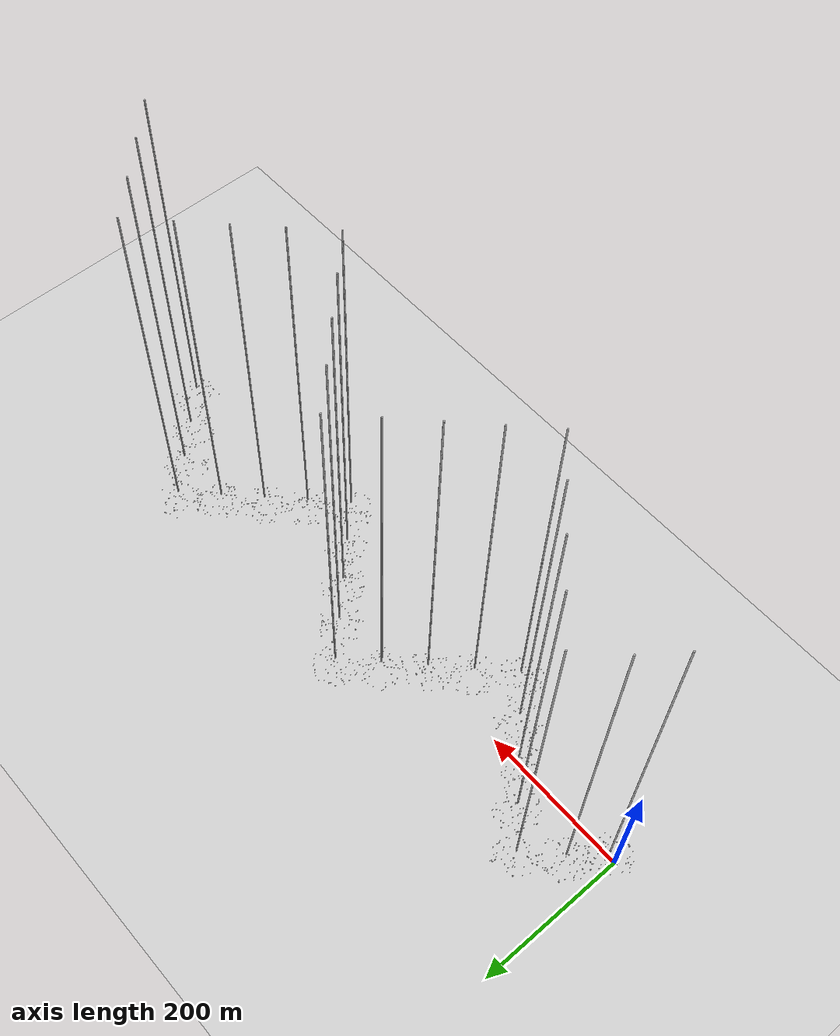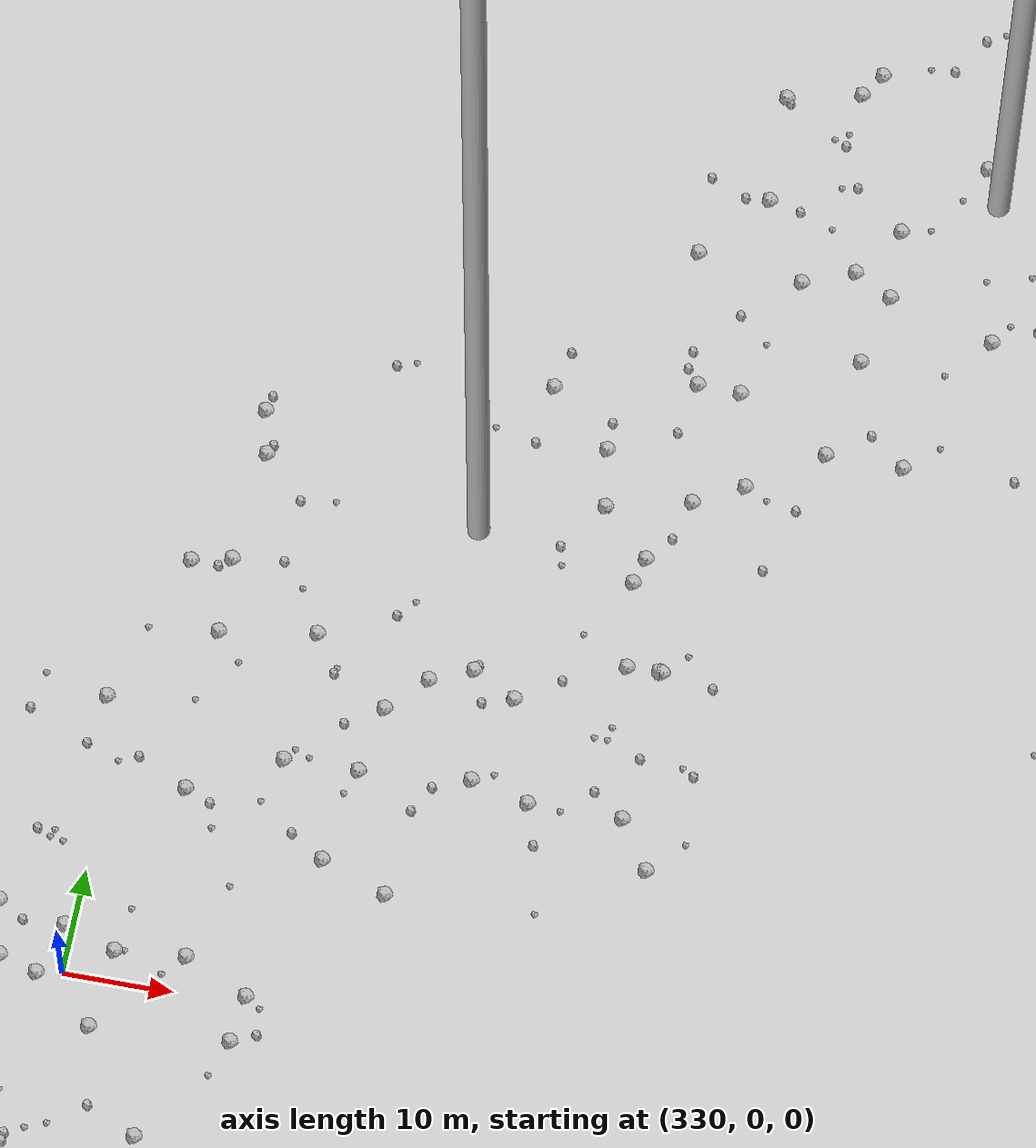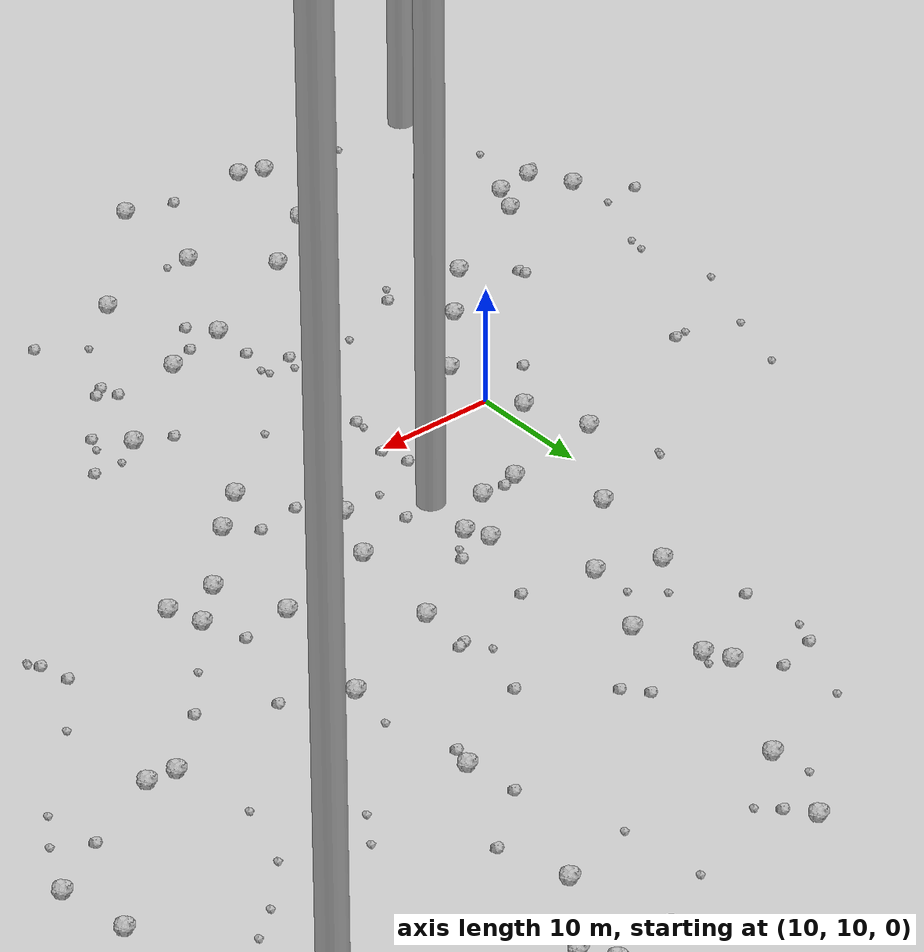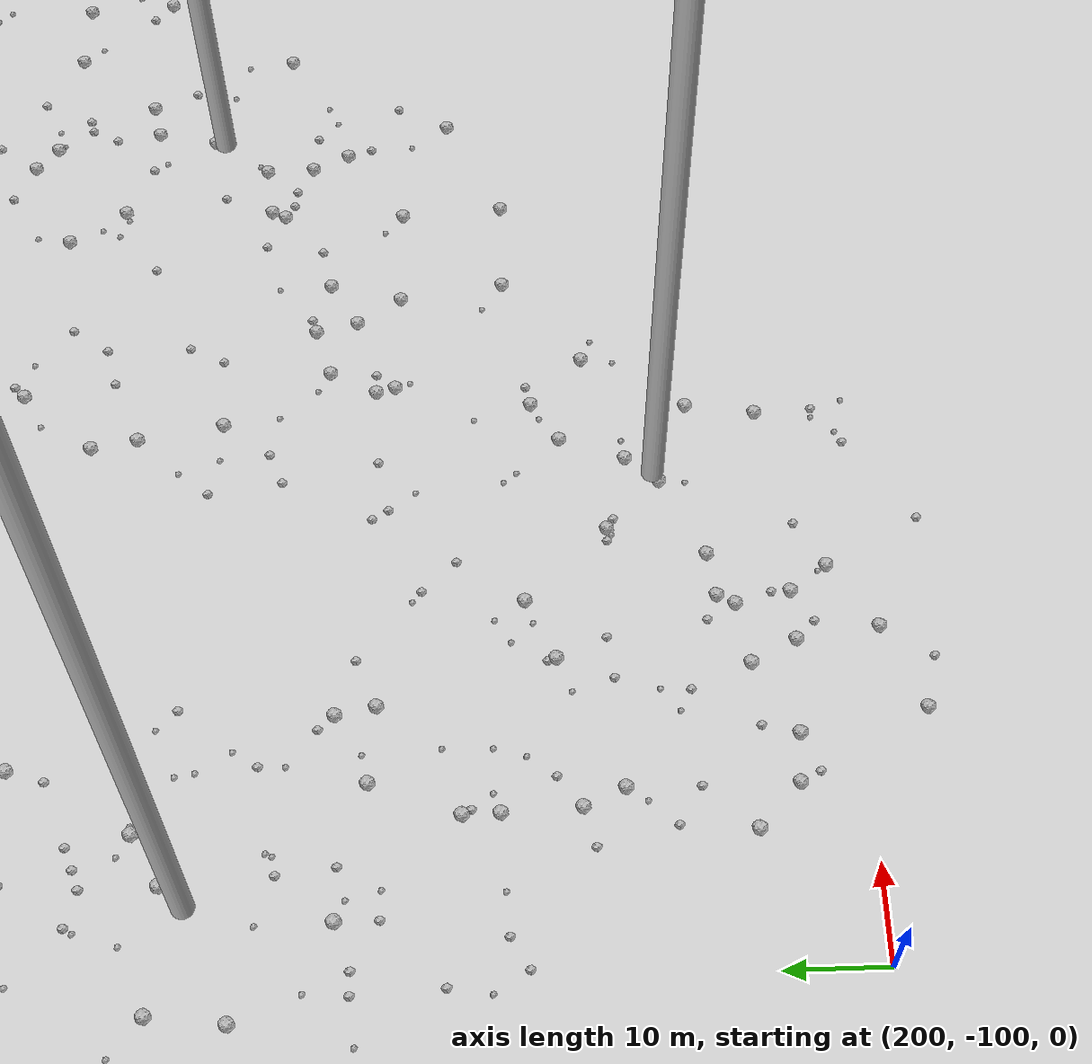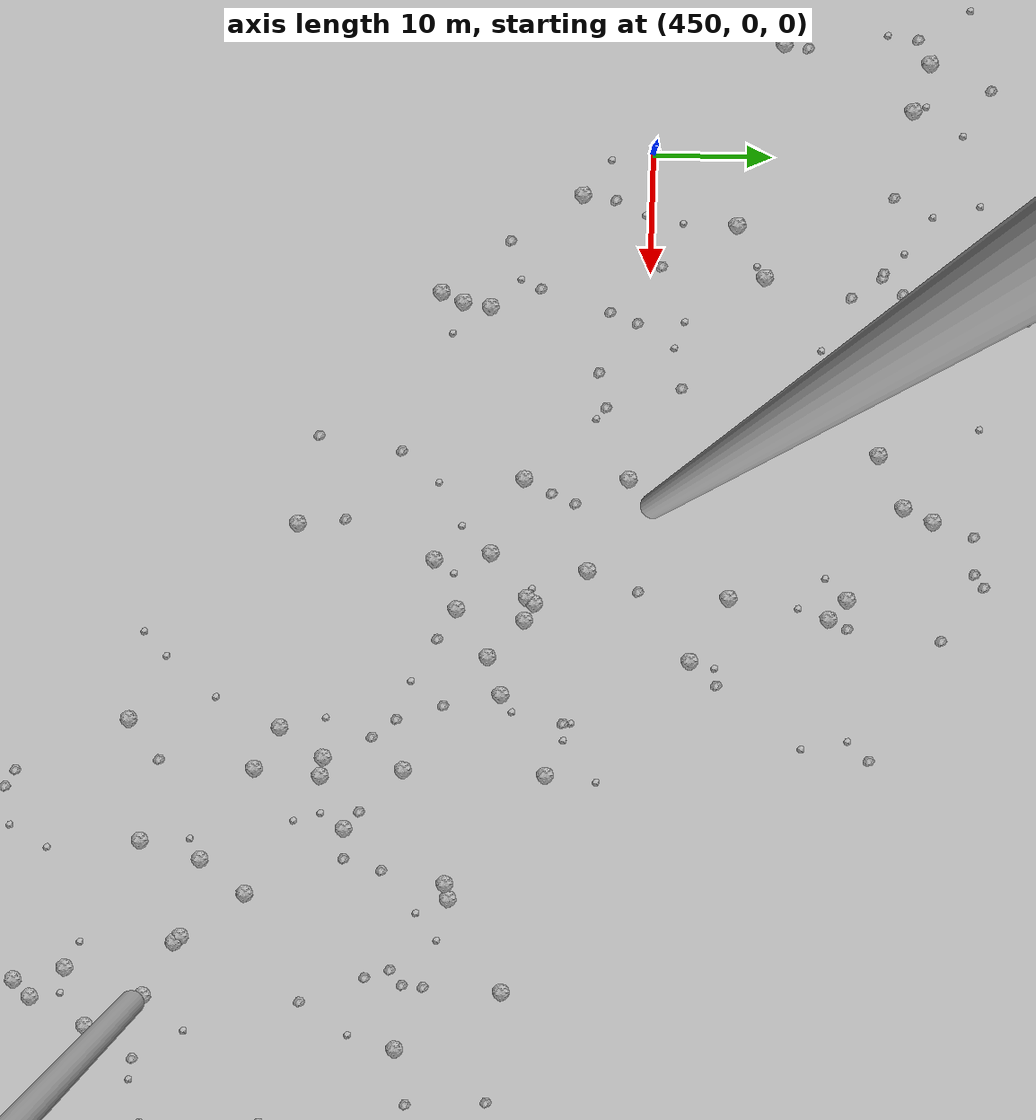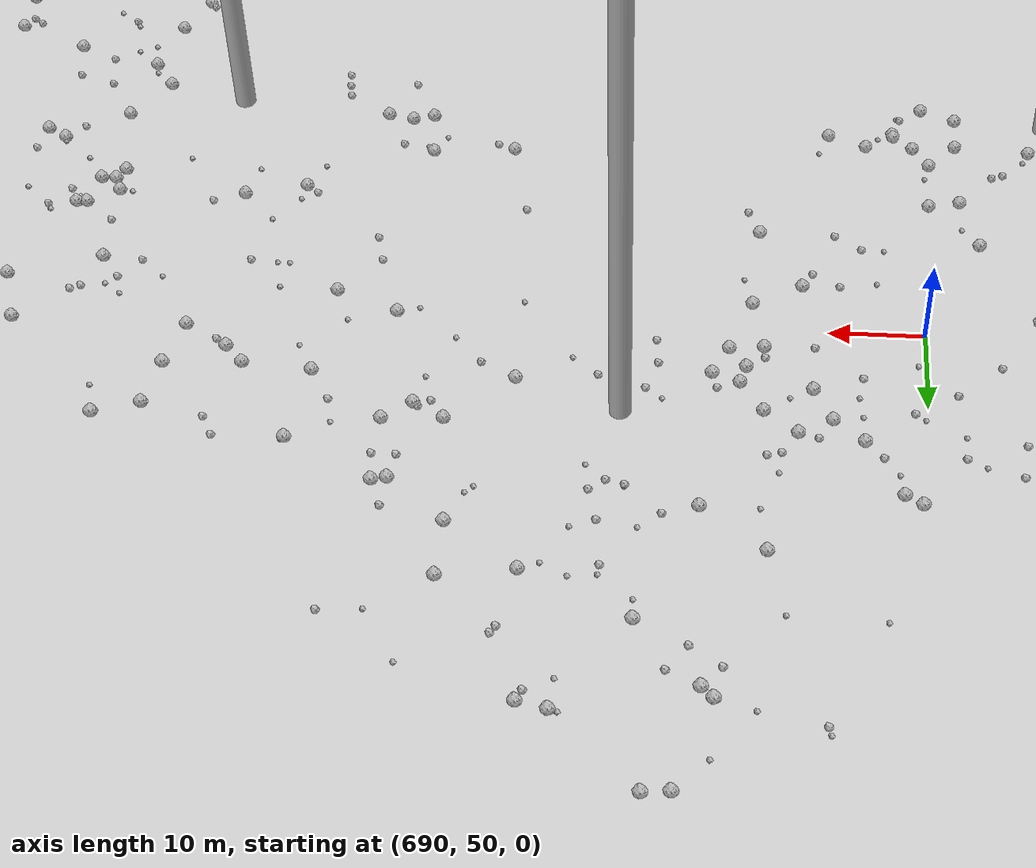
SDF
<sdf version="1.6">
 <world name="default">
  <include><uri>model://custom_ground</uri></include>
  <include><uri>model://sun</uri></include>
  <spherical_coordinates>
   <surface_model>EARTH_WGS84</surface_model>
   <latitude_deg>38.161479</latitude_deg>
   <longitude_deg>-122.454630</longitude_deg>
   <elevation>488.0</elevation>
   <heading_deg>90</heading_deg>
  </spherical_coordinates>
  <model name="rock1_0_0">
   <include><uri>model://rock1</uri><pose>9.564523827752975 5.094321014892564 0.5 0 0 0</pose></include>
  </model>
  <model name="rock1_0_1">
   <include><uri>model://rock1</uri><pose>15.490959533154047 -20.23040955230735 0.5 0 0 0</pose></include>
  </model>
  <model name="rock1_0_2">
   <include><uri>model://rock1</uri><pose>4.356708657687786 -0.6656469186276084 0.5 0 0 0</pose></include>
  </model>
  <model name="rock1_0_3">
   <include><uri>model://rock1</uri><pose>2.4416432252713136 -27.23035215243028 0.5 0 0 0</pose></include>
  </model>
  <model name="rock1_0_4">
   <include><uri>model://rock1</uri><pose>-15.521468803670103 -9.591491143482521 0.5 0 0 0</pose></include>
  </model>
  <model name="rock1_0_5">
   <include><uri>model://rock1</uri><pose>20.092193597775328 -10.289857489389838 0.5 0 0 0</pose></include>
  </model>
  <model name="rock1_0_6">
   <include><uri>model://rock1</uri><pose>12.252080185790994 26.04387670792694 0.5 0 0 0</pose></include>
  </model>
  <model name="rock1_0_7">
   <include><uri>model://rock1</uri><pose>24.492401627483737 -18.694061499063288 0.5 0 0 0</pose></include>
  </model>
  <model name="rock1_0_8">
   <include><uri>model://rock1</uri><pose>6.590274452478532 17.907130010985526 0.5 0 0 0</pose></include>
  </model>
  <model name="rock1_0_9">
   <include><uri>model://rock1</uri><pose>18.50009138023185 12.99983001199265 0.5 0 0 0</pose></include>
  </model>
  <model name="rock1_0_10">
   <include><uri>model://rock1</uri><pose>0.03575411385764937 -5.2928400045273065 0.5 0 0 0</pose></include>
  </model>
  <model name="rock1_0_11">
   <include><uri>model://rock1</uri><pose>25.65803336165512 -8.676368935320244 0.5 0 0 0</pose></include>
  </model>
  <model name="rock1_0_12">
   <include><uri>model://rock1</uri><pose>15.199730132528614 19.43091984248263 0.5 0 0 0</pose></include>
  </model>
  <model name="rock1_0_13">
   <include><uri>model://rock1</uri><pose>4.780271661619857 -19.682573709588105 0.5 0 0 0</pose></include>
  </model>
  <model name="rock1_0_14">
   <include><uri>model://rock1</uri><pose>4.436812157511788 -28.08354186326621 0.5 0 0 0</pose></include>
  </model>
  <model name="rock1_0_15">
   <include><uri>model://rock1</uri><pose>-9.123235903372196 -9.880937942871103 0.5 0 0 0</pose></include>
  </model>
  <model name="rock1_0_16">
   <include><uri>model://rock1</uri><pose>27.843062586336522 14.960507357459207 0.5 0 0 0</pose></include>
  </model>
  <model name="rock1_0_17">
   <include><uri>model://rock1</uri><pose>-13.6227602563211 -12.932042573311051 0.5 0 0 0</pose></include>
  </model>
  <model name="rock1_0_18">
   <include><uri>model://rock1</uri><pose>30.080850789474745 20.040743734302673 0.5 0 0 0</pose></include>
  </model>
  <model name="rock1_0_19">
   <include><uri>model://rock1</uri><pose>17.920314388842492 12.452141510641198 0.5 0 0 0</pose></include>
  </model>
  <model name="rock1_0_20">
   <include><uri>model://rock1</uri><pose>15.08325635554845 -29.08514662835005 0.5 0 0 0</pose></include>
  </model>
  <model name="rock1_0_21">
   <include><uri>model://rock1</uri><pose>34.20525443557368 -2.245063065328111 0.5 0 0 0</pose></include>
  </model>
  <model name="rock1_0_22">
   <include><uri>model://rock1</uri><pose>18.586211424495957 19.777590545055986 0.5 0 0 0</pose></include>
  </model>
  <model name="rock1_0_23">
   <include><uri>model://rock1</uri><pose>8.489145011078246 12.578778452297108 0.5 0 0 0</pose></include>
  </model>
  <model name="rock1_0_24">
   <include><uri>model://rock1</uri><pose>10.377300779304935 -15.250227414822293 0.5 0 0 0</pose></include>
  </model>
  <model name="rock1_0_25">
   <include><uri>model://rock1</uri><pose>-10.298240148979872 -12.466246657896274 0.5 0 0 0</pose></include>
  </model>
  <model name="rock1_0_26">
   <include><uri>model://rock1</uri><pose>32.55054588746187 8.031460850171783 0.5 0 0 0</pose></include>
  </model>
  <model name="rock2_0_0">
   <include><uri>model://rock2</uri><pose>-5.670123717028035 -15.208162148627482 0.3 0 0 0</pose></include>
  </model>
  <model name="rock2_0_1">
   <include><uri>model://rock2</uri><pose>33.774100410809034 12.82452802511716 0.3 0 0 0</pose></include>
  </model>
  <model name="rock2_0_2">
   <include><uri>model://rock2</uri><pose>7.0327504779760055 -5.492288063724914 0.3 0 0 0</pose></include>
  </model>
  <model name="rock2_0_3">
   <include><uri>model://rock2</uri><pose>32.57583246021899 -9.137186840203082 0.3 0 0 0</pose></include>
  </model>
  <model name="rock2_0_4">
   <include><uri>model://rock2</uri><pose>32.439377817399816 -17.36758208020455 0.3 0 0 0</pose></include>
  </model>
  <model name="rock2_0_5">
   <include><uri>model://rock2</uri><pose>-3.63606438444306 -2.2832894989374104 0.3 0 0 0</pose></include>
  </model>
  <model name="rock2_0_6">
   <include><uri>model://rock2</uri><pose>11.04294150322145 -27.94533671604318 0.3 0 0 0</pose></include>
  </model>
  <model name="rock2_0_7">
   <include><uri>model://rock2</uri><pose>-6.786107799804633 -18.528581062617146 0.3 0 0 0</pose></include>
  </model>
  <model name="rock2_0_8">
   <include><uri>model://rock2</uri><pose>31.176636167455733 -8.21785001183412 0.3 0 0 0</pose></include>
  </model>
  <model name="rock2_0_9">
   <include><uri>model://rock2</uri><pose>36.32656203523436 -4.604336345479169 0.3 0 0 0</pose></include>
  </model>
  <model name="rock2_0_10">
   <include><uri>model://rock2</uri><pose>-19.095588393752926 -5.951334157035404 0.3 0 0 0</pose></include>
  </model>
  <model name="rock2_0_11">
   <include><uri>model://rock2</uri><pose>-3.8015756186429215 -1.7083425023138972 0.3 0 0 0</pose></include>
  </model>
  <model name="rock2_0_12">
   <include><uri>model://rock2</uri><pose>19.923720314270206 12.774347953575699 0.3 0 0 0</pose></include>
  </model>
  <model name="rock2_0_13">
   <include><uri>model://rock2</uri><pose>20.178776177229082 -6.535020431985082 0.3 0 0 0</pose></include>
  </model>
  <model name="rock2_0_14">
   <include><uri>model://rock2</uri><pose>16.44440572101945 19.794909443157458 0.3 0 0 0</pose></include>
  </model>
  <model name="rock2_0_15">
   <include><uri>model://rock2</uri><pose>-6.747081953911371 12.83032918544938 0.3 0 0 0</pose></include>
  </model>
  <model name="rock2_0_16">
   <include><uri>model://rock2</uri><pose>23.179167259088743 -9.772708127897936 0.3 0 0 0</pose></include>
  </model>
  <model name="rock2_0_17">
   <include><uri>model://rock2</uri><pose>21.60915521346017 -12.42709274722769 0.3 0 0 0</pose></include>
  </model>
  <model name="rock2_0_18">
   <include><uri>model://rock2</uri><pose>31.296544119240984 -1.0030966770816505 0.3 0 0 0</pose></include>
  </model>
  <model name="rock2_0_19">
   <include><uri>model://rock2</uri><pose>19.5755766502228 6.209607871527311 0.3 0 0 0</pose></include>
  </model>
  <model name="rock2_0_20">
   <include><uri>model://rock2</uri><pose>20.58640650243678 10.508824009496827 0.3 0 0 0</pose></include>
  </model>
  <model name="rock2_0_21">
   <include><uri>model://rock2</uri><pose>38.84995485512147 -0.781922781855954 0.3 0 0 0</pose></include>
  </model>
  <model name="rock2_0_22">
   <include><uri>model://rock2</uri><pose>4.916366680805211 8.351901336654393 0.3 0 0 0</pose></include>
  </model>
  <model name="rock2_0_23">
   <include><uri>model://rock2</uri><pose>-14.537433039009187 -13.612017809277965 0.3 0 0 0</pose></include>
  </model>
  <model name="rock2_0_24">
   <include><uri>model://rock2</uri><pose>17.519349512136984 0.03979486302878499 0.3 0 0 0</pose></include>
  </model>
  <model name="rock2_0_25">
   <include><uri>model://rock2</uri><pose>31.685529896800936 -9.776096125247783 0.3 0 0 0</pose></include>
  </model>
  <model name="rock2_0_26">
   <include><uri>model://rock2</uri><pose>17.977082560410167 -4.006704637398055 0.3 0 0 0</pose></include>
  </model>
  <model name="rock3_0_0">
   <include><uri>model://rock3</uri><pose>-14.844104685150377 7.94571453450753 0.2 0 0 0</pose></include>
  </model>
  <model name="rock3_0_1">
   <include><uri>model://rock3</uri><pose>4.931877769137415 -17.393434936442773 0.2 0 0 0</pose></include>
  </model>
  <model name="rock3_0_2">
   <include><uri>model://rock3</uri><pose>-16.029605818827914 -5.759766027018255 0.2 0 0 0</pose></include>
  </model>
  <model name="rock3_0_3">
   <include><uri>model://rock3</uri><pose>10.907827281589146 -10.68788934718927 0.2 0 0 0</pose></include>
  </model>
  <model name="rock3_0_4">
   <include><uri>model://rock3</uri><pose>25.76418146279446 2.96666194920995 0.2 0 0 0</pose></include>
  </model>
  <model name="rock3_0_5">
   <include><uri>model://rock3</uri><pose>5.988683114100709 -6.953942090574319 0.2 0 0 0</pose></include>
  </model>
  <model name="rock3_0_6">
   <include><uri>model://rock3</uri><pose>28.18791134015573 13.21163745642157 0.2 0 0 0</pose></include>
  </model>
  <model name="rock3_0_7">
   <include><uri>model://rock3</uri><pose>12.770307739833754 -3.1176872664892024 0.2 0 0 0</pose></include>
  </model>
  <model name="rock3_0_8">
   <include><uri>model://rock3</uri><pose>-13.632435739043803 -0.15776264339557855 0.2 0 0 0</pose></include>
  </model>
  <model name="rock3_0_9">
   <include><uri>model://rock3</uri><pose>20.64617691449653 -4.103092210028912 0.2 0 0 0</pose></include>
  </model>
  <model name="rock3_0_10">
   <include><uri>model://rock3</uri><pose>36.290530482356424 -0.8333708867995853 0.2 0 0 0</pose></include>
  </model>
  <model name="rock3_0_11">
   <include><uri>model://rock3</uri><pose>-4.4547872817734735 -26.089414349318126 0.2 0 0 0</pose></include>
  </model>
  <model name="rock3_0_12">
   <include><uri>model://rock3</uri><pose>15.953223852765774 9.688173142192603 0.2 0 0 0</pose></include>
  </model>
  <model name="rock3_0_13">
   <include><uri>model://rock3</uri><pose>20.384292622141963 -3.374339708452794 0.2 0 0 0</pose></include>
  </model>
  <model name="rock3_0_14">
   <include><uri>model://rock3</uri><pose>19.523982894948936 7.023414765483636 0.2 0 0 0</pose></include>
  </model>
  <model name="rock3_0_15">
   <include><uri>model://rock3</uri><pose>18.44108705553922 -2.7477959199100113 0.2 0 0 0</pose></include>
  </model>
  <model name="rock3_0_16">
   <include><uri>model://rock3</uri><pose>-10.359408252904212 19.828017029001373 0.2 0 0 0</pose></include>
  </model>
  <model name="rock3_0_17">
   <include><uri>model://rock3</uri><pose>8.507824322157823 -13.501525246992905 0.2 0 0 0</pose></include>
  </model>
  <model name="rock3_0_18">
   <include><uri>model://rock3</uri><pose>4.629874957850177 23.664022873467353 0.2 0 0 0</pose></include>
  </model>
  <model name="rock3_0_19">
   <include><uri>model://rock3</uri><pose>4.795743182111856 24.021993901547496 0.2 0 0 0</pose></include>
  </model>
  <model name="rock3_0_20">
   <include><uri>model://rock3</uri><pose>17.275779993020357 -20.513037821982504 0.2 0 0 0</pose></include>
  </model>
  <model name="rock3_0_21">
   <include><uri>model://rock3</uri><pose>-7.9556521149591255 12.583776701590168 0.2 0 0 0</pose></include>
  </model>
  <model name="rock3_0_22">
   <include><uri>model://rock3</uri><pose>-12.14744039207093 14.354027900825521 0.2 0 0 0</pose></include>
  </model>
  <model name="rock3_0_23">
   <include><uri>model://rock3</uri><pose>-13.393826192477254 1.2758636927689508 0.2 0 0 0</pose></include>
  </model>
  <model name="rock3_0_24">
   <include><uri>model://rock3</uri><pose>29.00258074766976 -14.952381904590704 0.2 0 0 0</pose></include>
  </model>
  <model name="rock3_0_25">
   <include><uri>model://rock3</uri><pose>-12.929927623170709 -18.132432629977664 0.2 0 0 0</pose></include>
  </model>
  <model name="rock3_0_26">
   <include><uri>model://rock3</uri><pose>36.766314323224755 -3.3853361138820546 0.2 0 0 0</pose></include>
  </model>
  <model name="rock1_1_0">
   <include><uri>model://rock1</uri><pose>58.122309661683154 31.483989716523634 0.5 0 0 0</pose></include>
  </model>
  <model name="rock1_1_1">
   <include><uri>model://rock1</uri><pose>45.11376116389805 16.526388696186977 0.5 0 0 0</pose></include>
  </model>
  <model name="rock1_1_2">
   <include><uri>model://rock1</uri><pose>40.152754022551136 43.93035733290583 0.5 0 0 0</pose></include>
  </model>
  <model name="rock1_1_3">
   <include><uri>model://rock1</uri><pose>43.43660141496368 64.54290260581882 0.5 0 0 0</pose></include>
  </model>
  <model name="rock1_1_4">
   <include><uri>model://rock1</uri><pose>23.221430728663446 56.27123918247315 0.5 0 0 0</pose></include>
  </model>
  <model name="rock1_1_5">
   <include><uri>model://rock1</uri><pose>18.524718664866512 32.3401277514719 0.5 0 0 0</pose></include>
  </model>
  <model name="rock1_1_6">
   <include><uri>model://rock1</uri><pose>35.95282422568226 10.943334954169456 0.5 0 0 0</pose></include>
  </model>
  <model name="rock1_1_7">
   <include><uri>model://rock1</uri><pose>13.81945852836244 34.363812581756456 0.5 0 0 0</pose></include>
  </model>
  <model name="rock1_1_8">
   <include><uri>model://rock1</uri><pose>25.480952577386237 63.275901129931725 0.5 0 0 0</pose></include>
  </model>
  <model name="rock1_1_9">
   <include><uri>model://rock1</uri><pose>45.82381045547882 65.96416573309808 0.5 0 0 0</pose></include>
  </model>
  <model name="rock1_1_10">
   <include><uri>model://rock1</uri><pose>18.133124669894805 46.59370566304365 0.5 0 0 0</pose></include>
  </model>
  <model name="rock1_1_11">
   <include><uri>model://rock1</uri><pose>40.780744133490586 32.53133940908641 0.5 0 0 0</pose></include>
  </model>
  <model name="rock1_1_12">
   <include><uri>model://rock1</uri><pose>42.73500162362731 57.629066614618516 0.5 0 0 0</pose></include>
  </model>
  <model name="rock1_1_13">
   <include><uri>model://rock1</uri><pose>47.11976298791113 63.55962206915508 0.5 0 0 0</pose></include>
  </model>
  <model name="rock1_1_14">
   <include><uri>model://rock1</uri><pose>31.28215052766027 28.717446393497863 0.5 0 0 0</pose></include>
  </model>
  <model name="rock1_1_15">
   <include><uri>model://rock1</uri><pose>46.336865557892025 36.44618054757404 0.5 0 0 0</pose></include>
  </model>
  <model name="rock1_1_16">
   <include><uri>model://rock1</uri><pose>40.88173886401747 16.29795853284679 0.5 0 0 0</pose></include>
  </model>
  <model name="rock1_1_17">
   <include><uri>model://rock1</uri><pose>21.668399835943063 24.332889372448435 0.5 0 0 0</pose></include>
  </model>
  <model name="rock1_1_18">
   <include><uri>model://rock1</uri><pose>61.37066105067943 55.19102748142915 0.5 0 0 0</pose></include>
  </model>
  <model name="rock1_1_19">
   <include><uri>model://rock1</uri><pose>38.56679187474539 21.98315133422166 0.5 0 0 0</pose></include>
  </model>
  <model name="rock1_1_20">
   <include><uri>model://rock1</uri><pose>22.545228132178107 22.48842089518051 0.5 0 0 0</pose></include>
  </model>
  <model name="rock1_1_21">
   <include><uri>model://rock1</uri><pose>69.43822553704442 37.31385472529777 0.5 0 0 0</pose></include>
  </model>
  <model name="rock1_1_22">
   <include><uri>model://rock1</uri><pose>44.128346438126414 19.274699051851403 0.5 0 0 0</pose></include>
  </model>
  <model name="rock1_1_23">
   <include><uri>model://rock1</uri><pose>19.198105902909155 44.692852757671645 0.5 0 0 0</pose></include>
  </model>
  <model name="rock1_1_24">
   <include><uri>model://rock1</uri><pose>55.815400197842024 31.765030737654502 0.5 0 0 0</pose></include>
  </model>
  <model name="rock1_1_25">
   <include><uri>model://rock1</uri><pose>21.04568511900988 39.25728441532388 0.5 0 0 0</pose></include>
  </model>
  <model name="rock1_1_26">
   <include><uri>model://rock1</uri><pose>68.52623237317101 42.99104978108897 0.5 0 0 0</pose></include>
  </model>
  <model name="rock2_1_0">
   <include><uri>model://rock2</uri><pose>40.502596003799496 65.10927452300248 0.3 0 0 0</pose></include>
  </model>
  <model name="rock2_1_1">
   <include><uri>model://rock2</uri><pose>32.02535052650357 39.36551274525151 0.3 0 0 0</pose></include>
  </model>
  <model name="rock2_1_2">
   <include><uri>model://rock2</uri><pose>24.659000266186563 18.359987311197443 0.3 0 0 0</pose></include>
  </model>
  <model name="rock2_1_3">
   <include><uri>model://rock2</uri><pose>26.812551356354234 61.26522293622084 0.3 0 0 0</pose></include>
  </model>
  <model name="rock2_1_4">
   <include><uri>model://rock2</uri><pose>27.07168989082041 13.250419121299808 0.3 0 0 0</pose></include>
  </model>
  <model name="rock2_1_5">
   <include><uri>model://rock2</uri><pose>24.35505171163121 31.042178082517832 0.3 0 0 0</pose></include>
  </model>
  <model name="rock2_1_6">
   <include><uri>model://rock2</uri><pose>44.33171753811563 52.128772001926244 0.3 0 0 0</pose></include>
  </model>
  <model name="rock2_1_7">
   <include><uri>model://rock2</uri><pose>40.70652975079748 16.081049668402443 0.3 0 0 0</pose></include>
  </model>
  <model name="rock2_1_8">
   <include><uri>model://rock2</uri><pose>15.73307941072274 49.365793872534766 0.3 0 0 0</pose></include>
  </model>
  <model name="rock2_1_9">
   <include><uri>model://rock2</uri><pose>12.399400592810272 48.41418511111165 0.3 0 0 0</pose></include>
  </model>
  <model name="rock2_1_10">
   <include><uri>model://rock2</uri><pose>31.204099474813642 32.88153356979933 0.3 0 0 0</pose></include>
  </model>
  <model name="rock2_1_11">
   <include><uri>model://rock2</uri><pose>54.32818760896737 62.50628462551929 0.3 0 0 0</pose></include>
  </model>
  <model name="rock2_1_12">
   <include><uri>model://rock2</uri><pose>55.88753584553005 16.089108463016903 0.3 0 0 0</pose></include>
  </model>
  <model name="rock2_1_13">
   <include><uri>model://rock2</uri><pose>39.55348635877915 42.12970325633881 0.3 0 0 0</pose></include>
  </model>
  <model name="rock2_1_14">
   <include><uri>model://rock2</uri><pose>44.18142120272602 62.75775443048479 0.3 0 0 0</pose></include>
  </model>
  <model name="rock2_1_15">
   <include><uri>model://rock2</uri><pose>42.781637393468095 22.676536965703527 0.3 0 0 0</pose></include>
  </model>
  <model name="rock2_1_16">
   <include><uri>model://rock2</uri><pose>55.29003864392056 18.516777082189876 0.3 0 0 0</pose></include>
  </model>
  <model name="rock2_1_17">
   <include><uri>model://rock2</uri><pose>45.719861248293356 30.173745900763823 0.3 0 0 0</pose></include>
  </model>
  <model name="rock2_1_18">
   <include><uri>model://rock2</uri><pose>11.9687098834983 41.33038962776418 0.3 0 0 0</pose></include>
  </model>
  <model name="rock2_1_19">
   <include><uri>model://rock2</uri><pose>30.13618085613472 12.228835069552922 0.3 0 0 0</pose></include>
  </model>
  <model name="rock2_1_20">
   <include><uri>model://rock2</uri><pose>50.97241462393014 27.449141693918047 0.3 0 0 0</pose></include>
  </model>
  <model name="rock2_1_21">
   <include><uri>model://rock2</uri><pose>24.82785468798742 24.98881620288077 0.3 0 0 0</pose></include>
  </model>
  <model name="rock2_1_22">
   <include><uri>model://rock2</uri><pose>24.97081755342675 45.76200332236237 0.3 0 0 0</pose></include>
  </model>
  <model name="rock2_1_23">
   <include><uri>model://rock2</uri><pose>26.406093007126938 44.09976286523701 0.3 0 0 0</pose></include>
  </model>
  <model name="rock2_1_24">
   <include><uri>model://rock2</uri><pose>64.61370032213593 34.518459917633024 0.3 0 0 0</pose></include>
  </model>
  <model name="rock2_1_25">
   <include><uri>model://rock2</uri><pose>31.837747310436193 33.11976567573509 0.3 0 0 0</pose></include>
  </model>
  <model name="rock2_1_26">
   <include><uri>model://rock2</uri><pose>39.417270358110876 48.10215032439406 0.3 0 0 0</pose></include>
  </model>
  <model name="rock3_1_0">
   <include><uri>model://rock3</uri><pose>30.01967506739357 34.65798798125829 0.2 0 0 0</pose></include>
  </model>
  <model name="rock3_1_1">
   <include><uri>model://rock3</uri><pose>50.44889000711881 46.29982103042512 0.2 0 0 0</pose></include>
  </model>
  <model name="rock3_1_2">
   <include><uri>model://rock3</uri><pose>35.66273925525413 62.77948717776271 0.2 0 0 0</pose></include>
  </model>
  <model name="rock3_1_3">
   <include><uri>model://rock3</uri><pose>59.78957445926022 47.36582906719218 0.2 0 0 0</pose></include>
  </model>
  <model name="rock3_1_4">
   <include><uri>model://rock3</uri><pose>62.23741931140796 49.253574938360714 0.2 0 0 0</pose></include>
  </model>
  <model name="rock3_1_5">
   <include><uri>model://rock3</uri><pose>67.20367918952854 32.857713654665005 0.2 0 0 0</pose></include>
  </model>
  <model name="rock3_1_6">
   <include><uri>model://rock3</uri><pose>28.139821006715493 59.79590066177127 0.2 0 0 0</pose></include>
  </model>
  <model name="rock3_1_7">
   <include><uri>model://rock3</uri><pose>41.30263145051096 36.520654061849996 0.2 0 0 0</pose></include>
  </model>
  <model name="rock3_1_8">
   <include><uri>model://rock3</uri><pose>16.023797132083637 37.54493686422715 0.2 0 0 0</pose></include>
  </model>
  <model name="rock3_1_9">
   <include><uri>model://rock3</uri><pose>54.532016031434964 38.291274095836954 0.2 0 0 0</pose></include>
  </model>
  <model name="rock3_1_10">
   <include><uri>model://rock3</uri><pose>56.35542875051308 43.74478618226602 0.2 0 0 0</pose></include>
  </model>
  <model name="rock3_1_11">
   <include><uri>model://rock3</uri><pose>22.522380564077164 59.258643690003886 0.2 0 0 0</pose></include>
  </model>
  <model name="rock3_1_12">
   <include><uri>model://rock3</uri><pose>49.105523508868465 65.35680362593595 0.2 0 0 0</pose></include>
  </model>
  <model name="rock3_1_13">
   <include><uri>model://rock3</uri><pose>14.95448493973245 53.99854477559566 0.2 0 0 0</pose></include>
  </model>
  <model name="rock3_1_14">
   <include><uri>model://rock3</uri><pose>36.48744184984291 56.09134162914883 0.2 0 0 0</pose></include>
  </model>
  <model name="rock3_1_15">
   <include><uri>model://rock3</uri><pose>24.198968492452064 14.719425481788402 0.2 0 0 0</pose></include>
  </model>
  <model name="rock3_1_16">
   <include><uri>model://rock3</uri><pose>18.19270492269434 35.55123570800087 0.2 0 0 0</pose></include>
  </model>
  <model name="rock3_1_17">
   <include><uri>model://rock3</uri><pose>11.426700663084874 46.347537711998385 0.2 0 0 0</pose></include>
  </model>
  <model name="rock3_1_18">
   <include><uri>model://rock3</uri><pose>48.681078550664644 43.625118272969026 0.2 0 0 0</pose></include>
  </model>
  <model name="rock3_1_19">
   <include><uri>model://rock3</uri><pose>24.117009948984432 23.832481198517463 0.2 0 0 0</pose></include>
  </model>
  <model name="rock3_1_20">
   <include><uri>model://rock3</uri><pose>47.710051839476954 23.587211926911316 0.2 0 0 0</pose></include>
  </model>
  <model name="rock3_1_21">
   <include><uri>model://rock3</uri><pose>58.77152120203969 23.17258952063621 0.2 0 0 0</pose></include>
  </model>
  <model name="rock3_1_22">
   <include><uri>model://rock3</uri><pose>19.516069893957585 45.699763814188174 0.2 0 0 0</pose></include>
  </model>
  <model name="rock3_1_23">
   <include><uri>model://rock3</uri><pose>56.334832817018615 15.062202853525006 0.2 0 0 0</pose></include>
  </model>
  <model name="rock3_1_24">
   <include><uri>model://rock3</uri><pose>56.41725128971232 15.259098847385983 0.2 0 0 0</pose></include>
  </model>
  <model name="rock3_1_25">
   <include><uri>model://rock3</uri><pose>65.29700257346732 30.018851306809186 0.2 0 0 0</pose></include>
  </model>
  <model name="rock3_1_26">
   <include><uri>model://rock3</uri><pose>55.25027872016413 59.65258856399072 0.2 0 0 0</pose></include>
  </model>
  <model name="rock1_2_0">
   <include><uri>model://rock1</uri><pose>58.259329417190955 64.75630626480871 0.5 0 0 0</pose></include>
  </model>
  <model name="rock1_2_1">
   <include><uri>model://rock1</uri><pose>102.27968947483035 72.50883518804095 0.5 0 0 0</pose></include>
  </model>
  <model name="rock1_2_2">
   <include><uri>model://rock1</uri><pose>93.58500907996813 104.10661342481588 0.5 0 0 0</pose></include>
  </model>
  <model name="rock1_2_3">
   <include><uri>model://rock1</uri><pose>98.72332165881065 57.40494030756411 0.5 0 0 0</pose></include>
  </model>
  <model name="rock1_2_4">
   <include><uri>model://rock1</uri><pose>103.87008050899696 92.12898011447933 0.5 0 0 0</pose></include>
  </model>
  <model name="rock1_2_5">
   <include><uri>model://rock1</uri><pose>63.273233521537406 58.61623435481107 0.5 0 0 0</pose></include>
  </model>
  <model name="rock1_2_6">
   <include><uri>model://rock1</uri><pose>91.77431025438673 100.00434796475969 0.5 0 0 0</pose></include>
  </model>
  <model name="rock1_2_7">
   <include><uri>model://rock1</uri><pose>91.83567385564805 104.08286751624968 0.5 0 0 0</pose></include>
  </model>
  <model name="rock1_2_8">
   <include><uri>model://rock1</uri><pose>72.67152001306182 65.14184624971384 0.5 0 0 0</pose></include>
  </model>
  <model name="rock1_2_9">
   <include><uri>model://rock1</uri><pose>94.04168890274866 85.54509857091233 0.5 0 0 0</pose></include>
  </model>
  <model name="rock1_2_10">
   <include><uri>model://rock1</uri><pose>70.01636416498083 69.74405188811043 0.5 0 0 0</pose></include>
  </model>
  <model name="rock1_2_11">
   <include><uri>model://rock1</uri><pose>103.47037816876963 82.84151994328616 0.5 0 0 0</pose></include>
  </model>
  <model name="rock1_2_12">
   <include><uri>model://rock1</uri><pose>72.49718577743576 91.3844916344209 0.5 0 0 0</pose></include>
  </model>
  <model name="rock1_2_13">
   <include><uri>model://rock1</uri><pose>74.83398556649637 95.63208420578728 0.5 0 0 0</pose></include>
  </model>
  <model name="rock1_2_14">
   <include><uri>model://rock1</uri><pose>83.23226798868384 75.11823404536737 0.5 0 0 0</pose></include>
  </model>
  <model name="rock1_2_15">
   <include><uri>model://rock1</uri><pose>88.20218935681521 67.90724595020892 0.5 0 0 0</pose></include>
  </model>
  <model name="rock1_2_16">
   <include><uri>model://rock1</uri><pose>103.79286497517418 85.72587606974665 0.5 0 0 0</pose></include>
  </model>
  <model name="rock1_2_17">
   <include><uri>model://rock1</uri><pose>79.59562149784985 82.80216495759204 0.5 0 0 0</pose></include>
  </model>
  <model name="rock1_2_18">
   <include><uri>model://rock1</uri><pose>55.9312396677203 68.24536984537895 0.5 0 0 0</pose></include>
  </model>
  <model name="rock1_2_19">
   <include><uri>model://rock1</uri><pose>84.58254051351466 60.695627213644414 0.5 0 0 0</pose></include>
  </model>
  <model name="rock1_2_20">
   <include><uri>model://rock1</uri><pose>93.21429126785105 97.04456748375993 0.5 0 0 0</pose></include>
  </model>
  <model name="rock1_2_21">
   <include><uri>model://rock1</uri><pose>64.50013744055578 61.368560175181344 0.5 0 0 0</pose></include>
  </model>
  <model name="rock1_2_22">
   <include><uri>model://rock1</uri><pose>60.65236288761234 71.18480089304337 0.5 0 0 0</pose></include>
  </model>
  <model name="rock1_2_23">
   <include><uri>model://rock1</uri><pose>95.9211684080096 82.42766776165892 0.5 0 0 0</pose></include>
  </model>
  <model name="rock1_2_24">
   <include><uri>model://rock1</uri><pose>78.9029968371896 83.33989714212896 0.5 0 0 0</pose></include>
  </model>
  <model name="rock1_2_25">
   <include><uri>model://rock1</uri><pose>64.43507876839709 98.14734150879373 0.5 0 0 0</pose></include>
  </model>
  <model name="rock1_2_26">
   <include><uri>model://rock1</uri><pose>80.50222235024438 96.08856062412113 0.5 0 0 0</pose></include>
  </model>
  <model name="rock2_2_0">
   <include><uri>model://rock2</uri><pose>99.22871590723929 100.66205794299036 0.3 0 0 0</pose></include>
  </model>
  <model name="rock2_2_1">
   <include><uri>model://rock2</uri><pose>99.36683488931129 70.70119819900846 0.3 0 0 0</pose></include>
  </model>
  <model name="rock2_2_2">
   <include><uri>model://rock2</uri><pose>73.30892523336011 64.69978414666849 0.3 0 0 0</pose></include>
  </model>
  <model name="rock2_2_3">
   <include><uri>model://rock2</uri><pose>91.32509126742025 76.95507039677146 0.3 0 0 0</pose></include>
  </model>
  <model name="rock2_2_4">
   <include><uri>model://rock2</uri><pose>85.84641853718796 62.31824060824586 0.3 0 0 0</pose></include>
  </model>
  <model name="rock2_2_5">
   <include><uri>model://rock2</uri><pose>95.8639327672223 92.96933966720522 0.3 0 0 0</pose></include>
  </model>
  <model name="rock2_2_6">
   <include><uri>model://rock2</uri><pose>63.408288164080574 81.20461981158977 0.3 0 0 0</pose></include>
  </model>
  <model name="rock2_2_7">
   <include><uri>model://rock2</uri><pose>94.9640558702664 80.18905968147874 0.3 0 0 0</pose></include>
  </model>
  <model name="rock2_2_8">
   <include><uri>model://rock2</uri><pose>85.73582466474932 108.47321835541308 0.3 0 0 0</pose></include>
  </model>
  <model name="rock2_2_9">
   <include><uri>model://rock2</uri><pose>64.81599729027 68.90936270849821 0.3 0 0 0</pose></include>
  </model>
  <model name="rock2_2_10">
   <include><uri>model://rock2</uri><pose>73.38944418011883 89.49665871666053 0.3 0 0 0</pose></include>
  </model>
  <model name="rock2_2_11">
   <include><uri>model://rock2</uri><pose>96.81199221832458 97.51362448472979 0.3 0 0 0</pose></include>
  </model>
  <model name="rock2_2_12">
   <include><uri>model://rock2</uri><pose>97.5155105131779 61.608360850912405 0.3 0 0 0</pose></include>
  </model>
  <model name="rock2_2_13">
   <include><uri>model://rock2</uri><pose>104.7196932396585 80.75251413243515 0.3 0 0 0</pose></include>
  </model>
  <model name="rock2_2_14">
   <include><uri>model://rock2</uri><pose>94.69410842337646 105.67286570594347 0.3 0 0 0</pose></include>
  </model>
  <model name="rock2_2_15">
   <include><uri>model://rock2</uri><pose>79.38495142242937 82.56615300121962 0.3 0 0 0</pose></include>
  </model>
  <model name="rock2_2_16">
   <include><uri>model://rock2</uri><pose>105.17270125179866 74.64997004672418 0.3 0 0 0</pose></include>
  </model>
  <model name="rock2_2_17">
   <include><uri>model://rock2</uri><pose>91.81444760544056 101.3559040939779 0.3 0 0 0</pose></include>
  </model>
  <model name="rock2_2_18">
   <include><uri>model://rock2</uri><pose>87.65911763341256 94.26758583730242 0.3 0 0 0</pose></include>
  </model>
  <model name="rock2_2_19">
   <include><uri>model://rock2</uri><pose>70.71266954808598 88.88630241951444 0.3 0 0 0</pose></include>
  </model>
  <model name="rock2_2_20">
   <include><uri>model://rock2</uri><pose>87.32521767272277 84.85962070195973 0.3 0 0 0</pose></include>
  </model>
  <model name="rock2_2_21">
   <include><uri>model://rock2</uri><pose>78.50837330644902 58.87017347022932 0.3 0 0 0</pose></include>
  </model>
  <model name="rock2_2_22">
   <include><uri>model://rock2</uri><pose>53.744707113709346 81.1508587114681 0.3 0 0 0</pose></include>
  </model>
  <model name="rock2_2_23">
   <include><uri>model://rock2</uri><pose>54.85426315314121 80.49314373293149 0.3 0 0 0</pose></include>
  </model>
  <model name="rock2_2_24">
   <include><uri>model://rock2</uri><pose>84.8264727266322 87.50527870983434 0.3 0 0 0</pose></include>
  </model>
  <model name="rock2_2_25">
   <include><uri>model://rock2</uri><pose>91.91519154942728 60.21136554232745 0.3 0 0 0</pose></include>
  </model>
  <model name="rock2_2_26">
   <include><uri>model://rock2</uri><pose>79.09235932352175 87.60368774507978 0.3 0 0 0</pose></include>
  </model>
  <model name="rock3_2_0">
   <include><uri>model://rock3</uri><pose>62.44528697911221 92.94816276685009 0.2 0 0 0</pose></include>
  </model>
  <model name="rock3_2_1">
   <include><uri>model://rock3</uri><pose>101.27459173891799 86.36327659482711 0.2 0 0 0</pose></include>
  </model>
  <model name="rock3_2_2">
   <include><uri>model://rock3</uri><pose>65.92534095613728 94.18549593804671 0.2 0 0 0</pose></include>
  </model>
  <model name="rock3_2_3">
   <include><uri>model://rock3</uri><pose>87.65969392706165 59.38049668982414 0.2 0 0 0</pose></include>
  </model>
  <model name="rock3_2_4">
   <include><uri>model://rock3</uri><pose>99.22193128211273 72.41380940746203 0.2 0 0 0</pose></include>
  </model>
  <model name="rock3_2_5">
   <include><uri>model://rock3</uri><pose>78.66286432746986 63.20433569190616 0.2 0 0 0</pose></include>
  </model>
  <model name="rock3_2_6">
   <include><uri>model://rock3</uri><pose>72.42560534523089 99.49483841434528 0.2 0 0 0</pose></include>
  </model>
  <model name="rock3_2_7">
   <include><uri>model://rock3</uri><pose>80.48054967333368 106.18922389518318 0.2 0 0 0</pose></include>
  </model>
  <model name="rock3_2_8">
   <include><uri>model://rock3</uri><pose>68.50847668172258 69.51196518746625 0.2 0 0 0</pose></include>
  </model>
  <model name="rock3_2_9">
   <include><uri>model://rock3</uri><pose>87.04667565740954 91.87014756925271 0.2 0 0 0</pose></include>
  </model>
  <model name="rock3_2_10">
   <include><uri>model://rock3</uri><pose>94.85234656882888 54.29204734880872 0.2 0 0 0</pose></include>
  </model>
  <model name="rock3_2_11">
   <include><uri>model://rock3</uri><pose>74.79242551352888 85.25994268608622 0.2 0 0 0</pose></include>
  </model>
  <model name="rock3_2_12">
   <include><uri>model://rock3</uri><pose>60.10045189706824 70.76447320535124 0.2 0 0 0</pose></include>
  </model>
  <model name="rock3_2_13">
   <include><uri>model://rock3</uri><pose>57.56627863954546 89.18306011685482 0.2 0 0 0</pose></include>
  </model>
  <model name="rock3_2_14">
   <include><uri>model://rock3</uri><pose>59.82698454492237 99.00322378105207 0.2 0 0 0</pose></include>
  </model>
  <model name="rock3_2_15">
   <include><uri>model://rock3</uri><pose>78.91461269125523 86.72904909053574 0.2 0 0 0</pose></include>
  </model>
  <model name="rock3_2_16">
   <include><uri>model://rock3</uri><pose>89.3398727055509 99.94984602769718 0.2 0 0 0</pose></include>
  </model>
  <model name="rock3_2_17">
   <include><uri>model://rock3</uri><pose>63.93867748203146 70.30381070594174 0.2 0 0 0</pose></include>
  </model>
  <model name="rock3_2_18">
   <include><uri>model://rock3</uri><pose>106.93651921258329 68.39432372214634 0.2 0 0 0</pose></include>
  </model>
  <model name="rock3_2_19">
   <include><uri>model://rock3</uri><pose>79.3468487255403 106.67321512323255 0.2 0 0 0</pose></include>
  </model>
  <model name="rock3_2_20">
   <include><uri>model://rock3</uri><pose>82.71605678225983 69.52094924500719 0.2 0 0 0</pose></include>
  </model>
  <model name="rock3_2_21">
   <include><uri>model://rock3</uri><pose>81.27836667020975 64.08381184083139 0.2 0 0 0</pose></include>
  </model>
  <model name="rock3_2_22">
   <include><uri>model://rock3</uri><pose>71.30217974376578 56.88900699557973 0.2 0 0 0</pose></include>
  </model>
  <model name="rock3_2_23">
   <include><uri>model://rock3</uri><pose>93.40561887430823 100.74538354290411 0.2 0 0 0</pose></include>
  </model>
  <model name="rock3_2_24">
   <include><uri>model://rock3</uri><pose>58.41495882200777 84.12514084870593 0.2 0 0 0</pose></include>
  </model>
  <model name="rock3_2_25">
   <include><uri>model://rock3</uri><pose>70.67173151259078 96.86623416017665 0.2 0 0 0</pose></include>
  </model>
  <model name="rock3_2_26">
   <include><uri>model://rock3</uri><pose>83.98829831142383 90.6264705429202 0.2 0 0 0</pose></include>
  </model>
  <model name="rock1_3_0">
   <include><uri>model://rock1</uri><pose>126.2675268022956 35.21802372217651 0.5 0 0 0</pose></include>
  </model>
  <model name="rock1_3_1">
   <include><uri>model://rock1</uri><pose>114.88834508162812 68.9848353517054 0.5 0 0 0</pose></include>
  </model>
  <model name="rock1_3_2">
   <include><uri>model://rock1</uri><pose>99.24729550023586 59.198711119660565 0.5 0 0 0</pose></include>
  </model>
  <model name="rock1_3_3">
   <include><uri>model://rock1</uri><pose>137.19020129943755 38.62957553875221 0.5 0 0 0</pose></include>
  </model>
  <model name="rock1_3_4">
   <include><uri>model://rock1</uri><pose>137.48569800790764 61.01694435491188 0.5 0 0 0</pose></include>
  </model>
  <model name="rock1_3_5">
   <include><uri>model://rock1</uri><pose>134.3893489661683 43.32489410723125 0.5 0 0 0</pose></include>
  </model>
  <model name="rock1_3_6">
   <include><uri>model://rock1</uri><pose>111.12948538367866 60.750692498636276 0.5 0 0 0</pose></include>
  </model>
  <model name="rock1_3_7">
   <include><uri>model://rock1</uri><pose>115.1999360649684 32.9642379133082 0.5 0 0 0</pose></include>
  </model>
  <model name="rock1_3_8">
   <include><uri>model://rock1</uri><pose>125.20941915656056 36.41517850360906 0.5 0 0 0</pose></include>
  </model>
  <model name="rock1_3_9">
   <include><uri>model://rock1</uri><pose>134.61779858913718 57.90448998145436 0.5 0 0 0</pose></include>
  </model>
  <model name="rock1_3_10">
   <include><uri>model://rock1</uri><pose>108.89384565392754 14.366581490994594 0.5 0 0 0</pose></include>
  </model>
  <model name="rock1_3_11">
   <include><uri>model://rock1</uri><pose>130.30856457304031 66.47454163658918 0.5 0 0 0</pose></include>
  </model>
  <model name="rock1_3_12">
   <include><uri>model://rock1</uri><pose>119.82594470991361 11.388805167824481 0.5 0 0 0</pose></include>
  </model>
  <model name="rock1_3_13">
   <include><uri>model://rock1</uri><pose>111.51466274720617 11.664458507091117 0.5 0 0 0</pose></include>
  </model>
  <model name="rock1_3_14">
   <include><uri>model://rock1</uri><pose>125.58541090061284 42.6237423033047 0.5 0 0 0</pose></include>
  </model>
  <model name="rock1_3_15">
   <include><uri>model://rock1</uri><pose>133.8353283639135 29.856138214708736 0.5 0 0 0</pose></include>
  </model>
  <model name="rock1_3_16">
   <include><uri>model://rock1</uri><pose>112.3541450462498 39.58833612925955 0.5 0 0 0</pose></include>
  </model>
  <model name="rock1_3_17">
   <include><uri>model://rock1</uri><pose>108.85169005259341 18.57854227767879 0.5 0 0 0</pose></include>
  </model>
  <model name="rock1_3_18">
   <include><uri>model://rock1</uri><pose>113.06041443347728 44.1414229050503 0.5 0 0 0</pose></include>
  </model>
  <model name="rock1_3_19">
   <include><uri>model://rock1</uri><pose>121.60234581289234 63.52058191747954 0.5 0 0 0</pose></include>
  </model>
  <model name="rock1_3_20">
   <include><uri>model://rock1</uri><pose>91.05450261678583 34.464778802173676 0.5 0 0 0</pose></include>
  </model>
  <model name="rock1_3_21">
   <include><uri>model://rock1</uri><pose>120.44611424258856 19.424545135588183 0.5 0 0 0</pose></include>
  </model>
  <model name="rock1_3_22">
   <include><uri>model://rock1</uri><pose>115.2705590074245 50.1415760321456 0.5 0 0 0</pose></include>
  </model>
  <model name="rock1_3_23">
   <include><uri>model://rock1</uri><pose>117.32037225141264 62.83944544920057 0.5 0 0 0</pose></include>
  </model>
  <model name="rock1_3_24">
   <include><uri>model://rock1</uri><pose>137.79649791692688 37.99041810565495 0.5 0 0 0</pose></include>
  </model>
  <model name="rock1_3_25">
   <include><uri>model://rock1</uri><pose>121.38873648041596 12.975525506450401 0.5 0 0 0</pose></include>
  </model>
  <model name="rock1_3_26">
   <include><uri>model://rock1</uri><pose>132.63678897519625 40.312229528542616 0.5 0 0 0</pose></include>
  </model>
  <model name="rock2_3_0">
   <include><uri>model://rock2</uri><pose>129.21045115078581 13.89531904718038 0.3 0 0 0</pose></include>
  </model>
  <model name="rock2_3_1">
   <include><uri>model://rock2</uri><pose>106.59904690441891 34.80090353686133 0.3 0 0 0</pose></include>
  </model>
  <model name="rock2_3_2">
   <include><uri>model://rock2</uri><pose>119.40608614329503 11.533996149206427 0.3 0 0 0</pose></include>
  </model>
  <model name="rock2_3_3">
   <include><uri>model://rock2</uri><pose>117.86750277552665 62.29643555824197 0.3 0 0 0</pose></include>
  </model>
  <model name="rock2_3_4">
   <include><uri>model://rock2</uri><pose>129.15389848978984 58.01858917189133 0.3 0 0 0</pose></include>
  </model>
  <model name="rock2_3_5">
   <include><uri>model://rock2</uri><pose>135.2723151449056 56.216038978263626 0.3 0 0 0</pose></include>
  </model>
  <model name="rock2_3_6">
   <include><uri>model://rock2</uri><pose>113.6690875158011 41.06304100106607 0.3 0 0 0</pose></include>
  </model>
  <model name="rock2_3_7">
   <include><uri>model://rock2</uri><pose>99.07946313626 19.750989073037722 0.3 0 0 0</pose></include>
  </model>
  <model name="rock2_3_8">
   <include><uri>model://rock2</uri><pose>140.39709396904482 53.40450721999805 0.3 0 0 0</pose></include>
  </model>
  <model name="rock2_3_9">
   <include><uri>model://rock2</uri><pose>144.5341027239135 24.800267739297322 0.3 0 0 0</pose></include>
  </model>
  <model name="rock2_3_10">
   <include><uri>model://rock2</uri><pose>123.36436434838313 11.36399196215933 0.3 0 0 0</pose></include>
  </model>
  <model name="rock2_3_11">
   <include><uri>model://rock2</uri><pose>131.29346210255324 55.05018746003907 0.3 0 0 0</pose></include>
  </model>
  <model name="rock2_3_12">
   <include><uri>model://rock2</uri><pose>110.73505662572329 55.04342721582588 0.3 0 0 0</pose></include>
  </model>
  <model name="rock2_3_13">
   <include><uri>model://rock2</uri><pose>98.3057988333548 29.522022343790585 0.3 0 0 0</pose></include>
  </model>
  <model name="rock2_3_14">
   <include><uri>model://rock2</uri><pose>103.31194939666949 17.974706193554084 0.3 0 0 0</pose></include>
  </model>
  <model name="rock2_3_15">
   <include><uri>model://rock2</uri><pose>107.92610834989152 16.533364154594658 0.3 0 0 0</pose></include>
  </model>
  <model name="rock2_3_16">
   <include><uri>model://rock2</uri><pose>143.3191609470776 33.774862769262064 0.3 0 0 0</pose></include>
  </model>
  <model name="rock2_3_17">
   <include><uri>model://rock2</uri><pose>117.56874727660457 36.27666653919074 0.3 0 0 0</pose></include>
  </model>
  <model name="rock2_3_18">
   <include><uri>model://rock2</uri><pose>117.90711612088518 43.63384720887596 0.3 0 0 0</pose></include>
  </model>
  <model name="rock2_3_19">
   <include><uri>model://rock2</uri><pose>93.64699592911937 39.89024329416877 0.3 0 0 0</pose></include>
  </model>
  <model name="rock2_3_20">
   <include><uri>model://rock2</uri><pose>98.24300829685495 25.691894637033712 0.3 0 0 0</pose></include>
  </model>
  <model name="rock2_3_21">
   <include><uri>model://rock2</uri><pose>101.94661093130203 42.61439846685881 0.3 0 0 0</pose></include>
  </model>
  <model name="rock2_3_22">
   <include><uri>model://rock2</uri><pose>102.95963810309254 58.34889139986706 0.3 0 0 0</pose></include>
  </model>
  <model name="rock2_3_23">
   <include><uri>model://rock2</uri><pose>127.13766967166428 21.38050880129269 0.3 0 0 0</pose></include>
  </model>
  <model name="rock2_3_24">
   <include><uri>model://rock2</uri><pose>105.81776005431244 50.11784952565729 0.3 0 0 0</pose></include>
  </model>
  <model name="rock2_3_25">
   <include><uri>model://rock2</uri><pose>140.2946484238237 48.79562932029895 0.3 0 0 0</pose></include>
  </model>
  <model name="rock2_3_26">
   <include><uri>model://rock2</uri><pose>126.29574566867026 55.61164677450998 0.3 0 0 0</pose></include>
  </model>
  <model name="rock3_3_0">
   <include><uri>model://rock3</uri><pose>92.04345798036944 36.45596866757532 0.2 0 0 0</pose></include>
  </model>
  <model name="rock3_3_1">
   <include><uri>model://rock3</uri><pose>147.91056715202308 32.39759375130498 0.2 0 0 0</pose></include>
  </model>
  <model name="rock3_3_2">
   <include><uri>model://rock3</uri><pose>109.99035096088986 13.145204876309505 0.2 0 0 0</pose></include>
  </model>
  <model name="rock3_3_3">
   <include><uri>model://rock3</uri><pose>109.05167970945365 49.7537923493742 0.2 0 0 0</pose></include>
  </model>
  <model name="rock3_3_4">
   <include><uri>model://rock3</uri><pose>122.75496695806723 45.02836034371125 0.2 0 0 0</pose></include>
  </model>
  <model name="rock3_3_5">
   <include><uri>model://rock3</uri><pose>105.33168678432752 35.070530177317124 0.2 0 0 0</pose></include>
  </model>
  <model name="rock3_3_6">
   <include><uri>model://rock3</uri><pose>136.99282307467422 61.98410161522094 0.2 0 0 0</pose></include>
  </model>
  <model name="rock3_3_7">
   <include><uri>model://rock3</uri><pose>106.82195820072778 18.65868633834971 0.2 0 0 0</pose></include>
  </model>
  <model name="rock3_3_8">
   <include><uri>model://rock3</uri><pose>97.35032176318049 48.80040265412268 0.2 0 0 0</pose></include>
  </model>
  <model name="rock3_3_9">
   <include><uri>model://rock3</uri><pose>136.20244056790239 22.210244873679994 0.2 0 0 0</pose></include>
  </model>
  <model name="rock3_3_10">
   <include><uri>model://rock3</uri><pose>111.34936992608677 39.79631722942829 0.2 0 0 0</pose></include>
  </model>
  <model name="rock3_3_11">
   <include><uri>model://rock3</uri><pose>140.43016684895758 35.165487926707314 0.2 0 0 0</pose></include>
  </model>
  <model name="rock3_3_12">
   <include><uri>model://rock3</uri><pose>107.96558332892724 66.56294036250978 0.2 0 0 0</pose></include>
  </model>
  <model name="rock3_3_13">
   <include><uri>model://rock3</uri><pose>125.07683068315251 26.796626795037614 0.2 0 0 0</pose></include>
  </model>
  <model name="rock3_3_14">
   <include><uri>model://rock3</uri><pose>135.15915613564385 45.614190794366536 0.2 0 0 0</pose></include>
  </model>
  <model name="rock3_3_15">
   <include><uri>model://rock3</uri><pose>96.1006806424642 55.59482636705777 0.2 0 0 0</pose></include>
  </model>
  <model name="rock3_3_16">
   <include><uri>model://rock3</uri><pose>134.7808246782559 23.88695209988895 0.2 0 0 0</pose></include>
  </model>
  <model name="rock3_3_17">
   <include><uri>model://rock3</uri><pose>102.587542635852 26.811224947197342 0.2 0 0 0</pose></include>
  </model>
  <model name="rock3_3_18">
   <include><uri>model://rock3</uri><pose>120.02685981308377 20.5519632253673 0.2 0 0 0</pose></include>
  </model>
  <model name="rock3_3_19">
   <include><uri>model://rock3</uri><pose>122.47938477724145 48.20257387273737 0.2 0 0 0</pose></include>
  </model>
  <model name="rock3_3_20">
   <include><uri>model://rock3</uri><pose>124.87815302869065 51.933281384180376 0.2 0 0 0</pose></include>
  </model>
  <model name="rock3_3_21">
   <include><uri>model://rock3</uri><pose>106.13852688103513 29.44142358767734 0.2 0 0 0</pose></include>
  </model>
  <model name="rock3_3_22">
   <include><uri>model://rock3</uri><pose>93.29228472796412 36.80464784625353 0.2 0 0 0</pose></include>
  </model>
  <model name="rock3_3_23">
   <include><uri>model://rock3</uri><pose>102.0284217741367 52.274987301972615 0.2 0 0 0</pose></include>
  </model>
  <model name="rock3_3_24">
   <include><uri>model://rock3</uri><pose>110.76773565629102 61.300743668468115 0.2 0 0 0</pose></include>
  </model>
  <model name="rock3_3_25">
   <include><uri>model://rock3</uri><pose>92.67693397620091 38.49776511507455 0.2 0 0 0</pose></include>
  </model>
  <model name="rock3_3_26">
   <include><uri>model://rock3</uri><pose>128.93688687218872 29.345887260698532 0.2 0 0 0</pose></include>
  </model>
  <model name="rock1_4_0">
   <include><uri>model://rock1</uri><pose>157.04991930766556 -1.6356203366610984 0.5 0 0 0</pose></include>
  </model>
  <model name="rock1_4_1">
   <include><uri>model://rock1</uri><pose>155.1951229971038 15.183634833331055 0.5 0 0 0</pose></include>
  </model>
  <model name="rock1_4_2">
   <include><uri>model://rock1</uri><pose>156.93741606243293 23.422918101218606 0.5 0 0 0</pose></include>
  </model>
  <model name="rock1_4_3">
   <include><uri>model://rock1</uri><pose>173.28340788370093 -13.848394326430721 0.5 0 0 0</pose></include>
  </model>
  <model name="rock1_4_4">
   <include><uri>model://rock1</uri><pose>146.30094931026267 -14.84856452842555 0.5 0 0 0</pose></include>
  </model>
  <model name="rock1_4_5">
   <include><uri>model://rock1</uri><pose>159.79754147850318 -12.783894107807296 0.5 0 0 0</pose></include>
  </model>
  <model name="rock1_4_6">
   <include><uri>model://rock1</uri><pose>163.11051875128848 -8.794097240468208 0.5 0 0 0</pose></include>
  </model>
  <model name="rock1_4_7">
   <include><uri>model://rock1</uri><pose>157.78948280120332 8.179302390472046 0.5 0 0 0</pose></include>
  </model>
  <model name="rock1_4_8">
   <include><uri>model://rock1</uri><pose>173.19066529108133 15.025487241058094 0.5 0 0 0</pose></include>
  </model>
  <model name="rock1_4_9">
   <include><uri>model://rock1</uri><pose>162.09843292256986 -26.683853249808912 0.5 0 0 0</pose></include>
  </model>
  <model name="rock1_4_10">
   <include><uri>model://rock1</uri><pose>147.38856782264486 16.250923309766165 0.5 0 0 0</pose></include>
  </model>
  <model name="rock1_4_11">
   <include><uri>model://rock1</uri><pose>149.38560168478887 24.838612899171927 0.5 0 0 0</pose></include>
  </model>
  <model name="rock1_4_12">
   <include><uri>model://rock1</uri><pose>164.14222225279372 -1.3110932050470296 0.5 0 0 0</pose></include>
  </model>
  <model name="rock1_4_13">
   <include><uri>model://rock1</uri><pose>157.33450047982683 -29.307297977218948 0.5 0 0 0</pose></include>
  </model>
  <model name="rock1_4_14">
   <include><uri>model://rock1</uri><pose>157.5519946609357 -20.24335999372881 0.5 0 0 0</pose></include>
  </model>
  <model name="rock1_4_15">
   <include><uri>model://rock1</uri><pose>158.66769738579822 -20.403741437088616 0.5 0 0 0</pose></include>
  </model>
  <model name="rock1_4_16">
   <include><uri>model://rock1</uri><pose>138.9601373239123 -6.459543161532334 0.5 0 0 0</pose></include>
  </model>
  <model name="rock1_4_17">
   <include><uri>model://rock1</uri><pose>178.00586174741545 11.708793628481985 0.5 0 0 0</pose></include>
  </model>
  <model name="rock1_4_18">
   <include><uri>model://rock1</uri><pose>161.63398655442143 -8.972786379212806 0.5 0 0 0</pose></include>
  </model>
  <model name="rock1_4_19">
   <include><uri>model://rock1</uri><pose>148.03892063005662 -11.708514670587146 0.5 0 0 0</pose></include>
  </model>
  <model name="rock1_4_20">
   <include><uri>model://rock1</uri><pose>178.21840534801038 -2.573838765123252 0.5 0 0 0</pose></include>
  </model>
  <model name="rock1_4_21">
   <include><uri>model://rock1</uri><pose>172.68702805020828 0.5953205102471628 0.5 0 0 0</pose></include>
  </model>
  <model name="rock1_4_22">
   <include><uri>model://rock1</uri><pose>176.75047925811646 -24.823132564933967 0.5 0 0 0</pose></include>
  </model>
  <model name="rock1_4_23">
   <include><uri>model://rock1</uri><pose>150.76802779783443 0.1575239360637113 0.5 0 0 0</pose></include>
  </model>
  <model name="rock1_4_24">
   <include><uri>model://rock1</uri><pose>174.82235957833356 -13.086328742244604 0.5 0 0 0</pose></include>
  </model>
  <model name="rock1_4_25">
   <include><uri>model://rock1</uri><pose>151.80996899185456 -8.148158475737613 0.5 0 0 0</pose></include>
  </model>
  <model name="rock1_4_26">
   <include><uri>model://rock1</uri><pose>141.78899589736912 10.86191504912275 0.5 0 0 0</pose></include>
  </model>
  <model name="rock2_4_0">
   <include><uri>model://rock2</uri><pose>145.95653241090284 26.486453630541156 0.3 0 0 0</pose></include>
  </model>
  <model name="rock2_4_1">
   <include><uri>model://rock2</uri><pose>155.6506345994608 -22.441326933016327 0.3 0 0 0</pose></include>
  </model>
  <model name="rock2_4_2">
   <include><uri>model://rock2</uri><pose>181.9070347449461 -19.421866869826314 0.3 0 0 0</pose></include>
  </model>
  <model name="rock2_4_3">
   <include><uri>model://rock2</uri><pose>173.500049539719 -2.549039513451458 0.3 0 0 0</pose></include>
  </model>
  <model name="rock2_4_4">
   <include><uri>model://rock2</uri><pose>131.75641097930247 -4.868827853122802 0.3 0 0 0</pose></include>
  </model>
  <model name="rock2_4_5">
   <include><uri>model://rock2</uri><pose>153.26757214002131 -11.67698237889697 0.3 0 0 0</pose></include>
  </model>
  <model name="rock2_4_6">
   <include><uri>model://rock2</uri><pose>168.27175516153932 -20.340859348695155 0.3 0 0 0</pose></include>
  </model>
  <model name="rock2_4_7">
   <include><uri>model://rock2</uri><pose>161.67131880791572 24.28178366245269 0.3 0 0 0</pose></include>
  </model>
  <model name="rock2_4_8">
   <include><uri>model://rock2</uri><pose>146.37843230520824 -22.206553548889957 0.3 0 0 0</pose></include>
  </model>
  <model name="rock2_4_9">
   <include><uri>model://rock2</uri><pose>145.19047591477397 11.33963862951451 0.3 0 0 0</pose></include>
  </model>
  <model name="rock2_4_10">
   <include><uri>model://rock2</uri><pose>147.72166533037722 9.4088824708368 0.3 0 0 0</pose></include>
  </model>
  <model name="rock2_4_11">
   <include><uri>model://rock2</uri><pose>145.6804622220797 6.78283331586583 0.3 0 0 0</pose></include>
  </model>
  <model name="rock2_4_12">
   <include><uri>model://rock2</uri><pose>150.60353051572312 23.724336858503655 0.3 0 0 0</pose></include>
  </model>
  <model name="rock2_4_13">
   <include><uri>model://rock2</uri><pose>159.28588050288192 -28.735611423051843 0.3 0 0 0</pose></include>
  </model>
  <model name="rock2_4_14">
   <include><uri>model://rock2</uri><pose>137.25339702347168 8.72473219630426 0.3 0 0 0</pose></include>
  </model>
  <model name="rock2_4_15">
   <include><uri>model://rock2</uri><pose>174.21418832384236 8.736962930934148 0.3 0 0 0</pose></include>
  </model>
  <model name="rock2_4_16">
   <include><uri>model://rock2</uri><pose>168.85078095293605 -4.934224308317216 0.3 0 0 0</pose></include>
  </model>
  <model name="rock2_4_17">
   <include><uri>model://rock2</uri><pose>163.173747205527 16.563372981976308 0.3 0 0 0</pose></include>
  </model>
  <model name="rock2_4_18">
   <include><uri>model://rock2</uri><pose>137.48965405505533 0.6663427580326982 0.3 0 0 0</pose></include>
  </model>
  <model name="rock2_4_19">
   <include><uri>model://rock2</uri><pose>164.26769589554357 21.69527902551566 0.3 0 0 0</pose></include>
  </model>
  <model name="rock2_4_20">
   <include><uri>model://rock2</uri><pose>159.20966485644524 -20.2606011547733 0.3 0 0 0</pose></include>
  </model>
  <model name="rock2_4_21">
   <include><uri>model://rock2</uri><pose>143.29703802477005 -23.49850864172087 0.3 0 0 0</pose></include>
  </model>
  <model name="rock2_4_22">
   <include><uri>model://rock2</uri><pose>148.54578667002482 17.634656896629537 0.3 0 0 0</pose></include>
  </model>
  <model name="rock2_4_23">
   <include><uri>model://rock2</uri><pose>149.60703042238598 -6.8690404637912685 0.3 0 0 0</pose></include>
  </model>
  <model name="rock2_4_24">
   <include><uri>model://rock2</uri><pose>163.8472633733617 -0.3724567919276822 0.3 0 0 0</pose></include>
  </model>
  <model name="rock2_4_25">
   <include><uri>model://rock2</uri><pose>166.14477835659176 12.950313813506575 0.3 0 0 0</pose></include>
  </model>
  <model name="rock2_4_26">
   <include><uri>model://rock2</uri><pose>175.12544649552223 13.198169922876104 0.3 0 0 0</pose></include>
  </model>
  <model name="rock3_4_0">
   <include><uri>model://rock3</uri><pose>164.69408677846104 16.26188679309454 0.2 0 0 0</pose></include>
  </model>
  <model name="rock3_4_1">
   <include><uri>model://rock3</uri><pose>162.79916066295203 -14.607125816100314 0.2 0 0 0</pose></include>
  </model>
  <model name="rock3_4_2">
   <include><uri>model://rock3</uri><pose>170.1252108308916 10.889175143618715 0.2 0 0 0</pose></include>
  </model>
  <model name="rock3_4_3">
   <include><uri>model://rock3</uri><pose>151.88060202924802 28.14334689575975 0.2 0 0 0</pose></include>
  </model>
  <model name="rock3_4_4">
   <include><uri>model://rock3</uri><pose>166.92937067200754 -12.481309195127611 0.2 0 0 0</pose></include>
  </model>
  <model name="rock3_4_5">
   <include><uri>model://rock3</uri><pose>181.59173754656766 11.500600546393486 0.2 0 0 0</pose></include>
  </model>
  <model name="rock3_4_6">
   <include><uri>model://rock3</uri><pose>133.2141213601945 12.989050692076454 0.2 0 0 0</pose></include>
  </model>
  <model name="rock3_4_7">
   <include><uri>model://rock3</uri><pose>153.86744083041344 -28.05226324544091 0.2 0 0 0</pose></include>
  </model>
  <model name="rock3_4_8">
   <include><uri>model://rock3</uri><pose>187.59555449083226 11.561134643487335 0.2 0 0 0</pose></include>
  </model>
  <model name="rock3_4_9">
   <include><uri>model://rock3</uri><pose>169.7347605193987 26.141150194930724 0.2 0 0 0</pose></include>
  </model>
  <model name="rock3_4_10">
   <include><uri>model://rock3</uri><pose>154.67500360317214 15.437363082438821 0.2 0 0 0</pose></include>
  </model>
  <model name="rock3_4_11">
   <include><uri>model://rock3</uri><pose>177.0890196709979 -18.63961531918161 0.2 0 0 0</pose></include>
  </model>
  <model name="rock3_4_12">
   <include><uri>model://rock3</uri><pose>184.38811841144695 5.444880310814881 0.2 0 0 0</pose></include>
  </model>
  <model name="rock3_4_13">
   <include><uri>model://rock3</uri><pose>154.90929906619922 18.462007262609525 0.2 0 0 0</pose></include>
  </model>
  <model name="rock3_4_14">
   <include><uri>model://rock3</uri><pose>145.24555175214414 -7.916597207734526 0.2 0 0 0</pose></include>
  </model>
  <model name="rock3_4_15">
   <include><uri>model://rock3</uri><pose>168.04659765914965 -24.579921510582313 0.2 0 0 0</pose></include>
  </model>
  <model name="rock3_4_16">
   <include><uri>model://rock3</uri><pose>145.5060481007386 -5.301457758432267 0.2 0 0 0</pose></include>
  </model>
  <model name="rock3_4_17">
   <include><uri>model://rock3</uri><pose>169.56178670812017 -13.214423565105214 0.2 0 0 0</pose></include>
  </model>
  <model name="rock3_4_18">
   <include><uri>model://rock3</uri><pose>147.98714162870823 -13.853854501387517 0.2 0 0 0</pose></include>
  </model>
  <model name="rock3_4_19">
   <include><uri>model://rock3</uri><pose>178.3929658517677 -16.79765157941328 0.2 0 0 0</pose></include>
  </model>
  <model name="rock3_4_20">
   <include><uri>model://rock3</uri><pose>183.4136026195082 13.751106628288063 0.2 0 0 0</pose></include>
  </model>
  <model name="rock3_4_21">
   <include><uri>model://rock3</uri><pose>138.89119681109892 0.9040759809240448 0.2 0 0 0</pose></include>
  </model>
  <model name="rock3_4_22">
   <include><uri>model://rock3</uri><pose>136.13347985170125 -12.41651884586377 0.2 0 0 0</pose></include>
  </model>
  <model name="rock3_4_23">
   <include><uri>model://rock3</uri><pose>156.6422486793066 -15.454117580945177 0.2 0 0 0</pose></include>
  </model>
  <model name="rock3_4_24">
   <include><uri>model://rock3</uri><pose>152.85182322221482 19.41812176299232 0.2 0 0 0</pose></include>
  </model>
  <model name="rock3_4_25">
   <include><uri>model://rock3</uri><pose>173.37184247371138 24.901741938397322 0.2 0 0 0</pose></include>
  </model>
  <model name="rock3_4_26">
   <include><uri>model://rock3</uri><pose>149.87040264018208 16.77610473635665 0.2 0 0 0</pose></include>
  </model>
  <model name="rock1_5_0">
   <include><uri>model://rock1</uri><pose>173.73312400217134 -40.60684244817726 0.5 0 0 0</pose></include>
  </model>
  <model name="rock1_5_1">
   <include><uri>model://rock1</uri><pose>226.34433632713387 -49.95104037383413 0.5 0 0 0</pose></include>
  </model>
  <model name="rock1_5_2">
   <include><uri>model://rock1</uri><pose>190.6186459665503 -48.94146692373765 0.5 0 0 0</pose></include>
  </model>
  <model name="rock1_5_3">
   <include><uri>model://rock1</uri><pose>173.71740958550143 -34.101821841331635 0.5 0 0 0</pose></include>
  </model>
  <model name="rock1_5_4">
   <include><uri>model://rock1</uri><pose>215.8213085112423 -61.839555773910035 0.5 0 0 0</pose></include>
  </model>
  <model name="rock1_5_5">
   <include><uri>model://rock1</uri><pose>183.67553764301002 -24.27588785518936 0.5 0 0 0</pose></include>
  </model>
  <model name="rock1_5_6">
   <include><uri>model://rock1</uri><pose>179.2816390343784 -38.875011887523215 0.5 0 0 0</pose></include>
  </model>
  <model name="rock1_5_7">
   <include><uri>model://rock1</uri><pose>176.0331663331093 -41.51765167155213 0.5 0 0 0</pose></include>
  </model>
  <model name="rock1_5_8">
   <include><uri>model://rock1</uri><pose>173.95637771067746 -35.19912668519918 0.5 0 0 0</pose></include>
  </model>
  <model name="rock1_5_9">
   <include><uri>model://rock1</uri><pose>205.82453998067285 -50.23312543173902 0.5 0 0 0</pose></include>
  </model>
  <model name="rock1_5_10">
   <include><uri>model://rock1</uri><pose>219.24816866586625 -53.1143599698533 0.5 0 0 0</pose></include>
  </model>
  <model name="rock1_5_11">
   <include><uri>model://rock1</uri><pose>177.76638869738542 -42.91348137797228 0.5 0 0 0</pose></include>
  </model>
  <model name="rock1_5_12">
   <include><uri>model://rock1</uri><pose>196.6900790752148 -41.05432636530237 0.5 0 0 0</pose></include>
  </model>
  <model name="rock1_5_13">
   <include><uri>model://rock1</uri><pose>189.2919822139929 -38.28233052945703 0.5 0 0 0</pose></include>
  </model>
  <model name="rock1_5_14">
   <include><uri>model://rock1</uri><pose>209.27665845952276 -11.746525180601566 0.5 0 0 0</pose></include>
  </model>
  <model name="rock1_5_15">
   <include><uri>model://rock1</uri><pose>174.17570640557415 -43.9808259324309 0.5 0 0 0</pose></include>
  </model>
  <model name="rock1_5_16">
   <include><uri>model://rock1</uri><pose>171.923507474049 -31.277098049698424 0.5 0 0 0</pose></include>
  </model>
  <model name="rock1_5_17">
   <include><uri>model://rock1</uri><pose>197.62812113624244 -33.73538746874394 0.5 0 0 0</pose></include>
  </model>
  <model name="rock1_5_18">
   <include><uri>model://rock1</uri><pose>209.7419692266664 -34.3024007463102 0.5 0 0 0</pose></include>
  </model>
  <model name="rock1_5_19">
   <include><uri>model://rock1</uri><pose>214.83803800268282 -31.473047829726546 0.5 0 0 0</pose></include>
  </model>
  <model name="rock1_5_20">
   <include><uri>model://rock1</uri><pose>176.92536053150593 -47.30506066137289 0.5 0 0 0</pose></include>
  </model>
  <model name="rock1_5_21">
   <include><uri>model://rock1</uri><pose>210.73769319484933 -18.1281294717232 0.5 0 0 0</pose></include>
  </model>
  <model name="rock1_5_22">
   <include><uri>model://rock1</uri><pose>193.13788918125928 -18.113423773049874 0.5 0 0 0</pose></include>
  </model>
  <model name="rock1_5_23">
   <include><uri>model://rock1</uri><pose>221.5765592501727 -19.4204667370823 0.5 0 0 0</pose></include>
  </model>
  <model name="rock1_5_24">
   <include><uri>model://rock1</uri><pose>181.58938074785033 -51.216866685008455 0.5 0 0 0</pose></include>
  </model>
  <model name="rock1_5_25">
   <include><uri>model://rock1</uri><pose>176.18769190682963 -56.30849841293718 0.5 0 0 0</pose></include>
  </model>
  <model name="rock1_5_26">
   <include><uri>model://rock1</uri><pose>198.14636155726973 -16.18150672300751 0.5 0 0 0</pose></include>
  </model>
  <model name="rock2_5_0">
   <include><uri>model://rock2</uri><pose>221.26161151252342 -42.8679778158268 0.3 0 0 0</pose></include>
  </model>
  <model name="rock2_5_1">
   <include><uri>model://rock2</uri><pose>211.0418435141878 -50.402424260050694 0.3 0 0 0</pose></include>
  </model>
  <model name="rock2_5_2">
   <include><uri>model://rock2</uri><pose>227.33836583479004 -35.11351523356447 0.3 0 0 0</pose></include>
  </model>
  <model name="rock2_5_3">
   <include><uri>model://rock2</uri><pose>213.75568311033658 -25.50964474001615 0.3 0 0 0</pose></include>
  </model>
  <model name="rock2_5_4">
   <include><uri>model://rock2</uri><pose>199.3499079607479 -60.30457913938512 0.3 0 0 0</pose></include>
  </model>
  <model name="rock2_5_5">
   <include><uri>model://rock2</uri><pose>209.613928817109 -27.021566145027457 0.3 0 0 0</pose></include>
  </model>
  <model name="rock2_5_6">
   <include><uri>model://rock2</uri><pose>224.88486981881326 -48.375489089653925 0.3 0 0 0</pose></include>
  </model>
  <model name="rock2_5_7">
   <include><uri>model://rock2</uri><pose>184.36526039141364 -44.754913634653704 0.3 0 0 0</pose></include>
  </model>
  <model name="rock2_5_8">
   <include><uri>model://rock2</uri><pose>203.91094425715707 -66.01440811565138 0.3 0 0 0</pose></include>
  </model>
  <model name="rock2_5_9">
   <include><uri>model://rock2</uri><pose>206.0108093969909 -25.987697689228973 0.3 0 0 0</pose></include>
  </model>
  <model name="rock2_5_10">
   <include><uri>model://rock2</uri><pose>210.3982882769445 -44.78090456705782 0.3 0 0 0</pose></include>
  </model>
  <model name="rock2_5_11">
   <include><uri>model://rock2</uri><pose>185.20548565503327 -33.587768035350756 0.3 0 0 0</pose></include>
  </model>
  <model name="rock2_5_12">
   <include><uri>model://rock2</uri><pose>182.3143693325431 -51.572224812611154 0.3 0 0 0</pose></include>
  </model>
  <model name="rock2_5_13">
   <include><uri>model://rock2</uri><pose>210.26585579133368 -19.733424898531183 0.3 0 0 0</pose></include>
  </model>
  <model name="rock2_5_14">
   <include><uri>model://rock2</uri><pose>185.86287592732484 -40.86626191854366 0.3 0 0 0</pose></include>
  </model>
  <model name="rock2_5_15">
   <include><uri>model://rock2</uri><pose>200.77040627605422 -67.76926703696046 0.3 0 0 0</pose></include>
  </model>
  <model name="rock2_5_16">
   <include><uri>model://rock2</uri><pose>181.13648046144144 -18.37045650261171 0.3 0 0 0</pose></include>
  </model>
  <model name="rock2_5_17">
   <include><uri>model://rock2</uri><pose>205.8202893468432 -54.355956140761 0.3 0 0 0</pose></include>
  </model>
  <model name="rock2_5_18">
   <include><uri>model://rock2</uri><pose>209.30064625850187 -35.44680443134616 0.3 0 0 0</pose></include>
  </model>
  <model name="rock2_5_19">
   <include><uri>model://rock2</uri><pose>212.94121066332949 -18.553769196882854 0.3 0 0 0</pose></include>
  </model>
  <model name="rock2_5_20">
   <include><uri>model://rock2</uri><pose>220.38204559447942 -23.053386557004146 0.3 0 0 0</pose></include>
  </model>
  <model name="rock2_5_21">
   <include><uri>model://rock2</uri><pose>201.15996364977917 -51.73730599517891 0.3 0 0 0</pose></include>
  </model>
  <model name="rock2_5_22">
   <include><uri>model://rock2</uri><pose>211.56782607516743 -26.354250311283614 0.3 0 0 0</pose></include>
  </model>
  <model name="rock2_5_23">
   <include><uri>model://rock2</uri><pose>198.90788532112612 -51.70477506497083 0.3 0 0 0</pose></include>
  </model>
  <model name="rock2_5_24">
   <include><uri>model://rock2</uri><pose>209.34306774268038 -15.039883276599056 0.3 0 0 0</pose></include>
  </model>
  <model name="rock2_5_25">
   <include><uri>model://rock2</uri><pose>190.40049686931428 -48.45526104796677 0.3 0 0 0</pose></include>
  </model>
  <model name="rock2_5_26">
   <include><uri>model://rock2</uri><pose>190.60416872207716 -29.411298793241592 0.3 0 0 0</pose></include>
  </model>
  <model name="rock3_5_0">
   <include><uri>model://rock3</uri><pose>212.63920733953927 -30.262236780135154 0.2 0 0 0</pose></include>
  </model>
  <model name="rock3_5_1">
   <include><uri>model://rock3</uri><pose>222.86438875464037 -40.46057820920453 0.2 0 0 0</pose></include>
  </model>
  <model name="rock3_5_2">
   <include><uri>model://rock3</uri><pose>222.14967689410983 -52.55868833332589 0.2 0 0 0</pose></include>
  </model>
  <model name="rock3_5_3">
   <include><uri>model://rock3</uri><pose>176.570386143121 -33.96923130725173 0.2 0 0 0</pose></include>
  </model>
  <model name="rock3_5_4">
   <include><uri>model://rock3</uri><pose>199.19432714443116 -47.54087984793792 0.2 0 0 0</pose></include>
  </model>
  <model name="rock3_5_5">
   <include><uri>model://rock3</uri><pose>178.15826526607492 -52.75600925995563 0.2 0 0 0</pose></include>
  </model>
  <model name="rock3_5_6">
   <include><uri>model://rock3</uri><pose>220.4724499420232 -35.13959175613706 0.2 0 0 0</pose></include>
  </model>
  <model name="rock3_5_7">
   <include><uri>model://rock3</uri><pose>191.1286426423181 -38.71559608617193 0.2 0 0 0</pose></include>
  </model>
  <model name="rock3_5_8">
   <include><uri>model://rock3</uri><pose>198.64249889263104 -64.4352720897233 0.2 0 0 0</pose></include>
  </model>
  <model name="rock3_5_9">
   <include><uri>model://rock3</uri><pose>212.2657674299824 -44.48591904859039 0.2 0 0 0</pose></include>
  </model>
  <model name="rock3_5_10">
   <include><uri>model://rock3</uri><pose>208.67970200692963 -54.48847063536031 0.2 0 0 0</pose></include>
  </model>
  <model name="rock3_5_11">
   <include><uri>model://rock3</uri><pose>212.5671607431262 -43.8700237120096 0.2 0 0 0</pose></include>
  </model>
  <model name="rock3_5_12">
   <include><uri>model://rock3</uri><pose>194.226621548779 -52.20418576588304 0.2 0 0 0</pose></include>
  </model>
  <model name="rock3_5_13">
   <include><uri>model://rock3</uri><pose>225.34837773933302 -33.12684409687293 0.2 0 0 0</pose></include>
  </model>
  <model name="rock3_5_14">
   <include><uri>model://rock3</uri><pose>208.17338692967922 -65.80767533780075 0.2 0 0 0</pose></include>
  </model>
  <model name="rock3_5_15">
   <include><uri>model://rock3</uri><pose>193.92209032732703 -30.716766172623885 0.2 0 0 0</pose></include>
  </model>
  <model name="rock3_5_16">
   <include><uri>model://rock3</uri><pose>192.3717560363065 -28.042469787057115 0.2 0 0 0</pose></include>
  </model>
  <model name="rock3_5_17">
   <include><uri>model://rock3</uri><pose>205.6303268859303 -43.069863958721506 0.2 0 0 0</pose></include>
  </model>
  <model name="rock3_5_18">
   <include><uri>model://rock3</uri><pose>189.06854318833203 -18.037785364555923 0.2 0 0 0</pose></include>
  </model>
  <model name="rock3_5_19">
   <include><uri>model://rock3</uri><pose>215.64261615680132 -31.31954716674666 0.2 0 0 0</pose></include>
  </model>
  <model name="rock3_5_20">
   <include><uri>model://rock3</uri><pose>200.6479033605221 -21.244160087598424 0.2 0 0 0</pose></include>
  </model>
  <model name="rock3_5_21">
   <include><uri>model://rock3</uri><pose>191.5999032975567 -12.398985809438315 0.2 0 0 0</pose></include>
  </model>
  <model name="rock3_5_22">
   <include><uri>model://rock3</uri><pose>205.4659937694349 -26.84190528683915 0.2 0 0 0</pose></include>
  </model>
  <model name="rock3_5_23">
   <include><uri>model://rock3</uri><pose>220.79297922222275 -37.04955700158657 0.2 0 0 0</pose></include>
  </model>
  <model name="rock3_5_24">
   <include><uri>model://rock3</uri><pose>221.15323703439412 -45.48209914934806 0.2 0 0 0</pose></include>
  </model>
  <model name="rock3_5_25">
   <include><uri>model://rock3</uri><pose>207.80727541009742 -51.22456624202994 0.2 0 0 0</pose></include>
  </model>
  <model name="rock3_5_26">
   <include><uri>model://rock3</uri><pose>204.1185830671613 -31.023493760510767 0.2 0 0 0</pose></include>
  </model>
  <model name="rock1_6_0">
   <include><uri>model://rock1</uri><pose>251.5152537393604 -82.14948477636003 0.5 0 0 0</pose></include>
  </model>
  <model name="rock1_6_1">
   <include><uri>model://rock1</uri><pose>261.2513615916438 -69.49848007197255 0.5 0 0 0</pose></include>
  </model>
  <model name="rock1_6_2">
   <include><uri>model://rock1</uri><pose>237.17968016233033 -88.75111436482375 0.5 0 0 0</pose></include>
  </model>
  <model name="rock1_6_3">
   <include><uri>model://rock1</uri><pose>267.0465019064008 -83.61423951361746 0.5 0 0 0</pose></include>
  </model>
  <model name="rock1_6_4">
   <include><uri>model://rock1</uri><pose>218.0612225891922 -77.1193368946729 0.5 0 0 0</pose></include>
  </model>
  <model name="rock1_6_5">
   <include><uri>model://rock1</uri><pose>223.08411515192512 -93.79797676216127 0.5 0 0 0</pose></include>
  </model>
  <model name="rock1_6_6">
   <include><uri>model://rock1</uri><pose>246.09133709299658 -76.64979415558341 0.5 0 0 0</pose></include>
  </model>
  <model name="rock1_6_7">
   <include><uri>model://rock1</uri><pose>231.76780847436615 -71.1261058802036 0.5 0 0 0</pose></include>
  </model>
  <model name="rock1_6_8">
   <include><uri>model://rock1</uri><pose>242.8695433217636 -86.35698984609226 0.5 0 0 0</pose></include>
  </model>
  <model name="rock1_6_9">
   <include><uri>model://rock1</uri><pose>213.56258306257965 -89.17195662628899 0.5 0 0 0</pose></include>
  </model>
  <model name="rock1_6_10">
   <include><uri>model://rock1</uri><pose>233.0637562237116 -94.34242248985916 0.5 0 0 0</pose></include>
  </model>
  <model name="rock1_6_11">
   <include><uri>model://rock1</uri><pose>225.40167935301838 -106.15100522946993 0.5 0 0 0</pose></include>
  </model>
  <model name="rock1_6_12">
   <include><uri>model://rock1</uri><pose>238.130098185255 -68.27100485201811 0.5 0 0 0</pose></include>
  </model>
  <model name="rock1_6_13">
   <include><uri>model://rock1</uri><pose>256.8667634957259 -72.25836146026839 0.5 0 0 0</pose></include>
  </model>
  <model name="rock1_6_14">
   <include><uri>model://rock1</uri><pose>218.04019160939416 -93.35571825468102 0.5 0 0 0</pose></include>
  </model>
  <model name="rock1_6_15">
   <include><uri>model://rock1</uri><pose>215.87435426902994 -65.44253564565366 0.5 0 0 0</pose></include>
  </model>
  <model name="rock1_6_16">
   <include><uri>model://rock1</uri><pose>266.73520922529343 -74.89951458835031 0.5 0 0 0</pose></include>
  </model>
  <model name="rock1_6_17">
   <include><uri>model://rock1</uri><pose>227.1417320665748 -53.88085600927275 0.5 0 0 0</pose></include>
  </model>
  <model name="rock1_6_18">
   <include><uri>model://rock1</uri><pose>241.18255575804676 -98.0130095833585 0.5 0 0 0</pose></include>
  </model>
  <model name="rock1_6_19">
   <include><uri>model://rock1</uri><pose>259.49633152111727 -92.42501346518418 0.5 0 0 0</pose></include>
  </model>
  <model name="rock1_6_20">
   <include><uri>model://rock1</uri><pose>216.23486662344484 -73.08008034803277 0.5 0 0 0</pose></include>
  </model>
  <model name="rock1_6_21">
   <include><uri>model://rock1</uri><pose>238.16558523986163 -86.99549349440626 0.5 0 0 0</pose></include>
  </model>
  <model name="rock1_6_22">
   <include><uri>model://rock1</uri><pose>238.39997920831397 -94.2365269422611 0.5 0 0 0</pose></include>
  </model>
  <model name="rock1_6_23">
   <include><uri>model://rock1</uri><pose>230.66503739362514 -89.79466991443309 0.5 0 0 0</pose></include>
  </model>
  <model name="rock1_6_24">
   <include><uri>model://rock1</uri><pose>260.58931869460463 -85.37158823163435 0.5 0 0 0</pose></include>
  </model>
  <model name="rock1_6_25">
   <include><uri>model://rock1</uri><pose>234.25484468663353 -102.5183672823244 0.5 0 0 0</pose></include>
  </model>
  <model name="rock1_6_26">
   <include><uri>model://rock1</uri><pose>254.3651435815199 -78.85568352111608 0.5 0 0 0</pose></include>
  </model>
  <model name="rock2_6_0">
   <include><uri>model://rock2</uri><pose>229.476122681479 -76.63328562490821 0.3 0 0 0</pose></include>
  </model>
  <model name="rock2_6_1">
   <include><uri>model://rock2</uri><pose>247.94030924745877 -53.3121641913933 0.3 0 0 0</pose></include>
  </model>
  <model name="rock2_6_2">
   <include><uri>model://rock2</uri><pose>263.4469761195071 -69.04992772583128 0.3 0 0 0</pose></include>
  </model>
  <model name="rock2_6_3">
   <include><uri>model://rock2</uri><pose>242.7180497217197 -61.65943339647815 0.3 0 0 0</pose></include>
  </model>
  <model name="rock2_6_4">
   <include><uri>model://rock2</uri><pose>217.98784709048758 -84.20094102767686 0.3 0 0 0</pose></include>
  </model>
  <model name="rock2_6_5">
   <include><uri>model://rock2</uri><pose>234.9948599790364 -96.2911779730284 0.3 0 0 0</pose></include>
  </model>
  <model name="rock2_6_6">
   <include><uri>model://rock2</uri><pose>235.4977188842173 -85.95002946493476 0.3 0 0 0</pose></include>
  </model>
  <model name="rock2_6_7">
   <include><uri>model://rock2</uri><pose>247.19415362845976 -77.33654096321332 0.3 0 0 0</pose></include>
  </model>
  <model name="rock2_6_8">
   <include><uri>model://rock2</uri><pose>238.37974238490966 -92.39846443162975 0.3 0 0 0</pose></include>
  </model>
  <model name="rock2_6_9">
   <include><uri>model://rock2</uri><pose>239.47812103048796 -58.214986369788306 0.3 0 0 0</pose></include>
  </model>
  <model name="rock2_6_10">
   <include><uri>model://rock2</uri><pose>214.15264602408178 -81.86474633727886 0.3 0 0 0</pose></include>
  </model>
  <model name="rock2_6_11">
   <include><uri>model://rock2</uri><pose>259.807550167968 -98.29233672472424 0.3 0 0 0</pose></include>
  </model>
  <model name="rock2_6_12">
   <include><uri>model://rock2</uri><pose>255.60497598375554 -101.10306037745877 0.3 0 0 0</pose></include>
  </model>
  <model name="rock2_6_13">
   <include><uri>model://rock2</uri><pose>231.5063269910143 -70.3180580124984 0.3 0 0 0</pose></include>
  </model>
  <model name="rock2_6_14">
   <include><uri>model://rock2</uri><pose>246.387603168768 -107.61310004435119 0.3 0 0 0</pose></include>
  </model>
  <model name="rock2_6_15">
   <include><uri>model://rock2</uri><pose>248.93899045866826 -54.9613267585137 0.3 0 0 0</pose></include>
  </model>
  <model name="rock2_6_16">
   <include><uri>model://rock2</uri><pose>244.696402556931 -76.63314929109949 0.3 0 0 0</pose></include>
  </model>
  <model name="rock2_6_17">
   <include><uri>model://rock2</uri><pose>212.22081897012762 -74.14779720064116 0.3 0 0 0</pose></include>
  </model>
  <model name="rock2_6_18">
   <include><uri>model://rock2</uri><pose>224.01277967902254 -90.24657228929996 0.3 0 0 0</pose></include>
  </model>
  <model name="rock2_6_19">
   <include><uri>model://rock2</uri><pose>228.0090088718428 -83.874114903205 0.3 0 0 0</pose></include>
  </model>
  <model name="rock2_6_20">
   <include><uri>model://rock2</uri><pose>246.07953567392173 -95.23225881375922 0.3 0 0 0</pose></include>
  </model>
  <model name="rock2_6_21">
   <include><uri>model://rock2</uri><pose>233.88169272499 -76.08961225941275 0.3 0 0 0</pose></include>
  </model>
  <model name="rock2_6_22">
   <include><uri>model://rock2</uri><pose>216.27578838453553 -62.72887686071236 0.3 0 0 0</pose></include>
  </model>
  <model name="rock2_6_23">
   <include><uri>model://rock2</uri><pose>232.09957481229117 -51.89604213341518 0.3 0 0 0</pose></include>
  </model>
  <model name="rock2_6_24">
   <include><uri>model://rock2</uri><pose>219.39568023552025 -70.75810765600485 0.3 0 0 0</pose></include>
  </model>
  <model name="rock2_6_25">
   <include><uri>model://rock2</uri><pose>219.11220142063596 -95.37910713374096 0.3 0 0 0</pose></include>
  </model>
  <model name="rock2_6_26">
   <include><uri>model://rock2</uri><pose>230.85212856683643 -107.50002220683346 0.3 0 0 0</pose></include>
  </model>
  <model name="rock3_6_0">
   <include><uri>model://rock3</uri><pose>228.15910755559383 -80.96457303769049 0.2 0 0 0</pose></include>
  </model>
  <model name="rock3_6_1">
   <include><uri>model://rock3</uri><pose>222.54351231224427 -60.07907364329342 0.2 0 0 0</pose></include>
  </model>
  <model name="rock3_6_2">
   <include><uri>model://rock3</uri><pose>228.13665390299678 -72.53934062718311 0.2 0 0 0</pose></include>
  </model>
  <model name="rock3_6_3">
   <include><uri>model://rock3</uri><pose>250.91340322297322 -57.675910950321544 0.2 0 0 0</pose></include>
  </model>
  <model name="rock3_6_4">
   <include><uri>model://rock3</uri><pose>235.66973991491795 -69.03680926680681 0.2 0 0 0</pose></include>
  </model>
  <model name="rock3_6_5">
   <include><uri>model://rock3</uri><pose>240.59135043762205 -97.20594952361566 0.2 0 0 0</pose></include>
  </model>
  <model name="rock3_6_6">
   <include><uri>model://rock3</uri><pose>251.85894264870788 -66.5515229416369 0.2 0 0 0</pose></include>
  </model>
  <model name="rock3_6_7">
   <include><uri>model://rock3</uri><pose>222.42711070117875 -64.91046962619478 0.2 0 0 0</pose></include>
  </model>
  <model name="rock3_6_8">
   <include><uri>model://rock3</uri><pose>258.76779306919326 -98.2571979239697 0.2 0 0 0</pose></include>
  </model>
  <model name="rock3_6_9">
   <include><uri>model://rock3</uri><pose>259.46142847162105 -70.36001195864006 0.2 0 0 0</pose></include>
  </model>
  <model name="rock3_6_10">
   <include><uri>model://rock3</uri><pose>259.5227885604982 -63.66039904601486 0.2 0 0 0</pose></include>
  </model>
  <model name="rock3_6_11">
   <include><uri>model://rock3</uri><pose>245.40621111469213 -77.12187280738144 0.2 0 0 0</pose></include>
  </model>
  <model name="rock3_6_12">
   <include><uri>model://rock3</uri><pose>238.36550957604956 -57.33148238031536 0.2 0 0 0</pose></include>
  </model>
  <model name="rock3_6_13">
   <include><uri>model://rock3</uri><pose>265.0236364789144 -82.51649364534227 0.2 0 0 0</pose></include>
  </model>
  <model name="rock3_6_14">
   <include><uri>model://rock3</uri><pose>221.51367448100285 -68.01258822107643 0.2 0 0 0</pose></include>
  </model>
  <model name="rock3_6_15">
   <include><uri>model://rock3</uri><pose>236.0695996543075 -65.30377303830737 0.2 0 0 0</pose></include>
  </model>
  <model name="rock3_6_16">
   <include><uri>model://rock3</uri><pose>256.5233992018305 -78.64701245149455 0.2 0 0 0</pose></include>
  </model>
  <model name="rock3_6_17">
   <include><uri>model://rock3</uri><pose>217.83521218708816 -64.8197559992964 0.2 0 0 0</pose></include>
  </model>
  <model name="rock3_6_18">
   <include><uri>model://rock3</uri><pose>266.3049824699477 -78.21783927281099 0.2 0 0 0</pose></include>
  </model>
  <model name="rock3_6_19">
   <include><uri>model://rock3</uri><pose>256.92243034079513 -100.52727678862759 0.2 0 0 0</pose></include>
  </model>
  <model name="rock3_6_20">
   <include><uri>model://rock3</uri><pose>252.9268470462133 -67.87227975239071 0.2 0 0 0</pose></include>
  </model>
  <model name="rock3_6_21">
   <include><uri>model://rock3</uri><pose>225.77749329899558 -82.76845169384087 0.2 0 0 0</pose></include>
  </model>
  <model name="rock3_6_22">
   <include><uri>model://rock3</uri><pose>269.01844332750585 -75.97652584321403 0.2 0 0 0</pose></include>
  </model>
  <model name="rock3_6_23">
   <include><uri>model://rock3</uri><pose>233.61234119423213 -66.86263242663924 0.2 0 0 0</pose></include>
  </model>
  <model name="rock3_6_24">
   <include><uri>model://rock3</uri><pose>260.7686496332349 -101.5448298026856 0.2 0 0 0</pose></include>
  </model>
  <model name="rock3_6_25">
   <include><uri>model://rock3</uri><pose>216.6415274546372 -79.13975619745212 0.2 0 0 0</pose></include>
  </model>
  <model name="rock3_6_26">
   <include><uri>model://rock3</uri><pose>251.286515776731 -84.83274520649826 0.2 0 0 0</pose></include>
  </model>
  <model name="rock1_7_0">
   <include><uri>model://rock1</uri><pose>288.0341764526726 -26.23846933043788 0.5 0 0 0</pose></include>
  </model>
  <model name="rock1_7_1">
   <include><uri>model://rock1</uri><pose>263.8101939313471 -55.59179427883532 0.5 0 0 0</pose></include>
  </model>
  <model name="rock1_7_2">
   <include><uri>model://rock1</uri><pose>275.2367092958006 -56.15673316378758 0.5 0 0 0</pose></include>
  </model>
  <model name="rock1_7_3">
   <include><uri>model://rock1</uri><pose>277.223001972391 -48.75517665941257 0.5 0 0 0</pose></include>
  </model>
  <model name="rock1_7_4">
   <include><uri>model://rock1</uri><pose>263.96138760421144 -17.307623395296375 0.5 0 0 0</pose></include>
  </model>
  <model name="rock1_7_5">
   <include><uri>model://rock1</uri><pose>272.2592094896746 -51.58540379745709 0.5 0 0 0</pose></include>
  </model>
  <model name="rock1_7_6">
   <include><uri>model://rock1</uri><pose>287.57025800651206 -42.15200444794206 0.5 0 0 0</pose></include>
  </model>
  <model name="rock1_7_7">
   <include><uri>model://rock1</uri><pose>257.3528080750082 -24.62010186521629 0.5 0 0 0</pose></include>
  </model>
  <model name="rock1_7_8">
   <include><uri>model://rock1</uri><pose>293.5111178849092 -46.50595840140792 0.5 0 0 0</pose></include>
  </model>
  <model name="rock1_7_9">
   <include><uri>model://rock1</uri><pose>303.01729709173367 -28.467536886241447 0.5 0 0 0</pose></include>
  </model>
  <model name="rock1_7_10">
   <include><uri>model://rock1</uri><pose>284.17314115536135 -20.35510941815744 0.5 0 0 0</pose></include>
  </model>
  <model name="rock1_7_11">
   <include><uri>model://rock1</uri><pose>265.85900022374716 -48.870904021531175 0.5 0 0 0</pose></include>
  </model>
  <model name="rock1_7_12">
   <include><uri>model://rock1</uri><pose>299.16206083636223 -29.263649716829022 0.5 0 0 0</pose></include>
  </model>
  <model name="rock1_7_13">
   <include><uri>model://rock1</uri><pose>263.287283248993 -53.64413226923671 0.5 0 0 0</pose></include>
  </model>
  <model name="rock1_7_14">
   <include><uri>model://rock1</uri><pose>293.3325413469075 -41.46266170867578 0.5 0 0 0</pose></include>
  </model>
  <model name="rock1_7_15">
   <include><uri>model://rock1</uri><pose>297.2891128659182 -18.08942989271111 0.5 0 0 0</pose></include>
  </model>
  <model name="rock1_7_16">
   <include><uri>model://rock1</uri><pose>295.31169635258925 -50.33275056820327 0.5 0 0 0</pose></include>
  </model>
  <model name="rock1_7_17">
   <include><uri>model://rock1</uri><pose>287.1961342633851 -66.96711783775906 0.5 0 0 0</pose></include>
  </model>
  <model name="rock1_7_18">
   <include><uri>model://rock1</uri><pose>259.7287932879091 -38.04442987252257 0.5 0 0 0</pose></include>
  </model>
  <model name="rock1_7_19">
   <include><uri>model://rock1</uri><pose>271.24173795560205 -47.29859194279797 0.5 0 0 0</pose></include>
  </model>
  <model name="rock1_7_20">
   <include><uri>model://rock1</uri><pose>286.54520169922523 -56.37156867872284 0.5 0 0 0</pose></include>
  </model>
  <model name="rock1_7_21">
   <include><uri>model://rock1</uri><pose>299.1128585694199 -61.25099605344409 0.5 0 0 0</pose></include>
  </model>
  <model name="rock1_7_22">
   <include><uri>model://rock1</uri><pose>286.83907608107586 -43.61701209043477 0.5 0 0 0</pose></include>
  </model>
  <model name="rock1_7_23">
   <include><uri>model://rock1</uri><pose>258.2046520103982 -29.32648394991601 0.5 0 0 0</pose></include>
  </model>
  <model name="rock1_7_24">
   <include><uri>model://rock1</uri><pose>297.72826713347797 -35.526398947011735 0.5 0 0 0</pose></include>
  </model>
  <model name="rock1_7_25">
   <include><uri>model://rock1</uri><pose>276.82871399363637 -66.89663575892652 0.5 0 0 0</pose></include>
  </model>
  <model name="rock1_7_26">
   <include><uri>model://rock1</uri><pose>309.4552998986596 -43.7920215756411 0.5 0 0 0</pose></include>
  </model>
  <model name="rock2_7_0">
   <include><uri>model://rock2</uri><pose>281.86421771007895 -47.78370193895803 0.3 0 0 0</pose></include>
  </model>
  <model name="rock2_7_1">
   <include><uri>model://rock2</uri><pose>297.8854580330202 -46.96914484519936 0.3 0 0 0</pose></include>
  </model>
  <model name="rock2_7_2">
   <include><uri>model://rock2</uri><pose>298.4416237071768 -24.519775343408547 0.3 0 0 0</pose></include>
  </model>
  <model name="rock2_7_3">
   <include><uri>model://rock2</uri><pose>301.9796683259061 -55.89889242132098 0.3 0 0 0</pose></include>
  </model>
  <model name="rock2_7_4">
   <include><uri>model://rock2</uri><pose>252.55962159948535 -44.22471190680989 0.3 0 0 0</pose></include>
  </model>
  <model name="rock2_7_5">
   <include><uri>model://rock2</uri><pose>269.51968330057304 -25.479763590074114 0.3 0 0 0</pose></include>
  </model>
  <model name="rock2_7_6">
   <include><uri>model://rock2</uri><pose>299.92252825462623 -21.74128379762564 0.3 0 0 0</pose></include>
  </model>
  <model name="rock2_7_7">
   <include><uri>model://rock2</uri><pose>272.21620270836655 -21.728276205257593 0.3 0 0 0</pose></include>
  </model>
  <model name="rock2_7_8">
   <include><uri>model://rock2</uri><pose>305.01480542528645 -33.089339228099455 0.3 0 0 0</pose></include>
  </model>
  <model name="rock2_7_9">
   <include><uri>model://rock2</uri><pose>282.82798694892756 -41.71338353998932 0.3 0 0 0</pose></include>
  </model>
  <model name="rock2_7_10">
   <include><uri>model://rock2</uri><pose>289.68555863812077 -37.0213199933434 0.3 0 0 0</pose></include>
  </model>
  <model name="rock2_7_11">
   <include><uri>model://rock2</uri><pose>255.9611179781573 -42.85920728763564 0.3 0 0 0</pose></include>
  </model>
  <model name="rock2_7_12">
   <include><uri>model://rock2</uri><pose>294.00664461561297 -28.864312127347198 0.3 0 0 0</pose></include>
  </model>
  <model name="rock2_7_13">
   <include><uri>model://rock2</uri><pose>265.4569090768425 -53.64901569662293 0.3 0 0 0</pose></include>
  </model>
  <model name="rock2_7_14">
   <include><uri>model://rock2</uri><pose>288.40441417275173 -44.52926657257471 0.3 0 0 0</pose></include>
  </model>
  <model name="rock2_7_15">
   <include><uri>model://rock2</uri><pose>290.34071417819035 -44.81758619873038 0.3 0 0 0</pose></include>
  </model>
  <model name="rock2_7_16">
   <include><uri>model://rock2</uri><pose>269.51085896857103 -34.13678228701406 0.3 0 0 0</pose></include>
  </model>
  <model name="rock2_7_17">
   <include><uri>model://rock2</uri><pose>265.175938648216 -16.177162869964825 0.3 0 0 0</pose></include>
  </model>
  <model name="rock2_7_18">
   <include><uri>model://rock2</uri><pose>280.0235381571458 -29.949662713489808 0.3 0 0 0</pose></include>
  </model>
  <model name="rock2_7_19">
   <include><uri>model://rock2</uri><pose>296.1016116563268 -52.85924607973588 0.3 0 0 0</pose></include>
  </model>
  <model name="rock2_7_20">
   <include><uri>model://rock2</uri><pose>265.28805356145824 -26.550775851997273 0.3 0 0 0</pose></include>
  </model>
  <model name="rock2_7_21">
   <include><uri>model://rock2</uri><pose>268.1760677911547 -13.849656160886795 0.3 0 0 0</pose></include>
  </model>
  <model name="rock2_7_22">
   <include><uri>model://rock2</uri><pose>267.6858213661071 -37.71458866316965 0.3 0 0 0</pose></include>
  </model>
  <model name="rock2_7_23">
   <include><uri>model://rock2</uri><pose>290.3669833806165 -13.689878759394425 0.3 0 0 0</pose></include>
  </model>
  <model name="rock2_7_24">
   <include><uri>model://rock2</uri><pose>272.7786681050058 -46.83704862783948 0.3 0 0 0</pose></include>
  </model>
  <model name="rock2_7_25">
   <include><uri>model://rock2</uri><pose>251.45589669529974 -36.761724304361195 0.3 0 0 0</pose></include>
  </model>
  <model name="rock2_7_26">
   <include><uri>model://rock2</uri><pose>254.6272112981676 -53.90193901147824 0.3 0 0 0</pose></include>
  </model>
  <model name="rock3_7_0">
   <include><uri>model://rock3</uri><pose>260.44905002122243 -43.76164996793004 0.2 0 0 0</pose></include>
  </model>
  <model name="rock3_7_1">
   <include><uri>model://rock3</uri><pose>308.8533865906205 -38.95042880361813 0.2 0 0 0</pose></include>
  </model>
  <model name="rock3_7_2">
   <include><uri>model://rock3</uri><pose>260.18435751675725 -19.28005313854446 0.2 0 0 0</pose></include>
  </model>
  <model name="rock3_7_3">
   <include><uri>model://rock3</uri><pose>294.9336508715865 -30.295131759069854 0.2 0 0 0</pose></include>
  </model>
  <model name="rock3_7_4">
   <include><uri>model://rock3</uri><pose>284.8328239146279 -16.85456434469009 0.2 0 0 0</pose></include>
  </model>
  <model name="rock3_7_5">
   <include><uri>model://rock3</uri><pose>263.68082119158265 -47.64682817477699 0.2 0 0 0</pose></include>
  </model>
  <model name="rock3_7_6">
   <include><uri>model://rock3</uri><pose>254.00366249684487 -33.68492074572895 0.2 0 0 0</pose></include>
  </model>
  <model name="rock3_7_7">
   <include><uri>model://rock3</uri><pose>285.6849262942797 -23.807342511399987 0.2 0 0 0</pose></include>
  </model>
  <model name="rock3_7_8">
   <include><uri>model://rock3</uri><pose>296.37485360440337 -57.387399329531014 0.2 0 0 0</pose></include>
  </model>
  <model name="rock3_7_9">
   <include><uri>model://rock3</uri><pose>300.1499421913063 -49.11809317523113 0.2 0 0 0</pose></include>
  </model>
  <model name="rock3_7_10">
   <include><uri>model://rock3</uri><pose>305.64002834092713 -35.8800448669689 0.2 0 0 0</pose></include>
  </model>
  <model name="rock3_7_11">
   <include><uri>model://rock3</uri><pose>271.6172681229 -12.358962192979241 0.2 0 0 0</pose></include>
  </model>
  <model name="rock3_7_12">
   <include><uri>model://rock3</uri><pose>284.35814452494793 -54.472169305098305 0.2 0 0 0</pose></include>
  </model>
  <model name="rock3_7_13">
   <include><uri>model://rock3</uri><pose>304.3333765796962 -37.48156624146209 0.2 0 0 0</pose></include>
  </model>
  <model name="rock3_7_14">
   <include><uri>model://rock3</uri><pose>273.6695471645957 -64.78057648014259 0.2 0 0 0</pose></include>
  </model>
  <model name="rock3_7_15">
   <include><uri>model://rock3</uri><pose>297.8193285798685 -18.704807884795827 0.2 0 0 0</pose></include>
  </model>
  <model name="rock3_7_16">
   <include><uri>model://rock3</uri><pose>286.97772922118367 -26.60859743676066 0.2 0 0 0</pose></include>
  </model>
  <model name="rock3_7_17">
   <include><uri>model://rock3</uri><pose>255.49235114038845 -37.82571380479637 0.2 0 0 0</pose></include>
  </model>
  <model name="rock3_7_18">
   <include><uri>model://rock3</uri><pose>264.35516560293627 -57.12658183409542 0.2 0 0 0</pose></include>
  </model>
  <model name="rock3_7_19">
   <include><uri>model://rock3</uri><pose>284.8563644770094 -25.695843931461546 0.2 0 0 0</pose></include>
  </model>
  <model name="rock3_7_20">
   <include><uri>model://rock3</uri><pose>278.5905593467614 -10.131160889872454 0.2 0 0 0</pose></include>
  </model>
  <model name="rock3_7_21">
   <include><uri>model://rock3</uri><pose>299.8905964332966 -18.08461241655695 0.2 0 0 0</pose></include>
  </model>
  <model name="rock3_7_22">
   <include><uri>model://rock3</uri><pose>276.57626148409844 -10.9662397202504 0.2 0 0 0</pose></include>
  </model>
  <model name="rock3_7_23">
   <include><uri>model://rock3</uri><pose>276.9666467804998 -43.29932782519535 0.2 0 0 0</pose></include>
  </model>
  <model name="rock3_7_24">
   <include><uri>model://rock3</uri><pose>294.17420972424316 -40.63776524006059 0.2 0 0 0</pose></include>
  </model>
  <model name="rock3_7_25">
   <include><uri>model://rock3</uri><pose>302.3832791851052 -48.081143918454835 0.2 0 0 0</pose></include>
  </model>
  <model name="rock3_7_26">
   <include><uri>model://rock3</uri><pose>267.92746115297103 -18.007894137293185 0.2 0 0 0</pose></include>
  </model>
  <model name="rock1_8_0">
   <include><uri>model://rock1</uri><pose>329.25457895095263 4.461218541052418 0.5 0 0 0</pose></include>
  </model>
  <model name="rock1_8_1">
   <include><uri>model://rock1</uri><pose>310.30806903473973 0.8916246186328181 0.5 0 0 0</pose></include>
  </model>
  <model name="rock1_8_2">
   <include><uri>model://rock1</uri><pose>297.59338913488017 13.605478753539643 0.5 0 0 0</pose></include>
  </model>
  <model name="rock1_8_3">
   <include><uri>model://rock1</uri><pose>324.1779407617457 0.6417799542263403 0.5 0 0 0</pose></include>
  </model>
  <model name="rock1_8_4">
   <include><uri>model://rock1</uri><pose>306.388389522521 -5.889503268513906 0.5 0 0 0</pose></include>
  </model>
  <model name="rock1_8_5">
   <include><uri>model://rock1</uri><pose>345.83542543248694 -3.794194288385121 0.5 0 0 0</pose></include>
  </model>
  <model name="rock1_8_6">
   <include><uri>model://rock1</uri><pose>328.41319287553574 26.88596174623909 0.5 0 0 0</pose></include>
  </model>
  <model name="rock1_8_7">
   <include><uri>model://rock1</uri><pose>334.1029343046916 2.8054492804569833 0.5 0 0 0</pose></include>
  </model>
  <model name="rock1_8_8">
   <include><uri>model://rock1</uri><pose>327.7204730024708 -0.44352524907035473 0.5 0 0 0</pose></include>
  </model>
  <model name="rock1_8_9">
   <include><uri>model://rock1</uri><pose>339.34255768631004 -14.022627392859945 0.5 0 0 0</pose></include>
  </model>
  <model name="rock1_8_10">
   <include><uri>model://rock1</uri><pose>291.89060925193394 -0.1290471520689067 0.5 0 0 0</pose></include>
  </model>
  <model name="rock1_8_11">
   <include><uri>model://rock1</uri><pose>316.3139558025577 -2.469015113756722 0.5 0 0 0</pose></include>
  </model>
  <model name="rock1_8_12">
   <include><uri>model://rock1</uri><pose>319.5860440588193 4.066363961070586 0.5 0 0 0</pose></include>
  </model>
  <model name="rock1_8_13">
   <include><uri>model://rock1</uri><pose>333.31305712818283 -4.617637149870955 0.5 0 0 0</pose></include>
  </model>
  <model name="rock1_8_14">
   <include><uri>model://rock1</uri><pose>323.5758745195017 -21.94668111234048 0.5 0 0 0</pose></include>
  </model>
  <model name="rock1_8_15">
   <include><uri>model://rock1</uri><pose>294.64965986990416 -15.833071354972946 0.5 0 0 0</pose></include>
  </model>
  <model name="rock1_8_16">
   <include><uri>model://rock1</uri><pose>337.1589089669342 19.280006203136622 0.5 0 0 0</pose></include>
  </model>
  <model name="rock1_8_17">
   <include><uri>model://rock1</uri><pose>312.0267961328969 16.45659592695248 0.5 0 0 0</pose></include>
  </model>
  <model name="rock1_8_18">
   <include><uri>model://rock1</uri><pose>291.7061984612173 -8.538395990394832 0.5 0 0 0</pose></include>
  </model>
  <model name="rock1_8_19">
   <include><uri>model://rock1</uri><pose>310.4153767765205 -19.889783156503295 0.5 0 0 0</pose></include>
  </model>
  <model name="rock1_8_20">
   <include><uri>model://rock1</uri><pose>318.89699644738056 -29.60378474838542 0.5 0 0 0</pose></include>
  </model>
  <model name="rock1_8_21">
   <include><uri>model://rock1</uri><pose>309.96413778032365 17.699585183564658 0.5 0 0 0</pose></include>
  </model>
  <model name="rock1_8_22">
   <include><uri>model://rock1</uri><pose>318.1811071162654 -20.22355288323703 0.5 0 0 0</pose></include>
  </model>
  <model name="rock1_8_23">
   <include><uri>model://rock1</uri><pose>319.2275076668108 -8.453891601978409 0.5 0 0 0</pose></include>
  </model>
  <model name="rock1_8_24">
   <include><uri>model://rock1</uri><pose>346.3806287929974 0.6293630821552263 0.5 0 0 0</pose></include>
  </model>
  <model name="rock1_8_25">
   <include><uri>model://rock1</uri><pose>323.05095736198496 5.760603024082357 0.5 0 0 0</pose></include>
  </model>
  <model name="rock1_8_26">
   <include><uri>model://rock1</uri><pose>340.4436389084702 3.39173674318733 0.5 0 0 0</pose></include>
  </model>
  <model name="rock2_8_0">
   <include><uri>model://rock2</uri><pose>320.47054526930077 -25.732895253666932 0.3 0 0 0</pose></include>
  </model>
  <model name="rock2_8_1">
   <include><uri>model://rock2</uri><pose>334.68846646297527 -11.85058995099602 0.3 0 0 0</pose></include>
  </model>
  <model name="rock2_8_2">
   <include><uri>model://rock2</uri><pose>316.7455110881799 -27.61623757562831 0.3 0 0 0</pose></include>
  </model>
  <model name="rock2_8_3">
   <include><uri>model://rock2</uri><pose>317.14044860151535 -9.223989827363319 0.3 0 0 0</pose></include>
  </model>
  <model name="rock2_8_4">
   <include><uri>model://rock2</uri><pose>297.67310796813524 -11.665013103216253 0.3 0 0 0</pose></include>
  </model>
  <model name="rock2_8_5">
   <include><uri>model://rock2</uri><pose>348.00884613236457 -2.752336703013974 0.3 0 0 0</pose></include>
  </model>
  <model name="rock2_8_6">
   <include><uri>model://rock2</uri><pose>303.9099209189199 -16.172229294803387 0.3 0 0 0</pose></include>
  </model>
  <model name="rock2_8_7">
   <include><uri>model://rock2</uri><pose>301.3514358132486 -21.373695567032943 0.3 0 0 0</pose></include>
  </model>
  <model name="rock2_8_8">
   <include><uri>model://rock2</uri><pose>296.60454184875994 -4.06097205541889 0.3 0 0 0</pose></include>
  </model>
  <model name="rock2_8_9">
   <include><uri>model://rock2</uri><pose>339.52905843468244 18.3313187121515 0.3 0 0 0</pose></include>
  </model>
  <model name="rock2_8_10">
   <include><uri>model://rock2</uri><pose>307.68774525771164 4.557424524461048 0.3 0 0 0</pose></include>
  </model>
  <model name="rock2_8_11">
   <include><uri>model://rock2</uri><pose>324.921441126583 13.220127029872991 0.3 0 0 0</pose></include>
  </model>
  <model name="rock2_8_12">
   <include><uri>model://rock2</uri><pose>325.4565647565662 4.35799153942682 0.3 0 0 0</pose></include>
  </model>
  <model name="rock2_8_13">
   <include><uri>model://rock2</uri><pose>328.0558634525845 -15.675464642798488 0.3 0 0 0</pose></include>
  </model>
  <model name="rock2_8_14">
   <include><uri>model://rock2</uri><pose>318.5737577555768 16.429260523960785 0.3 0 0 0</pose></include>
  </model>
  <model name="rock2_8_15">
   <include><uri>model://rock2</uri><pose>315.4590554482462 8.22972788363019 0.3 0 0 0</pose></include>
  </model>
  <model name="rock2_8_16">
   <include><uri>model://rock2</uri><pose>303.2176173527661 -8.686811748199233 0.3 0 0 0</pose></include>
  </model>
  <model name="rock2_8_17">
   <include><uri>model://rock2</uri><pose>328.0066246956209 -16.440547160642744 0.3 0 0 0</pose></include>
  </model>
  <model name="rock2_8_18">
   <include><uri>model://rock2</uri><pose>299.8939450054965 -1.5971661906580188 0.3 0 0 0</pose></include>
  </model>
  <model name="rock2_8_19">
   <include><uri>model://rock2</uri><pose>327.5532773115837 22.11319586826321 0.3 0 0 0</pose></include>
  </model>
  <model name="rock2_8_20">
   <include><uri>model://rock2</uri><pose>321.8343397532149 24.617590815975873 0.3 0 0 0</pose></include>
  </model>
  <model name="rock2_8_21">
   <include><uri>model://rock2</uri><pose>293.8665810072814 -7.761804184794126 0.3 0 0 0</pose></include>
  </model>
  <model name="rock2_8_22">
   <include><uri>model://rock2</uri><pose>303.52389339840624 20.52736497679843 0.3 0 0 0</pose></include>
  </model>
  <model name="rock2_8_23">
   <include><uri>model://rock2</uri><pose>311.2783508370515 10.779958816049145 0.3 0 0 0</pose></include>
  </model>
  <model name="rock2_8_24">
   <include><uri>model://rock2</uri><pose>302.3815389296285 -6.509770509086408 0.3 0 0 0</pose></include>
  </model>
  <model name="rock2_8_25">
   <include><uri>model://rock2</uri><pose>332.4159646068382 21.65660437719614 0.3 0 0 0</pose></include>
  </model>
  <model name="rock2_8_26">
   <include><uri>model://rock2</uri><pose>301.50853756882725 -5.375112687319678 0.3 0 0 0</pose></include>
  </model>
  <model name="rock3_8_0">
   <include><uri>model://rock3</uri><pose>326.15827191424955 12.604529931263947 0.2 0 0 0</pose></include>
  </model>
  <model name="rock3_8_1">
   <include><uri>model://rock3</uri><pose>317.62344709252784 -5.149159217807178 0.2 0 0 0</pose></include>
  </model>
  <model name="rock3_8_2">
   <include><uri>model://rock3</uri><pose>330.63066294289246 20.891387295931622 0.2 0 0 0</pose></include>
  </model>
  <model name="rock3_8_3">
   <include><uri>model://rock3</uri><pose>347.7281684799612 -0.24598672619849538 0.2 0 0 0</pose></include>
  </model>
  <model name="rock3_8_4">
   <include><uri>model://rock3</uri><pose>322.4919025500543 28.236397525626515 0.2 0 0 0</pose></include>
  </model>
  <model name="rock3_8_5">
   <include><uri>model://rock3</uri><pose>300.23468250992585 -6.369069868872 0.2 0 0 0</pose></include>
  </model>
  <model name="rock3_8_6">
   <include><uri>model://rock3</uri><pose>338.5665912033729 1.4419784479045852 0.2 0 0 0</pose></include>
  </model>
  <model name="rock3_8_7">
   <include><uri>model://rock3</uri><pose>318.4177677705204 -10.90912085981089 0.2 0 0 0</pose></include>
  </model>
  <model name="rock3_8_8">
   <include><uri>model://rock3</uri><pose>340.1318612747732 15.977119313241012 0.2 0 0 0</pose></include>
  </model>
  <model name="rock3_8_9">
   <include><uri>model://rock3</uri><pose>290.07396997696407 1.571201636206773 0.2 0 0 0</pose></include>
  </model>
  <model name="rock3_8_10">
   <include><uri>model://rock3</uri><pose>321.68889650314196 -25.577661862763428 0.2 0 0 0</pose></include>
  </model>
  <model name="rock3_8_11">
   <include><uri>model://rock3</uri><pose>322.46519870289825 -14.332925779257568 0.2 0 0 0</pose></include>
  </model>
  <model name="rock3_8_12">
   <include><uri>model://rock3</uri><pose>329.68377448861213 -14.867745919021026 0.2 0 0 0</pose></include>
  </model>
  <model name="rock3_8_13">
   <include><uri>model://rock3</uri><pose>296.9410892543727 -5.046666673334496 0.2 0 0 0</pose></include>
  </model>
  <model name="rock3_8_14">
   <include><uri>model://rock3</uri><pose>326.4479772288676 13.327462491763029 0.2 0 0 0</pose></include>
  </model>
  <model name="rock3_8_15">
   <include><uri>model://rock3</uri><pose>325.83209603995624 -11.59005842974392 0.2 0 0 0</pose></include>
  </model>
  <model name="rock3_8_16">
   <include><uri>model://rock3</uri><pose>326.7121903439365 -11.7421539595951 0.2 0 0 0</pose></include>
  </model>
  <model name="rock3_8_17">
   <include><uri>model://rock3</uri><pose>296.06585817562063 -5.0557491088791515 0.2 0 0 0</pose></include>
  </model>
  <model name="rock3_8_18">
   <include><uri>model://rock3</uri><pose>334.9070946175375 3.0459992351568985 0.2 0 0 0</pose></include>
  </model>
  <model name="rock3_8_19">
   <include><uri>model://rock3</uri><pose>296.20089653792326 16.817765106600227 0.2 0 0 0</pose></include>
  </model>
  <model name="rock3_8_20">
   <include><uri>model://rock3</uri><pose>327.37301612195927 12.377438725054851 0.2 0 0 0</pose></include>
  </model>
  <model name="rock3_8_21">
   <include><uri>model://rock3</uri><pose>300.02159380005793 13.745443734347674 0.2 0 0 0</pose></include>
  </model>
  <model name="rock3_8_22">
   <include><uri>model://rock3</uri><pose>331.51124995466245 -14.104257379291852 0.2 0 0 0</pose></include>
  </model>
  <model name="rock3_8_23">
   <include><uri>model://rock3</uri><pose>344.5226853689705 -7.221662763941353 0.2 0 0 0</pose></include>
  </model>
  <model name="rock3_8_24">
   <include><uri>model://rock3</uri><pose>342.8473604090736 10.738143596514448 0.2 0 0 0</pose></include>
  </model>
  <model name="rock3_8_25">
   <include><uri>model://rock3</uri><pose>334.71067996703084 7.075611262618914 0.2 0 0 0</pose></include>
  </model>
  <model name="rock3_8_26">
   <include><uri>model://rock3</uri><pose>312.2547890562979 -22.02479090735323 0.2 0 0 0</pose></include>
  </model>
  <model name="rock1_9_0">
   <include><uri>model://rock1</uri><pose>336.7711050325312 42.30882773281227 0.5 0 0 0</pose></include>
  </model>
  <model name="rock1_9_1">
   <include><uri>model://rock1</uri><pose>362.1321218007424 24.679062690087797 0.5 0 0 0</pose></include>
  </model>
  <model name="rock1_9_2">
   <include><uri>model://rock1</uri><pose>378.9809638643483 18.823464211406055 0.5 0 0 0</pose></include>
  </model>
  <model name="rock1_9_3">
   <include><uri>model://rock1</uri><pose>337.00515095960003 34.96269645210657 0.5 0 0 0</pose></include>
  </model>
  <model name="rock1_9_4">
   <include><uri>model://rock1</uri><pose>345.2302863472579 23.624144212273375 0.5 0 0 0</pose></include>
  </model>
  <model name="rock1_9_5">
   <include><uri>model://rock1</uri><pose>362.3946250245009 64.74554513336669 0.5 0 0 0</pose></include>
  </model>
  <model name="rock1_9_6">
   <include><uri>model://rock1</uri><pose>376.8210682380979 38.17092704880503 0.5 0 0 0</pose></include>
  </model>
  <model name="rock1_9_7">
   <include><uri>model://rock1</uri><pose>367.4646014309702 23.333812804791798 0.5 0 0 0</pose></include>
  </model>
  <model name="rock1_9_8">
   <include><uri>model://rock1</uri><pose>364.46449637183423 33.18657544167918 0.5 0 0 0</pose></include>
  </model>
  <model name="rock1_9_9">
   <include><uri>model://rock1</uri><pose>352.0122063170845 23.74324092085657 0.5 0 0 0</pose></include>
  </model>
  <model name="rock1_9_10">
   <include><uri>model://rock1</uri><pose>360.40488004631305 35.33380753930574 0.5 0 0 0</pose></include>
  </model>
  <model name="rock1_9_11">
   <include><uri>model://rock1</uri><pose>369.162566769145 53.58375453603955 0.5 0 0 0</pose></include>
  </model>
  <model name="rock1_9_12">
   <include><uri>model://rock1</uri><pose>356.5564827183468 33.66648350269039 0.5 0 0 0</pose></include>
  </model>
  <model name="rock1_9_13">
   <include><uri>model://rock1</uri><pose>372.96049296765585 46.478627291507074 0.5 0 0 0</pose></include>
  </model>
  <model name="rock1_9_14">
   <include><uri>model://rock1</uri><pose>376.8542501457606 55.42188749442035 0.5 0 0 0</pose></include>
  </model>
  <model name="rock1_9_15">
   <include><uri>model://rock1</uri><pose>373.68764821484865 49.05359003264324 0.5 0 0 0</pose></include>
  </model>
  <model name="rock1_9_16">
   <include><uri>model://rock1</uri><pose>356.58030911688695 12.386300094438155 0.5 0 0 0</pose></include>
  </model>
  <model name="rock1_9_17">
   <include><uri>model://rock1</uri><pose>368.3069540720734 59.31244476889739 0.5 0 0 0</pose></include>
  </model>
  <model name="rock1_9_18">
   <include><uri>model://rock1</uri><pose>337.78536926951904 53.27254156007725 0.5 0 0 0</pose></include>
  </model>
  <model name="rock1_9_19">
   <include><uri>model://rock1</uri><pose>373.87915394228753 38.11223058794587 0.5 0 0 0</pose></include>
  </model>
  <model name="rock1_9_20">
   <include><uri>model://rock1</uri><pose>353.17616820453054 30.170984479032732 0.5 0 0 0</pose></include>
  </model>
  <model name="rock1_9_21">
   <include><uri>model://rock1</uri><pose>350.4658956065433 14.702440328889132 0.5 0 0 0</pose></include>
  </model>
  <model name="rock1_9_22">
   <include><uri>model://rock1</uri><pose>376.0499682570427 23.38577559072842 0.5 0 0 0</pose></include>
  </model>
  <model name="rock1_9_23">
   <include><uri>model://rock1</uri><pose>336.8348803305964 57.59390110456116 0.5 0 0 0</pose></include>
  </model>
  <model name="rock1_9_24">
   <include><uri>model://rock1</uri><pose>333.1262662087608 41.49340856350805 0.5 0 0 0</pose></include>
  </model>
  <model name="rock1_9_25">
   <include><uri>model://rock1</uri><pose>345.8285254252647 36.35342598711469 0.5 0 0 0</pose></include>
  </model>
  <model name="rock1_9_26">
   <include><uri>model://rock1</uri><pose>377.081722248774 38.117375133540236 0.5 0 0 0</pose></include>
  </model>
  <model name="rock2_9_0">
   <include><uri>model://rock2</uri><pose>347.77139298830593 64.38026588911417 0.3 0 0 0</pose></include>
  </model>
  <model name="rock2_9_1">
   <include><uri>model://rock2</uri><pose>341.45414281410814 42.93981622621404 0.3 0 0 0</pose></include>
  </model>
  <model name="rock2_9_2">
   <include><uri>model://rock2</uri><pose>360.71642469961193 35.89609008466513 0.3 0 0 0</pose></include>
  </model>
  <model name="rock2_9_3">
   <include><uri>model://rock2</uri><pose>368.29227220355165 62.124917004385 0.3 0 0 0</pose></include>
  </model>
  <model name="rock2_9_4">
   <include><uri>model://rock2</uri><pose>338.2052811147092 54.29860178770097 0.3 0 0 0</pose></include>
  </model>
  <model name="rock2_9_5">
   <include><uri>model://rock2</uri><pose>376.5662266074604 29.477226067260418 0.3 0 0 0</pose></include>
  </model>
  <model name="rock2_9_6">
   <include><uri>model://rock2</uri><pose>337.1749055600656 59.18430566244019 0.3 0 0 0</pose></include>
  </model>
  <model name="rock2_9_7">
   <include><uri>model://rock2</uri><pose>365.8193135051125 48.99715648612058 0.3 0 0 0</pose></include>
  </model>
  <model name="rock2_9_8">
   <include><uri>model://rock2</uri><pose>341.71282321123834 49.21726479117911 0.3 0 0 0</pose></include>
  </model>
  <model name="rock2_9_9">
   <include><uri>model://rock2</uri><pose>347.2981731521307 16.786076358516915 0.3 0 0 0</pose></include>
  </model>
  <model name="rock2_9_10">
   <include><uri>model://rock2</uri><pose>361.6046655487631 32.3385612280552 0.3 0 0 0</pose></include>
  </model>
  <model name="rock2_9_11">
   <include><uri>model://rock2</uri><pose>348.0060556527791 32.778567070398566 0.3 0 0 0</pose></include>
  </model>
  <model name="rock2_9_12">
   <include><uri>model://rock2</uri><pose>373.12179990359607 25.607897846724413 0.3 0 0 0</pose></include>
  </model>
  <model name="rock2_9_13">
   <include><uri>model://rock2</uri><pose>368.6734737329921 19.47092379756347 0.3 0 0 0</pose></include>
  </model>
  <model name="rock2_9_14">
   <include><uri>model://rock2</uri><pose>358.77431584435175 23.386209626092462 0.3 0 0 0</pose></include>
  </model>
  <model name="rock2_9_15">
   <include><uri>model://rock2</uri><pose>349.848071401276 28.120672010004487 0.3 0 0 0</pose></include>
  </model>
  <model name="rock2_9_16">
   <include><uri>model://rock2</uri><pose>381.575270973984 28.620233940765022 0.3 0 0 0</pose></include>
  </model>
  <model name="rock2_9_17">
   <include><uri>model://rock2</uri><pose>363.341704465309 68.56128461364102 0.3 0 0 0</pose></include>
  </model>
  <model name="rock2_9_18">
   <include><uri>model://rock2</uri><pose>361.71379833391626 58.895118753265606 0.3 0 0 0</pose></include>
  </model>
  <model name="rock2_9_19">
   <include><uri>model://rock2</uri><pose>335.63286852471526 41.45795955749911 0.3 0 0 0</pose></include>
  </model>
  <model name="rock2_9_20">
   <include><uri>model://rock2</uri><pose>375.6957823777989 51.52915097670027 0.3 0 0 0</pose></include>
  </model>
  <model name="rock2_9_21">
   <include><uri>model://rock2</uri><pose>368.3736863719063 35.78220812595108 0.3 0 0 0</pose></include>
  </model>
  <model name="rock2_9_22">
   <include><uri>model://rock2</uri><pose>352.5266581486853 39.49561494781749 0.3 0 0 0</pose></include>
  </model>
  <model name="rock2_9_23">
   <include><uri>model://rock2</uri><pose>357.3335396791245 20.828064895795748 0.3 0 0 0</pose></include>
  </model>
  <model name="rock2_9_24">
   <include><uri>model://rock2</uri><pose>384.271479347345 49.87225288400518 0.3 0 0 0</pose></include>
  </model>
  <model name="rock2_9_25">
   <include><uri>model://rock2</uri><pose>374.31926755272775 62.21918786005502 0.3 0 0 0</pose></include>
  </model>
  <model name="rock2_9_26">
   <include><uri>model://rock2</uri><pose>381.82097785802256 37.39817081033194 0.3 0 0 0</pose></include>
  </model>
  <model name="rock3_9_0">
   <include><uri>model://rock3</uri><pose>369.4530127800724 53.39788381466423 0.2 0 0 0</pose></include>
  </model>
  <model name="rock3_9_1">
   <include><uri>model://rock3</uri><pose>344.9145634478352 49.66163111206776 0.2 0 0 0</pose></include>
  </model>
  <model name="rock3_9_2">
   <include><uri>model://rock3</uri><pose>353.9348995948849 41.10755715485133 0.2 0 0 0</pose></include>
  </model>
  <model name="rock3_9_3">
   <include><uri>model://rock3</uri><pose>349.5016032936603 64.96865373996587 0.2 0 0 0</pose></include>
  </model>
  <model name="rock3_9_4">
   <include><uri>model://rock3</uri><pose>379.1299753362745 40.17288664576761 0.2 0 0 0</pose></include>
  </model>
  <model name="rock3_9_5">
   <include><uri>model://rock3</uri><pose>363.9961587257414 25.58870758761718 0.2 0 0 0</pose></include>
  </model>
  <model name="rock3_9_6">
   <include><uri>model://rock3</uri><pose>369.4104083466264 40.67323258494017 0.2 0 0 0</pose></include>
  </model>
  <model name="rock3_9_7">
   <include><uri>model://rock3</uri><pose>348.1533011837032 33.36955801283574 0.2 0 0 0</pose></include>
  </model>
  <model name="rock3_9_8">
   <include><uri>model://rock3</uri><pose>347.3991726278668 24.251696190610403 0.2 0 0 0</pose></include>
  </model>
  <model name="rock3_9_9">
   <include><uri>model://rock3</uri><pose>373.56159603825364 32.079556644564164 0.2 0 0 0</pose></include>
  </model>
  <model name="rock3_9_10">
   <include><uri>model://rock3</uri><pose>369.95083461132185 12.974597362353608 0.2 0 0 0</pose></include>
  </model>
  <model name="rock3_9_11">
   <include><uri>model://rock3</uri><pose>336.20682648270355 28.049729328130258 0.2 0 0 0</pose></include>
  </model>
  <model name="rock3_9_12">
   <include><uri>model://rock3</uri><pose>351.0882192315555 21.4219444471344 0.2 0 0 0</pose></include>
  </model>
  <model name="rock3_9_13">
   <include><uri>model://rock3</uri><pose>343.59526185472595 40.588793267389434 0.2 0 0 0</pose></include>
  </model>
  <model name="rock3_9_14">
   <include><uri>model://rock3</uri><pose>330.6253234734761 34.31839895979889 0.2 0 0 0</pose></include>
  </model>
  <model name="rock3_9_15">
   <include><uri>model://rock3</uri><pose>381.9995475881815 21.960778215929352 0.2 0 0 0</pose></include>
  </model>
  <model name="rock3_9_16">
   <include><uri>model://rock3</uri><pose>346.035136673594 24.838997023471116 0.2 0 0 0</pose></include>
  </model>
  <model name="rock3_9_17">
   <include><uri>model://rock3</uri><pose>370.413857380752 23.16644157134695 0.2 0 0 0</pose></include>
  </model>
  <model name="rock3_9_18">
   <include><uri>model://rock3</uri><pose>343.9416808209001 19.331596699233355 0.2 0 0 0</pose></include>
  </model>
  <model name="rock3_9_19">
   <include><uri>model://rock3</uri><pose>363.98757321015785 33.17068935577662 0.2 0 0 0</pose></include>
  </model>
  <model name="rock3_9_20">
   <include><uri>model://rock3</uri><pose>357.8384305520785 59.79817573051612 0.2 0 0 0</pose></include>
  </model>
  <model name="rock3_9_21">
   <include><uri>model://rock3</uri><pose>372.163982320388 30.800466486605618 0.2 0 0 0</pose></include>
  </model>
  <model name="rock3_9_22">
   <include><uri>model://rock3</uri><pose>355.58321208621214 66.27606570261338 0.2 0 0 0</pose></include>
  </model>
  <model name="rock3_9_23">
   <include><uri>model://rock3</uri><pose>366.22523399387677 47.114478333491824 0.2 0 0 0</pose></include>
  </model>
  <model name="rock3_9_24">
   <include><uri>model://rock3</uri><pose>380.4741628073979 29.262419672187985 0.2 0 0 0</pose></include>
  </model>
  <model name="rock3_9_25">
   <include><uri>model://rock3</uri><pose>339.2979426559898 32.33544004603347 0.2 0 0 0</pose></include>
  </model>
  <model name="rock3_9_26">
   <include><uri>model://rock3</uri><pose>373.33554133818114 30.791460484101417 0.2 0 0 0</pose></include>
  </model>
  <model name="rock1_10_0">
   <include><uri>model://rock1</uri><pose>387.69731335632713 81.42204730535134 0.5 0 0 0</pose></include>
  </model>
  <model name="rock1_10_1">
   <include><uri>model://rock1</uri><pose>378.6342495523612 87.46627987562616 0.5 0 0 0</pose></include>
  </model>
  <model name="rock1_10_2">
   <include><uri>model://rock1</uri><pose>409.90617137129345 79.01640365300217 0.5 0 0 0</pose></include>
  </model>
  <model name="rock1_10_3">
   <include><uri>model://rock1</uri><pose>415.2630055565966 66.30228246974855 0.5 0 0 0</pose></include>
  </model>
  <model name="rock1_10_4">
   <include><uri>model://rock1</uri><pose>388.0245542317542 62.35645640892538 0.5 0 0 0</pose></include>
  </model>
  <model name="rock1_10_5">
   <include><uri>model://rock1</uri><pose>409.02873547434035 105.94707467734816 0.5 0 0 0</pose></include>
  </model>
  <model name="rock1_10_6">
   <include><uri>model://rock1</uri><pose>414.8396027588342 77.41617129752257 0.5 0 0 0</pose></include>
  </model>
  <model name="rock1_10_7">
   <include><uri>model://rock1</uri><pose>406.0498210977692 78.55333135387357 0.5 0 0 0</pose></include>
  </model>
  <model name="rock1_10_8">
   <include><uri>model://rock1</uri><pose>391.1792136257179 86.38987327686561 0.5 0 0 0</pose></include>
  </model>
  <model name="rock1_10_9">
   <include><uri>model://rock1</uri><pose>386.8973786924666 102.45132280724009 0.5 0 0 0</pose></include>
  </model>
  <model name="rock1_10_10">
   <include><uri>model://rock1</uri><pose>389.657862404438 72.33362560534935 0.5 0 0 0</pose></include>
  </model>
  <model name="rock1_10_11">
   <include><uri>model://rock1</uri><pose>381.3366299474884 57.8373647883907 0.5 0 0 0</pose></include>
  </model>
  <model name="rock1_10_12">
   <include><uri>model://rock1</uri><pose>426.0343138507948 74.26982447037409 0.5 0 0 0</pose></include>
  </model>
  <model name="rock1_10_13">
   <include><uri>model://rock1</uri><pose>426.768345907812 72.57979320330676 0.5 0 0 0</pose></include>
  </model>
  <model name="rock1_10_14">
   <include><uri>model://rock1</uri><pose>398.10701199926655 94.34784021005743 0.5 0 0 0</pose></include>
  </model>
  <model name="rock1_10_15">
   <include><uri>model://rock1</uri><pose>385.2937532851332 100.04863608641955 0.5 0 0 0</pose></include>
  </model>
  <model name="rock1_10_16">
   <include><uri>model://rock1</uri><pose>411.93532788937705 103.69568697318135 0.5 0 0 0</pose></include>
  </model>
  <model name="rock1_10_17">
   <include><uri>model://rock1</uri><pose>373.0565132109973 80.86601886740081 0.5 0 0 0</pose></include>
  </model>
  <model name="rock1_10_18">
   <include><uri>model://rock1</uri><pose>378.40994885350676 98.48501153506147 0.5 0 0 0</pose></include>
  </model>
  <model name="rock1_10_19">
   <include><uri>model://rock1</uri><pose>391.272870635829 79.41677002169425 0.5 0 0 0</pose></include>
  </model>
  <model name="rock1_10_20">
   <include><uri>model://rock1</uri><pose>401.20374280834915 76.47370948572029 0.5 0 0 0</pose></include>
  </model>
  <model name="rock1_10_21">
   <include><uri>model://rock1</uri><pose>375.3033832732392 67.35067526564762 0.5 0 0 0</pose></include>
  </model>
  <model name="rock1_10_22">
   <include><uri>model://rock1</uri><pose>382.94638475501114 79.50952172518417 0.5 0 0 0</pose></include>
  </model>
  <model name="rock1_10_23">
   <include><uri>model://rock1</uri><pose>423.2438044811563 85.31265522127475 0.5 0 0 0</pose></include>
  </model>
  <model name="rock1_10_24">
   <include><uri>model://rock1</uri><pose>379.3264539425572 67.1727535600407 0.5 0 0 0</pose></include>
  </model>
  <model name="rock1_10_25">
   <include><uri>model://rock1</uri><pose>395.1852222378429 62.28966232834207 0.5 0 0 0</pose></include>
  </model>
  <model name="rock1_10_26">
   <include><uri>model://rock1</uri><pose>424.2495383514964 94.90545165220587 0.5 0 0 0</pose></include>
  </model>
  <model name="rock2_10_0">
   <include><uri>model://rock2</uri><pose>426.3736102330328 79.27841205104085 0.3 0 0 0</pose></include>
  </model>
  <model name="rock2_10_1">
   <include><uri>model://rock2</uri><pose>403.4135597388715 93.42351572230545 0.3 0 0 0</pose></include>
  </model>
  <model name="rock2_10_2">
   <include><uri>model://rock2</uri><pose>405.3620967678955 62.790165799277325 0.3 0 0 0</pose></include>
  </model>
  <model name="rock2_10_3">
   <include><uri>model://rock2</uri><pose>403.87805062983387 97.71544879627288 0.3 0 0 0</pose></include>
  </model>
  <model name="rock2_10_4">
   <include><uri>model://rock2</uri><pose>417.21873091104254 101.54331934494935 0.3 0 0 0</pose></include>
  </model>
  <model name="rock2_10_5">
   <include><uri>model://rock2</uri><pose>376.37492495181476 87.40360912361973 0.3 0 0 0</pose></include>
  </model>
  <model name="rock2_10_6">
   <include><uri>model://rock2</uri><pose>416.8775284546322 56.37314505954145 0.3 0 0 0</pose></include>
  </model>
  <model name="rock2_10_7">
   <include><uri>model://rock2</uri><pose>377.98777809759224 75.16279406166842 0.3 0 0 0</pose></include>
  </model>
  <model name="rock2_10_8">
   <include><uri>model://rock2</uri><pose>386.4692465405883 90.28792428932718 0.3 0 0 0</pose></include>
  </model>
  <model name="rock2_10_9">
   <include><uri>model://rock2</uri><pose>416.5323890548306 82.01882146989674 0.3 0 0 0</pose></include>
  </model>
  <model name="rock2_10_10">
   <include><uri>model://rock2</uri><pose>395.8846122456754 107.95074564281916 0.3 0 0 0</pose></include>
  </model>
  <model name="rock2_10_11">
   <include><uri>model://rock2</uri><pose>386.24605030699456 56.32312252643507 0.3 0 0 0</pose></include>
  </model>
  <model name="rock2_10_12">
   <include><uri>model://rock2</uri><pose>381.6182427699532 86.84738396401139 0.3 0 0 0</pose></include>
  </model>
  <model name="rock2_10_13">
   <include><uri>model://rock2</uri><pose>421.5646983496333 63.81811316238809 0.3 0 0 0</pose></include>
  </model>
  <model name="rock2_10_14">
   <include><uri>model://rock2</uri><pose>405.20526444011074 78.34747855299716 0.3 0 0 0</pose></include>
  </model>
  <model name="rock2_10_15">
   <include><uri>model://rock2</uri><pose>421.0104194204522 70.99866682537278 0.3 0 0 0</pose></include>
  </model>
  <model name="rock2_10_16">
   <include><uri>model://rock2</uri><pose>422.49724460165413 86.68001155183003 0.3 0 0 0</pose></include>
  </model>
  <model name="rock2_10_17">
   <include><uri>model://rock2</uri><pose>421.7544182307932 71.64115182849338 0.3 0 0 0</pose></include>
  </model>
  <model name="rock2_10_18">
   <include><uri>model://rock2</uri><pose>391.82497023564827 65.12106936169336 0.3 0 0 0</pose></include>
  </model>
  <model name="rock2_10_19">
   <include><uri>model://rock2</uri><pose>405.0753578043046 108.18207839889995 0.3 0 0 0</pose></include>
  </model>
  <model name="rock2_10_20">
   <include><uri>model://rock2</uri><pose>413.6646206762233 75.1463877434444 0.3 0 0 0</pose></include>
  </model>
  <model name="rock2_10_21">
   <include><uri>model://rock2</uri><pose>374.1589626104558 68.90925085953032 0.3 0 0 0</pose></include>
  </model>
  <model name="rock2_10_22">
   <include><uri>model://rock2</uri><pose>393.4670682631733 104.16538092123812 0.3 0 0 0</pose></include>
  </model>
  <model name="rock2_10_23">
   <include><uri>model://rock2</uri><pose>374.29929536847874 70.73635143718806 0.3 0 0 0</pose></include>
  </model>
  <model name="rock2_10_24">
   <include><uri>model://rock2</uri><pose>384.6852626299393 94.48233216126124 0.3 0 0 0</pose></include>
  </model>
  <model name="rock2_10_25">
   <include><uri>model://rock2</uri><pose>372.9317089664301 88.94140654440005 0.3 0 0 0</pose></include>
  </model>
  <model name="rock2_10_26">
   <include><uri>model://rock2</uri><pose>378.82449055089364 98.03529774929487 0.3 0 0 0</pose></include>
  </model>
  <model name="rock3_10_0">
   <include><uri>model://rock3</uri><pose>408.2319790349554 62.4154139659966 0.2 0 0 0</pose></include>
  </model>
  <model name="rock3_10_1">
   <include><uri>model://rock3</uri><pose>411.43505638826815 101.69647693727848 0.2 0 0 0</pose></include>
  </model>
  <model name="rock3_10_2">
   <include><uri>model://rock3</uri><pose>409.87923806370543 103.24542548671212 0.2 0 0 0</pose></include>
  </model>
  <model name="rock3_10_3">
   <include><uri>model://rock3</uri><pose>384.73202501095705 95.79869562299385 0.2 0 0 0</pose></include>
  </model>
  <model name="rock3_10_4">
   <include><uri>model://rock3</uri><pose>397.42944294672236 72.42157293077122 0.2 0 0 0</pose></include>
  </model>
  <model name="rock3_10_5">
   <include><uri>model://rock3</uri><pose>384.7841010024955 85.57366225582527 0.2 0 0 0</pose></include>
  </model>
  <model name="rock3_10_6">
   <include><uri>model://rock3</uri><pose>413.9550988522028 58.64463467122468 0.2 0 0 0</pose></include>
  </model>
  <model name="rock3_10_7">
   <include><uri>model://rock3</uri><pose>418.01496304186503 56.08454927185047 0.2 0 0 0</pose></include>
  </model>
  <model name="rock3_10_8">
   <include><uri>model://rock3</uri><pose>413.66965379139026 55.756635062186454 0.2 0 0 0</pose></include>
  </model>
  <model name="rock3_10_9">
   <include><uri>model://rock3</uri><pose>408.451013009824 95.16823119890662 0.2 0 0 0</pose></include>
  </model>
  <model name="rock3_10_10">
   <include><uri>model://rock3</uri><pose>384.9996182824024 90.03395446474946 0.2 0 0 0</pose></include>
  </model>
  <model name="rock3_10_11">
   <include><uri>model://rock3</uri><pose>396.2644315329735 90.78331477974075 0.2 0 0 0</pose></include>
  </model>
  <model name="rock3_10_12">
   <include><uri>model://rock3</uri><pose>418.5932975754994 99.24826077047547 0.2 0 0 0</pose></include>
  </model>
  <model name="rock3_10_13">
   <include><uri>model://rock3</uri><pose>380.79502440196904 72.65807006937109 0.2 0 0 0</pose></include>
  </model>
  <model name="rock3_10_14">
   <include><uri>model://rock3</uri><pose>402.6028657644633 78.54055829451782 0.2 0 0 0</pose></include>
  </model>
  <model name="rock3_10_15">
   <include><uri>model://rock3</uri><pose>398.19426763642974 64.9587421447279 0.2 0 0 0</pose></include>
  </model>
  <model name="rock3_10_16">
   <include><uri>model://rock3</uri><pose>393.8208504771844 87.09858913374669 0.2 0 0 0</pose></include>
  </model>
  <model name="rock3_10_17">
   <include><uri>model://rock3</uri><pose>391.2023420724177 104.00553246869504 0.2 0 0 0</pose></include>
  </model>
  <model name="rock3_10_18">
   <include><uri>model://rock3</uri><pose>399.7268437818052 82.74564955281147 0.2 0 0 0</pose></include>
  </model>
  <model name="rock3_10_19">
   <include><uri>model://rock3</uri><pose>412.16580135808647 83.60052008811147 0.2 0 0 0</pose></include>
  </model>
  <model name="rock3_10_20">
   <include><uri>model://rock3</uri><pose>397.56071980547057 108.902421550186 0.2 0 0 0</pose></include>
  </model>
  <model name="rock3_10_21">
   <include><uri>model://rock3</uri><pose>403.818213533655 83.9152598078525 0.2 0 0 0</pose></include>
  </model>
  <model name="rock3_10_22">
   <include><uri>model://rock3</uri><pose>383.43215841009635 56.85026307616566 0.2 0 0 0</pose></include>
  </model>
  <model name="rock3_10_23">
   <include><uri>model://rock3</uri><pose>428.1564646649966 89.13386630341398 0.2 0 0 0</pose></include>
  </model>
  <model name="rock3_10_24">
   <include><uri>model://rock3</uri><pose>427.20201267275513 91.8889137241001 0.2 0 0 0</pose></include>
  </model>
  <model name="rock3_10_25">
   <include><uri>model://rock3</uri><pose>383.51179500939503 95.02118191532335 0.2 0 0 0</pose></include>
  </model>
  <model name="rock3_10_26">
   <include><uri>model://rock3</uri><pose>410.5405408905828 81.97582222509283 0.2 0 0 0</pose></include>
  </model>
  <model name="rock1_11_0">
   <include><uri>model://rock1</uri><pose>427.7862384140498 63.21652454420667 0.5 0 0 0</pose></include>
  </model>
  <model name="rock1_11_1">
   <include><uri>model://rock1</uri><pose>435.3137604655607 24.450181757612896 0.5 0 0 0</pose></include>
  </model>
  <model name="rock1_11_2">
   <include><uri>model://rock1</uri><pose>451.49440426173965 53.97591567840459 0.5 0 0 0</pose></include>
  </model>
  <model name="rock1_11_3">
   <include><uri>model://rock1</uri><pose>453.6669159339014 58.05639201306171 0.5 0 0 0</pose></include>
  </model>
  <model name="rock1_11_4">
   <include><uri>model://rock1</uri><pose>450.1058143557942 49.545412185377096 0.5 0 0 0</pose></include>
  </model>
  <model name="rock1_11_5">
   <include><uri>model://rock1</uri><pose>430.4687046720281 21.304075929132864 0.5 0 0 0</pose></include>
  </model>
  <model name="rock1_11_6">
   <include><uri>model://rock1</uri><pose>417.91574121323595 43.82972940210848 0.5 0 0 0</pose></include>
  </model>
  <model name="rock1_11_7">
   <include><uri>model://rock1</uri><pose>458.2952238300672 53.03512348625515 0.5 0 0 0</pose></include>
  </model>
  <model name="rock1_11_8">
   <include><uri>model://rock1</uri><pose>433.5757595030812 51.756584793475 0.5 0 0 0</pose></include>
  </model>
  <model name="rock1_11_9">
   <include><uri>model://rock1</uri><pose>422.15328337776225 29.814041597887524 0.5 0 0 0</pose></include>
  </model>
  <model name="rock1_11_10">
   <include><uri>model://rock1</uri><pose>463.5471911928841 21.56714934182186 0.5 0 0 0</pose></include>
  </model>
  <model name="rock1_11_11">
   <include><uri>model://rock1</uri><pose>441.90622231675457 23.060308485704308 0.5 0 0 0</pose></include>
  </model>
  <model name="rock1_11_12">
   <include><uri>model://rock1</uri><pose>442.60034317309555 68.04104455747955 0.5 0 0 0</pose></include>
  </model>
  <model name="rock1_11_13">
   <include><uri>model://rock1</uri><pose>456.6109809602267 55.81819275548099 0.5 0 0 0</pose></include>
  </model>
  <model name="rock1_11_14">
   <include><uri>model://rock1</uri><pose>418.53670223499216 43.32252796034375 0.5 0 0 0</pose></include>
  </model>
  <model name="rock1_11_15">
   <include><uri>model://rock1</uri><pose>432.09096303845456 31.739079235484912 0.5 0 0 0</pose></include>
  </model>
  <model name="rock1_11_16">
   <include><uri>model://rock1</uri><pose>428.8985390977702 17.585593442734826 0.5 0 0 0</pose></include>
  </model>
  <model name="rock1_11_17">
   <include><uri>model://rock1</uri><pose>450.053369657334 63.58841799663975 0.5 0 0 0</pose></include>
  </model>
  <model name="rock1_11_18">
   <include><uri>model://rock1</uri><pose>445.92565640481604 21.737133495243874 0.5 0 0 0</pose></include>
  </model>
  <model name="rock1_11_19">
   <include><uri>model://rock1</uri><pose>443.54555579702065 42.36808240956931 0.5 0 0 0</pose></include>
  </model>
  <model name="rock1_11_20">
   <include><uri>model://rock1</uri><pose>437.5596816925224 47.62997670626691 0.5 0 0 0</pose></include>
  </model>
  <model name="rock1_11_21">
   <include><uri>model://rock1</uri><pose>444.7287909589603 57.47001980554857 0.5 0 0 0</pose></include>
  </model>
  <model name="rock1_11_22">
   <include><uri>model://rock1</uri><pose>423.7180831381861 62.92174488493664 0.5 0 0 0</pose></include>
  </model>
  <model name="rock1_11_23">
   <include><uri>model://rock1</uri><pose>463.1234263744439 48.746965269260414 0.5 0 0 0</pose></include>
  </model>
  <model name="rock1_11_24">
   <include><uri>model://rock1</uri><pose>426.47648891717307 62.264249684036436 0.5 0 0 0</pose></include>
  </model>
  <model name="rock1_11_25">
   <include><uri>model://rock1</uri><pose>440.5302489498765 10.799904777836797 0.5 0 0 0</pose></include>
  </model>
  <model name="rock1_11_26">
   <include><uri>model://rock1</uri><pose>445.7825838183792 34.3460898484055 0.5 0 0 0</pose></include>
  </model>
  <model name="rock2_11_0">
   <include><uri>model://rock2</uri><pose>446.1579553378492 40.29949628057284 0.3 0 0 0</pose></include>
  </model>
  <model name="rock2_11_1">
   <include><uri>model://rock2</uri><pose>424.78946951355243 31.353729724384863 0.3 0 0 0</pose></include>
  </model>
  <model name="rock2_11_2">
   <include><uri>model://rock2</uri><pose>413.1968759183031 40.1396389919933 0.3 0 0 0</pose></include>
  </model>
  <model name="rock2_11_3">
   <include><uri>model://rock2</uri><pose>453.2044349176288 20.364650136074225 0.3 0 0 0</pose></include>
  </model>
  <model name="rock2_11_4">
   <include><uri>model://rock2</uri><pose>420.7594738684525 29.524390666443058 0.3 0 0 0</pose></include>
  </model>
  <model name="rock2_11_5">
   <include><uri>model://rock2</uri><pose>457.4182409171056 52.762406837047784 0.3 0 0 0</pose></include>
  </model>
  <model name="rock2_11_6">
   <include><uri>model://rock2</uri><pose>459.9721011763113 19.517965279952467 0.3 0 0 0</pose></include>
  </model>
  <model name="rock2_11_7">
   <include><uri>model://rock2</uri><pose>440.7997268516104 12.84367895850232 0.3 0 0 0</pose></include>
  </model>
  <model name="rock2_11_8">
   <include><uri>model://rock2</uri><pose>434.9150166165623 16.217202729401453 0.3 0 0 0</pose></include>
  </model>
  <model name="rock2_11_9">
   <include><uri>model://rock2</uri><pose>461.2981985707902 21.269462476962218 0.3 0 0 0</pose></include>
  </model>
  <model name="rock2_11_10">
   <include><uri>model://rock2</uri><pose>425.8737670969987 40.88194580452296 0.3 0 0 0</pose></include>
  </model>
  <model name="rock2_11_11">
   <include><uri>model://rock2</uri><pose>439.86593305978545 22.061181416277975 0.3 0 0 0</pose></include>
  </model>
  <model name="rock2_11_12">
   <include><uri>model://rock2</uri><pose>414.531718080256 29.56968427617268 0.3 0 0 0</pose></include>
  </model>
  <model name="rock2_11_13">
   <include><uri>model://rock2</uri><pose>453.23723012976956 40.72151520346894 0.3 0 0 0</pose></include>
  </model>
  <model name="rock2_11_14">
   <include><uri>model://rock2</uri><pose>431.16118528742254 18.00490209890412 0.3 0 0 0</pose></include>
  </model>
  <model name="rock2_11_15">
   <include><uri>model://rock2</uri><pose>444.01501217790343 28.297045518614148 0.3 0 0 0</pose></include>
  </model>
  <model name="rock2_11_16">
   <include><uri>model://rock2</uri><pose>466.6635364466813 49.02656512352069 0.3 0 0 0</pose></include>
  </model>
  <model name="rock2_11_17">
   <include><uri>model://rock2</uri><pose>454.7979503136093 46.85470974052219 0.3 0 0 0</pose></include>
  </model>
  <model name="rock2_11_18">
   <include><uri>model://rock2</uri><pose>427.754259736397 42.3773191687652 0.3 0 0 0</pose></include>
  </model>
  <model name="rock2_11_19">
   <include><uri>model://rock2</uri><pose>440.1693533228887 44.02199972690647 0.3 0 0 0</pose></include>
  </model>
  <model name="rock2_11_20">
   <include><uri>model://rock2</uri><pose>442.79749948682246 53.61128373008407 0.3 0 0 0</pose></include>
  </model>
  <model name="rock2_11_21">
   <include><uri>model://rock2</uri><pose>458.382334617299 54.06548629454246 0.3 0 0 0</pose></include>
  </model>
  <model name="rock2_11_22">
   <include><uri>model://rock2</uri><pose>447.8410137670818 47.64930557313407 0.3 0 0 0</pose></include>
  </model>
  <model name="rock2_11_23">
   <include><uri>model://rock2</uri><pose>424.95192828820683 15.07559310115778 0.3 0 0 0</pose></include>
  </model>
  <model name="rock2_11_24">
   <include><uri>model://rock2</uri><pose>432.61512130711213 38.976324016988315 0.3 0 0 0</pose></include>
  </model>
  <model name="rock2_11_25">
   <include><uri>model://rock2</uri><pose>451.67765459619005 35.062114631673545 0.3 0 0 0</pose></include>
  </model>
  <model name="rock2_11_26">
   <include><uri>model://rock2</uri><pose>447.4988153513775 64.56584468692719 0.3 0 0 0</pose></include>
  </model>
  <model name="rock3_11_0">
   <include><uri>model://rock3</uri><pose>415.1344493356441 53.22377099934036 0.2 0 0 0</pose></include>
  </model>
  <model name="rock3_11_1">
   <include><uri>model://rock3</uri><pose>421.38108322299587 25.481812570327204 0.2 0 0 0</pose></include>
  </model>
  <model name="rock3_11_2">
   <include><uri>model://rock3</uri><pose>445.4811479740545 22.828045805942498 0.2 0 0 0</pose></include>
  </model>
  <model name="rock3_11_3">
   <include><uri>model://rock3</uri><pose>457.88770650708506 21.292377348949056 0.2 0 0 0</pose></include>
  </model>
  <model name="rock3_11_4">
   <include><uri>model://rock3</uri><pose>411.23196838903795 36.23456026272973 0.2 0 0 0</pose></include>
  </model>
  <model name="rock3_11_5">
   <include><uri>model://rock3</uri><pose>453.74749801175005 27.58709994116782 0.2 0 0 0</pose></include>
  </model>
  <model name="rock3_11_6">
   <include><uri>model://rock3</uri><pose>460.3688578662635 26.85293749736115 0.2 0 0 0</pose></include>
  </model>
  <model name="rock3_11_7">
   <include><uri>model://rock3</uri><pose>455.6112714025744 52.904810165473215 0.2 0 0 0</pose></include>
  </model>
  <model name="rock3_11_8">
   <include><uri>model://rock3</uri><pose>435.1146678363291 58.551041347694095 0.2 0 0 0</pose></include>
  </model>
  <model name="rock3_11_9">
   <include><uri>model://rock3</uri><pose>434.39080386194 26.58623199021793 0.2 0 0 0</pose></include>
  </model>
  <model name="rock3_11_10">
   <include><uri>model://rock3</uri><pose>447.85427096828863 25.993129813696836 0.2 0 0 0</pose></include>
  </model>
  <model name="rock3_11_11">
   <include><uri>model://rock3</uri><pose>458.9132768062638 44.40460929064144 0.2 0 0 0</pose></include>
  </model>
  <model name="rock3_11_12">
   <include><uri>model://rock3</uri><pose>422.24644291048776 49.08106023198041 0.2 0 0 0</pose></include>
  </model>
  <model name="rock3_11_13">
   <include><uri>model://rock3</uri><pose>432.8238797548261 43.44859795275525 0.2 0 0 0</pose></include>
  </model>
  <model name="rock3_11_14">
   <include><uri>model://rock3</uri><pose>463.4532432617688 31.8349654572082 0.2 0 0 0</pose></include>
  </model>
  <model name="rock3_11_15">
   <include><uri>model://rock3</uri><pose>417.54745491233757 40.551847968749954 0.2 0 0 0</pose></include>
  </model>
  <model name="rock3_11_16">
   <include><uri>model://rock3</uri><pose>412.8022104276089 34.02272780154488 0.2 0 0 0</pose></include>
  </model>
  <model name="rock3_11_17">
   <include><uri>model://rock3</uri><pose>423.22832980995605 39.89324062162491 0.2 0 0 0</pose></include>
  </model>
  <model name="rock3_11_18">
   <include><uri>model://rock3</uri><pose>460.118897080382 50.48234353945856 0.2 0 0 0</pose></include>
  </model>
  <model name="rock3_11_19">
   <include><uri>model://rock3</uri><pose>454.74828099291324 23.618015167797942 0.2 0 0 0</pose></include>
  </model>
  <model name="rock3_11_20">
   <include><uri>model://rock3</uri><pose>439.53558692903596 19.479935326121396 0.2 0 0 0</pose></include>
  </model>
  <model name="rock3_11_21">
   <include><uri>model://rock3</uri><pose>418.0425801973662 41.7336001467163 0.2 0 0 0</pose></include>
  </model>
  <model name="rock3_11_22">
   <include><uri>model://rock3</uri><pose>421.21483261224716 45.148184435744675 0.2 0 0 0</pose></include>
  </model>
  <model name="rock3_11_23">
   <include><uri>model://rock3</uri><pose>444.22037416836616 55.435156054613635 0.2 0 0 0</pose></include>
  </model>
  <model name="rock3_11_24">
   <include><uri>model://rock3</uri><pose>427.3879806255819 20.22113707442933 0.2 0 0 0</pose></include>
  </model>
  <model name="rock3_11_25">
   <include><uri>model://rock3</uri><pose>437.29599708125966 26.364150284273794 0.2 0 0 0</pose></include>
  </model>
  <model name="rock3_11_26">
   <include><uri>model://rock3</uri><pose>461.061522767479 39.98062720661197 0.2 0 0 0</pose></include>
  </model>
  <model name="rock1_12_0">
   <include><uri>model://rock1</uri><pose>488.0385664774831 -9.128880893290166 0.5 0 0 0</pose></include>
  </model>
  <model name="rock1_12_1">
   <include><uri>model://rock1</uri><pose>487.55724484660794 -9.768831050999292 0.5 0 0 0</pose></include>
  </model>
  <model name="rock1_12_2">
   <include><uri>model://rock1</uri><pose>474.92218946446826 19.517647486553912 0.5 0 0 0</pose></include>
  </model>
  <model name="rock1_12_3">
   <include><uri>model://rock1</uri><pose>502.28221419317845 -19.817619064693183 0.5 0 0 0</pose></include>
  </model>
  <model name="rock1_12_4">
   <include><uri>model://rock1</uri><pose>453.6135943525579 -5.834393885965699 0.5 0 0 0</pose></include>
  </model>
  <model name="rock1_12_5">
   <include><uri>model://rock1</uri><pose>455.8748731796954 7.1982781189370755 0.5 0 0 0</pose></include>
  </model>
  <model name="rock1_12_6">
   <include><uri>model://rock1</uri><pose>495.7720899555361 -11.772126876615935 0.5 0 0 0</pose></include>
  </model>
  <model name="rock1_12_7">
   <include><uri>model://rock1</uri><pose>460.19642087162106 9.616014220985967 0.5 0 0 0</pose></include>
  </model>
  <model name="rock1_12_8">
   <include><uri>model://rock1</uri><pose>484.5450228818687 -17.604696566261737 0.5 0 0 0</pose></include>
  </model>
  <model name="rock1_12_9">
   <include><uri>model://rock1</uri><pose>485.18665297032567 -4.71249888155231 0.5 0 0 0</pose></include>
  </model>
  <model name="rock1_12_10">
   <include><uri>model://rock1</uri><pose>479.28483026001425 21.704736811771618 0.5 0 0 0</pose></include>
  </model>
  <model name="rock1_12_11">
   <include><uri>model://rock1</uri><pose>488.79192570878075 15.646626932348298 0.5 0 0 0</pose></include>
  </model>
  <model name="rock1_12_12">
   <include><uri>model://rock1</uri><pose>477.5735081465976 -10.203299763461814 0.5 0 0 0</pose></include>
  </model>
  <model name="rock1_12_13">
   <include><uri>model://rock1</uri><pose>463.18655053310874 -13.383958156479508 0.5 0 0 0</pose></include>
  </model>
  <model name="rock1_12_14">
   <include><uri>model://rock1</uri><pose>480.4034849313696 24.203890737749383 0.5 0 0 0</pose></include>
  </model>
  <model name="rock1_12_15">
   <include><uri>model://rock1</uri><pose>477.4128895121175 -1.4319578206688277 0.5 0 0 0</pose></include>
  </model>
  <model name="rock1_12_16">
   <include><uri>model://rock1</uri><pose>487.11902522426544 17.152598570656032 0.5 0 0 0</pose></include>
  </model>
  <model name="rock1_12_17">
   <include><uri>model://rock1</uri><pose>483.8890888070547 -12.884809608136273 0.5 0 0 0</pose></include>
  </model>
  <model name="rock1_12_18">
   <include><uri>model://rock1</uri><pose>492.61789765890114 -12.943762183193577 0.5 0 0 0</pose></include>
  </model>
  <model name="rock1_12_19">
   <include><uri>model://rock1</uri><pose>462.8479527577606 -15.67390392684917 0.5 0 0 0</pose></include>
  </model>
  <model name="rock1_12_20">
   <include><uri>model://rock1</uri><pose>481.7771590410664 -29.15670720961601 0.5 0 0 0</pose></include>
  </model>
  <model name="rock1_12_21">
   <include><uri>model://rock1</uri><pose>462.0571915458505 -17.530660521544714 0.5 0 0 0</pose></include>
  </model>
  <model name="rock1_12_22">
   <include><uri>model://rock1</uri><pose>489.469166991689 -9.923253929067265 0.5 0 0 0</pose></include>
  </model>
  <model name="rock1_12_23">
   <include><uri>model://rock1</uri><pose>492.58418858821915 4.044463611971025 0.5 0 0 0</pose></include>
  </model>
  <model name="rock1_12_24">
   <include><uri>model://rock1</uri><pose>488.65868912298146 -15.64794028461609 0.5 0 0 0</pose></include>
  </model>
  <model name="rock1_12_25">
   <include><uri>model://rock1</uri><pose>487.2171884267054 7.191315274032526 0.5 0 0 0</pose></include>
  </model>
  <model name="rock1_12_26">
   <include><uri>model://rock1</uri><pose>502.4724687522845 -7.856445890710088 0.5 0 0 0</pose></include>
  </model>
  <model name="rock2_12_0">
   <include><uri>model://rock2</uri><pose>459.4376136747042 0.9421881296369996 0.3 0 0 0</pose></include>
  </model>
  <model name="rock2_12_1">
   <include><uri>model://rock2</uri><pose>459.59917861241286 19.618548874443356 0.3 0 0 0</pose></include>
  </model>
  <model name="rock2_12_2">
   <include><uri>model://rock2</uri><pose>491.1993844038466 -17.186864083640778 0.3 0 0 0</pose></include>
  </model>
  <model name="rock2_12_3">
   <include><uri>model://rock2</uri><pose>481.3218426464344 -25.137033742708557 0.3 0 0 0</pose></include>
  </model>
  <model name="rock2_12_4">
   <include><uri>model://rock2</uri><pose>484.71258189918467 27.856210520199802 0.3 0 0 0</pose></include>
  </model>
  <model name="rock2_12_5">
   <include><uri>model://rock2</uri><pose>453.9547606020065 -3.026620108102321 0.3 0 0 0</pose></include>
  </model>
  <model name="rock2_12_6">
   <include><uri>model://rock2</uri><pose>475.4695587794295 -20.527670363144193 0.3 0 0 0</pose></include>
  </model>
  <model name="rock2_12_7">
   <include><uri>model://rock2</uri><pose>461.5430490716352 -9.142198620438055 0.3 0 0 0</pose></include>
  </model>
  <model name="rock2_12_8">
   <include><uri>model://rock2</uri><pose>490.39141183854395 25.17965648458302 0.3 0 0 0</pose></include>
  </model>
  <model name="rock2_12_9">
   <include><uri>model://rock2</uri><pose>496.7982882680011 -16.566403471981857 0.3 0 0 0</pose></include>
  </model>
  <model name="rock2_12_10">
   <include><uri>model://rock2</uri><pose>468.48392479371415 -4.108486372847512 0.3 0 0 0</pose></include>
  </model>
  <model name="rock2_12_11">
   <include><uri>model://rock2</uri><pose>457.56515403287545 -11.791711526895718 0.3 0 0 0</pose></include>
  </model>
  <model name="rock2_12_12">
   <include><uri>model://rock2</uri><pose>494.5598758902547 6.37114168062714 0.3 0 0 0</pose></include>
  </model>
  <model name="rock2_12_13">
   <include><uri>model://rock2</uri><pose>469.6543218784243 2.8577613924652283 0.3 0 0 0</pose></include>
  </model>
  <model name="rock2_12_14">
   <include><uri>model://rock2</uri><pose>486.8487379150454 -0.39748162076443094 0.3 0 0 0</pose></include>
  </model>
  <model name="rock2_12_15">
   <include><uri>model://rock2</uri><pose>498.05681488840185 -6.474588578122486 0.3 0 0 0</pose></include>
  </model>
  <model name="rock2_12_16">
   <include><uri>model://rock2</uri><pose>479.5544501357429 -5.833592391968875 0.3 0 0 0</pose></include>
  </model>
  <model name="rock2_12_17">
   <include><uri>model://rock2</uri><pose>489.54388774706575 17.273564662025592 0.3 0 0 0</pose></include>
  </model>
  <model name="rock2_12_18">
   <include><uri>model://rock2</uri><pose>478.7378133245394 -7.860557487855772 0.3 0 0 0</pose></include>
  </model>
  <model name="rock2_12_19">
   <include><uri>model://rock2</uri><pose>463.3782886398525 -3.288955744886838 0.3 0 0 0</pose></include>
  </model>
  <model name="rock2_12_20">
   <include><uri>model://rock2</uri><pose>485.79296673957657 28.695494550630833 0.3 0 0 0</pose></include>
  </model>
  <model name="rock2_12_21">
   <include><uri>model://rock2</uri><pose>471.4086248408389 -3.445601849187401 0.3 0 0 0</pose></include>
  </model>
  <model name="rock2_12_22">
   <include><uri>model://rock2</uri><pose>500.6119029423624 19.34604272966775 0.3 0 0 0</pose></include>
  </model>
  <model name="rock2_12_23">
   <include><uri>model://rock2</uri><pose>461.6952358297201 16.945043424998026 0.3 0 0 0</pose></include>
  </model>
  <model name="rock2_12_24">
   <include><uri>model://rock2</uri><pose>481.5759992458308 27.73889313266995 0.3 0 0 0</pose></include>
  </model>
  <model name="rock2_12_25">
   <include><uri>model://rock2</uri><pose>464.2647328031165 -0.9766987463284167 0.3 0 0 0</pose></include>
  </model>
  <model name="rock2_12_26">
   <include><uri>model://rock2</uri><pose>474.3196516804048 -27.50193987080356 0.3 0 0 0</pose></include>
  </model>
  <model name="rock3_12_0">
   <include><uri>model://rock3</uri><pose>472.516299284069 27.958666154530043 0.2 0 0 0</pose></include>
  </model>
  <model name="rock3_12_1">
   <include><uri>model://rock3</uri><pose>487.919509299876 13.064915195641134 0.2 0 0 0</pose></include>
  </model>
  <model name="rock3_12_2">
   <include><uri>model://rock3</uri><pose>450.56128595163324 -3.4917260724840524 0.2 0 0 0</pose></include>
  </model>
  <model name="rock3_12_3">
   <include><uri>model://rock3</uri><pose>498.03589603510216 -5.8235810694382835 0.2 0 0 0</pose></include>
  </model>
  <model name="rock3_12_4">
   <include><uri>model://rock3</uri><pose>499.7353314195762 13.582284078501765 0.2 0 0 0</pose></include>
  </model>
  <model name="rock3_12_5">
   <include><uri>model://rock3</uri><pose>472.36704016793 -4.295893155441707 0.2 0 0 0</pose></include>
  </model>
  <model name="rock3_12_6">
   <include><uri>model://rock3</uri><pose>502.93224255469664 -3.596930275182597 0.2 0 0 0</pose></include>
  </model>
  <model name="rock3_12_7">
   <include><uri>model://rock3</uri><pose>475.029319137333 9.650362323782332 0.2 0 0 0</pose></include>
  </model>
  <model name="rock3_12_8">
   <include><uri>model://rock3</uri><pose>465.4368334748471 -16.531148731523103 0.2 0 0 0</pose></include>
  </model>
  <model name="rock3_12_9">
   <include><uri>model://rock3</uri><pose>499.47751989610595 -6.443176067240412 0.2 0 0 0</pose></include>
  </model>
  <model name="rock3_12_10">
   <include><uri>model://rock3</uri><pose>466.2538062485345 2.1356458369044304 0.2 0 0 0</pose></include>
  </model>
  <model name="rock3_12_11">
   <include><uri>model://rock3</uri><pose>494.78694532354973 -19.352501110044166 0.2 0 0 0</pose></include>
  </model>
  <model name="rock3_12_12">
   <include><uri>model://rock3</uri><pose>467.16024660536 19.005551046590334 0.2 0 0 0</pose></include>
  </model>
  <model name="rock3_12_13">
   <include><uri>model://rock3</uri><pose>466.1886606737724 14.507032305355345 0.2 0 0 0</pose></include>
  </model>
  <model name="rock3_12_14">
   <include><uri>model://rock3</uri><pose>497.1898759247749 -10.815409119382831 0.2 0 0 0</pose></include>
  </model>
  <model name="rock3_12_15">
   <include><uri>model://rock3</uri><pose>455.7596147386189 2.6412973039057164 0.2 0 0 0</pose></include>
  </model>
  <model name="rock3_12_16">
   <include><uri>model://rock3</uri><pose>493.1208776364309 6.151694502688315 0.2 0 0 0</pose></include>
  </model>
  <model name="rock3_12_17">
   <include><uri>model://rock3</uri><pose>486.7748853060123 -9.352346052905538 0.2 0 0 0</pose></include>
  </model>
  <model name="rock3_12_18">
   <include><uri>model://rock3</uri><pose>459.2354285764774 8.925344092099877 0.2 0 0 0</pose></include>
  </model>
  <model name="rock3_12_19">
   <include><uri>model://rock3</uri><pose>481.6192593251649 -15.361164426924482 0.2 0 0 0</pose></include>
  </model>
  <model name="rock3_12_20">
   <include><uri>model://rock3</uri><pose>464.0342297083515 2.9521863397949772 0.2 0 0 0</pose></include>
  </model>
  <model name="rock3_12_21">
   <include><uri>model://rock3</uri><pose>485.64304773022866 -15.947327952232593 0.2 0 0 0</pose></include>
  </model>
  <model name="rock3_12_22">
   <include><uri>model://rock3</uri><pose>460.76815425085573 -10.866431794182105 0.2 0 0 0</pose></include>
  </model>
  <model name="rock3_12_23">
   <include><uri>model://rock3</uri><pose>455.13705613209225 -0.5361111364451148 0.2 0 0 0</pose></include>
  </model>
  <model name="rock3_12_24">
   <include><uri>model://rock3</uri><pose>485.33098896285935 15.298929606360225 0.2 0 0 0</pose></include>
  </model>
  <model name="rock3_12_25">
   <include><uri>model://rock3</uri><pose>499.00468216360065 17.493468616608922 0.2 0 0 0</pose></include>
  </model>
  <model name="rock3_12_26">
   <include><uri>model://rock3</uri><pose>478.0200147584179 -17.380404733445054 0.2 0 0 0</pose></include>
  </model>
  <model name="rock1_13_0">
   <include><uri>model://rock1</uri><pose>519.5592925843224 -47.85627849368388 0.5 0 0 0</pose></include>
  </model>
  <model name="rock1_13_1">
   <include><uri>model://rock1</uri><pose>524.4087175692034 -46.06002033199394 0.5 0 0 0</pose></include>
  </model>
  <model name="rock1_13_2">
   <include><uri>model://rock1</uri><pose>502.46478129689456 -32.3217352989679 0.5 0 0 0</pose></include>
  </model>
  <model name="rock1_13_3">
   <include><uri>model://rock1</uri><pose>521.7561413190307 -41.262603566064776 0.5 0 0 0</pose></include>
  </model>
  <model name="rock1_13_4">
   <include><uri>model://rock1</uri><pose>538.1692815725645 -46.18414091053047 0.5 0 0 0</pose></include>
  </model>
  <model name="rock1_13_5">
   <include><uri>model://rock1</uri><pose>511.7899929843624 -16.082012080114808 0.5 0 0 0</pose></include>
  </model>
  <model name="rock1_13_6">
   <include><uri>model://rock1</uri><pose>540.8324016039116 -56.44064374691799 0.5 0 0 0</pose></include>
  </model>
  <model name="rock1_13_7">
   <include><uri>model://rock1</uri><pose>531.4108341808077 -67.49955897000322 0.5 0 0 0</pose></include>
  </model>
  <model name="rock1_13_8">
   <include><uri>model://rock1</uri><pose>512.9920331019152 -32.883100457407785 0.5 0 0 0</pose></include>
  </model>
  <model name="rock1_13_9">
   <include><uri>model://rock1</uri><pose>502.9496111243929 -26.78155138817514 0.5 0 0 0</pose></include>
  </model>
  <model name="rock1_13_10">
   <include><uri>model://rock1</uri><pose>498.9404371483117 -30.27403433951033 0.5 0 0 0</pose></include>
  </model>
  <model name="rock1_13_11">
   <include><uri>model://rock1</uri><pose>508.73733922811743 -41.792881098208596 0.5 0 0 0</pose></include>
  </model>
  <model name="rock1_13_12">
   <include><uri>model://rock1</uri><pose>513.0365695109488 -15.795699055056936 0.5 0 0 0</pose></include>
  </model>
  <model name="rock1_13_13">
   <include><uri>model://rock1</uri><pose>520.7720272321171 -11.123845186666806 0.5 0 0 0</pose></include>
  </model>
  <model name="rock1_13_14">
   <include><uri>model://rock1</uri><pose>522.0776625073128 -50.74784001036342 0.5 0 0 0</pose></include>
  </model>
  <model name="rock1_13_15">
   <include><uri>model://rock1</uri><pose>510.19196413523156 -36.70725133667485 0.5 0 0 0</pose></include>
  </model>
  <model name="rock1_13_16">
   <include><uri>model://rock1</uri><pose>517.2143857174083 -38.7429638467489 0.5 0 0 0</pose></include>
  </model>
  <model name="rock1_13_17">
   <include><uri>model://rock1</uri><pose>545.5378426796619 -49.38200878994503 0.5 0 0 0</pose></include>
  </model>
  <model name="rock1_13_18">
   <include><uri>model://rock1</uri><pose>501.39004445386615 -26.576028513858915 0.5 0 0 0</pose></include>
  </model>
  <model name="rock1_13_19">
   <include><uri>model://rock1</uri><pose>498.5462126811411 -42.963115217626175 0.5 0 0 0</pose></include>
  </model>
  <model name="rock1_13_20">
   <include><uri>model://rock1</uri><pose>527.190324838852 -57.76608662115173 0.5 0 0 0</pose></include>
  </model>
  <model name="rock1_13_21">
   <include><uri>model://rock1</uri><pose>535.1304004898338 -14.14022435950821 0.5 0 0 0</pose></include>
  </model>
  <model name="rock1_13_22">
   <include><uri>model://rock1</uri><pose>520.6675797017289 -52.16158138259078 0.5 0 0 0</pose></include>
  </model>
  <model name="rock1_13_23">
   <include><uri>model://rock1</uri><pose>525.7794984643585 -19.964438261076836 0.5 0 0 0</pose></include>
  </model>
  <model name="rock1_13_24">
   <include><uri>model://rock1</uri><pose>507.33248893815465 -24.693016070331417 0.5 0 0 0</pose></include>
  </model>
  <model name="rock1_13_25">
   <include><uri>model://rock1</uri><pose>516.7217440003541 -38.220976854902744 0.5 0 0 0</pose></include>
  </model>
  <model name="rock1_13_26">
   <include><uri>model://rock1</uri><pose>509.2979572995742 -62.57778772343532 0.5 0 0 0</pose></include>
  </model>
  <model name="rock2_13_0">
   <include><uri>model://rock2</uri><pose>527.0795052338608 -42.041317795843604 0.3 0 0 0</pose></include>
  </model>
  <model name="rock2_13_1">
   <include><uri>model://rock2</uri><pose>508.89316783347545 -58.62812632659126 0.3 0 0 0</pose></include>
  </model>
  <model name="rock2_13_2">
   <include><uri>model://rock2</uri><pose>531.1089194022669 -54.43423527738751 0.3 0 0 0</pose></include>
  </model>
  <model name="rock2_13_3">
   <include><uri>model://rock2</uri><pose>538.1806290905693 -46.79029136265916 0.3 0 0 0</pose></include>
  </model>
  <model name="rock2_13_4">
   <include><uri>model://rock2</uri><pose>519.1263450034746 -20.517917980056012 0.3 0 0 0</pose></include>
  </model>
  <model name="rock2_13_5">
   <include><uri>model://rock2</uri><pose>530.4270078548068 -18.989736377095205 0.3 0 0 0</pose></include>
  </model>
  <model name="rock2_13_6">
   <include><uri>model://rock2</uri><pose>520.5203506453175 -17.700587794058535 0.3 0 0 0</pose></include>
  </model>
  <model name="rock2_13_7">
   <include><uri>model://rock2</uri><pose>520.3834600478737 -19.48409803311541 0.3 0 0 0</pose></include>
  </model>
  <model name="rock2_13_8">
   <include><uri>model://rock2</uri><pose>532.5800828992285 -41.3007496627708 0.3 0 0 0</pose></include>
  </model>
  <model name="rock2_13_9">
   <include><uri>model://rock2</uri><pose>504.4537841938178 -53.25887974672784 0.3 0 0 0</pose></include>
  </model>
  <model name="rock2_13_10">
   <include><uri>model://rock2</uri><pose>499.5750235872946 -22.49403935598638 0.3 0 0 0</pose></include>
  </model>
  <model name="rock2_13_11">
   <include><uri>model://rock2</uri><pose>530.1001671829536 -12.173634090795318 0.3 0 0 0</pose></include>
  </model>
  <model name="rock2_13_12">
   <include><uri>model://rock2</uri><pose>545.3238815066776 -45.17409461924923 0.3 0 0 0</pose></include>
  </model>
  <model name="rock2_13_13">
   <include><uri>model://rock2</uri><pose>498.04121496602716 -20.48584379332442 0.3 0 0 0</pose></include>
  </model>
  <model name="rock2_13_14">
   <include><uri>model://rock2</uri><pose>521.9897270686997 -28.078106191948997 0.3 0 0 0</pose></include>
  </model>
  <model name="rock2_13_15">
   <include><uri>model://rock2</uri><pose>509.8571232678682 -24.64539659171743 0.3 0 0 0</pose></include>
  </model>
  <model name="rock2_13_16">
   <include><uri>model://rock2</uri><pose>501.8860603420296 -40.34536096697458 0.3 0 0 0</pose></include>
  </model>
  <model name="rock2_13_17">
   <include><uri>model://rock2</uri><pose>532.2851726410771 -31.295020928796347 0.3 0 0 0</pose></include>
  </model>
  <model name="rock2_13_18">
   <include><uri>model://rock2</uri><pose>510.78798505127287 -21.441937196766062 0.3 0 0 0</pose></include>
  </model>
  <model name="rock2_13_19">
   <include><uri>model://rock2</uri><pose>519.8235888169368 -22.6388046122617 0.3 0 0 0</pose></include>
  </model>
  <model name="rock2_13_20">
   <include><uri>model://rock2</uri><pose>503.04352964211813 -52.40487817773347 0.3 0 0 0</pose></include>
  </model>
  <model name="rock2_13_21">
   <include><uri>model://rock2</uri><pose>538.8075464074607 -30.432703561946397 0.3 0 0 0</pose></include>
  </model>
  <model name="rock2_13_22">
   <include><uri>model://rock2</uri><pose>534.1655105542441 -18.471434744599463 0.3 0 0 0</pose></include>
  </model>
  <model name="rock2_13_23">
   <include><uri>model://rock2</uri><pose>547.2197268398892 -32.532816129383455 0.3 0 0 0</pose></include>
  </model>
  <model name="rock2_13_24">
   <include><uri>model://rock2</uri><pose>545.822168584193 -48.82230308816629 0.3 0 0 0</pose></include>
  </model>
  <model name="rock2_13_25">
   <include><uri>model://rock2</uri><pose>505.8819281381388 -23.421102262309596 0.3 0 0 0</pose></include>
  </model>
  <model name="rock2_13_26">
   <include><uri>model://rock2</uri><pose>513.6920441671114 -61.852207146006705 0.3 0 0 0</pose></include>
  </model>
  <model name="rock3_13_0">
   <include><uri>model://rock3</uri><pose>543.9403004658519 -25.674855978800927 0.2 0 0 0</pose></include>
  </model>
  <model name="rock3_13_1">
   <include><uri>model://rock3</uri><pose>532.4649432962814 -35.79484500367965 0.2 0 0 0</pose></include>
  </model>
  <model name="rock3_13_2">
   <include><uri>model://rock3</uri><pose>547.0544816441893 -42.92349943894426 0.2 0 0 0</pose></include>
  </model>
  <model name="rock3_13_3">
   <include><uri>model://rock3</uri><pose>498.01909558693586 -26.430332715685175 0.2 0 0 0</pose></include>
  </model>
  <model name="rock3_13_4">
   <include><uri>model://rock3</uri><pose>518.9928582586751 -56.3960775423784 0.2 0 0 0</pose></include>
  </model>
  <model name="rock3_13_5">
   <include><uri>model://rock3</uri><pose>517.3639507234558 -46.694993282537176 0.2 0 0 0</pose></include>
  </model>
  <model name="rock3_13_6">
   <include><uri>model://rock3</uri><pose>496.6555762764963 -58.60461811794719 0.2 0 0 0</pose></include>
  </model>
  <model name="rock3_13_7">
   <include><uri>model://rock3</uri><pose>493.1455261356049 -39.97001006625845 0.2 0 0 0</pose></include>
  </model>
  <model name="rock3_13_8">
   <include><uri>model://rock3</uri><pose>519.2294845338541 -55.35466066993087 0.2 0 0 0</pose></include>
  </model>
  <model name="rock3_13_9">
   <include><uri>model://rock3</uri><pose>517.0794008784493 -57.758918155904226 0.2 0 0 0</pose></include>
  </model>
  <model name="rock3_13_10">
   <include><uri>model://rock3</uri><pose>508.460940827492 -37.63922038287318 0.2 0 0 0</pose></include>
  </model>
  <model name="rock3_13_11">
   <include><uri>model://rock3</uri><pose>506.7574273879886 -28.970415854193483 0.2 0 0 0</pose></include>
  </model>
  <model name="rock3_13_12">
   <include><uri>model://rock3</uri><pose>506.05855625935243 -26.713081593962727 0.2 0 0 0</pose></include>
  </model>
  <model name="rock3_13_13">
   <include><uri>model://rock3</uri><pose>524.6858235922625 -23.993418800589815 0.2 0 0 0</pose></include>
  </model>
  <model name="rock3_13_14">
   <include><uri>model://rock3</uri><pose>516.5532809708964 -16.680418052060283 0.2 0 0 0</pose></include>
  </model>
  <model name="rock3_13_15">
   <include><uri>model://rock3</uri><pose>507.6612884203059 -52.83614592603885 0.2 0 0 0</pose></include>
  </model>
  <model name="rock3_13_16">
   <include><uri>model://rock3</uri><pose>523.3073974857903 -53.54356899233549 0.2 0 0 0</pose></include>
  </model>
  <model name="rock3_13_17">
   <include><uri>model://rock3</uri><pose>521.7039499922353 -48.2423803443313 0.2 0 0 0</pose></include>
  </model>
  <model name="rock3_13_18">
   <include><uri>model://rock3</uri><pose>496.5077509358426 -35.731683451992346 0.2 0 0 0</pose></include>
  </model>
  <model name="rock3_13_19">
   <include><uri>model://rock3</uri><pose>509.4678916392103 -49.65411704557013 0.2 0 0 0</pose></include>
  </model>
  <model name="rock3_13_20">
   <include><uri>model://rock3</uri><pose>523.0681178439711 -61.805582478290574 0.2 0 0 0</pose></include>
  </model>
  <model name="rock3_13_21">
   <include><uri>model://rock3</uri><pose>514.2902086519517 -18.490418289308884 0.2 0 0 0</pose></include>
  </model>
  <model name="rock3_13_22">
   <include><uri>model://rock3</uri><pose>532.7980606395898 -57.50355979599304 0.2 0 0 0</pose></include>
  </model>
  <model name="rock3_13_23">
   <include><uri>model://rock3</uri><pose>541.3460046631524 -28.93352774444456 0.2 0 0 0</pose></include>
  </model>
  <model name="rock3_13_24">
   <include><uri>model://rock3</uri><pose>524.6427194145288 -37.819155053862936 0.2 0 0 0</pose></include>
  </model>
  <model name="rock3_13_25">
   <include><uri>model://rock3</uri><pose>528.8417176528155 -42.32504410506042 0.2 0 0 0</pose></include>
  </model>
  <model name="rock3_13_26">
   <include><uri>model://rock3</uri><pose>491.1337144724888 -41.88315741100856 0.2 0 0 0</pose></include>
  </model>
  <model name="rock1_14_0">
   <include><uri>model://rock1</uri><pose>575.1202081147933 -60.480938877956646 0.5 0 0 0</pose></include>
  </model>
  <model name="rock1_14_1">
   <include><uri>model://rock1</uri><pose>553.2507060302892 -63.387675910690376 0.5 0 0 0</pose></include>
  </model>
  <model name="rock1_14_2">
   <include><uri>model://rock1</uri><pose>545.1089968302548 -94.39816483777352 0.5 0 0 0</pose></include>
  </model>
  <model name="rock1_14_3">
   <include><uri>model://rock1</uri><pose>542.4086732319735 -73.43387441350366 0.5 0 0 0</pose></include>
  </model>
  <model name="rock1_14_4">
   <include><uri>model://rock1</uri><pose>556.9071070277143 -56.44954581370544 0.5 0 0 0</pose></include>
  </model>
  <model name="rock1_14_5">
   <include><uri>model://rock1</uri><pose>568.1789250574478 -60.49066689872991 0.5 0 0 0</pose></include>
  </model>
  <model name="rock1_14_6">
   <include><uri>model://rock1</uri><pose>576.7605821335363 -102.00865670923373 0.5 0 0 0</pose></include>
  </model>
  <model name="rock1_14_7">
   <include><uri>model://rock1</uri><pose>559.6948555016401 -74.40379641291362 0.5 0 0 0</pose></include>
  </model>
  <model name="rock1_14_8">
   <include><uri>model://rock1</uri><pose>531.5802884756056 -83.16767973249684 0.5 0 0 0</pose></include>
  </model>
  <model name="rock1_14_9">
   <include><uri>model://rock1</uri><pose>572.2110246541515 -58.96338271056519 0.5 0 0 0</pose></include>
  </model>
  <model name="rock1_14_10">
   <include><uri>model://rock1</uri><pose>557.9141683263786 -108.58547640862524 0.5 0 0 0</pose></include>
  </model>
  <model name="rock1_14_11">
   <include><uri>model://rock1</uri><pose>583.0011736355248 -61.64960648073813 0.5 0 0 0</pose></include>
  </model>
  <model name="rock1_14_12">
   <include><uri>model://rock1</uri><pose>569.4143460069821 -57.92351881402623 0.5 0 0 0</pose></include>
  </model>
  <model name="rock1_14_13">
   <include><uri>model://rock1</uri><pose>541.2952494679395 -89.40956323308731 0.5 0 0 0</pose></include>
  </model>
  <model name="rock1_14_14">
   <include><uri>model://rock1</uri><pose>545.7494604829265 -90.1356480116794 0.5 0 0 0</pose></include>
  </model>
  <model name="rock1_14_15">
   <include><uri>model://rock1</uri><pose>555.806464907808 -82.02066148767048 0.5 0 0 0</pose></include>
  </model>
  <model name="rock1_14_16">
   <include><uri>model://rock1</uri><pose>560.2252686490754 -60.86565870447524 0.5 0 0 0</pose></include>
  </model>
  <model name="rock1_14_17">
   <include><uri>model://rock1</uri><pose>585.2537345775755 -68.9304222089599 0.5 0 0 0</pose></include>
  </model>
  <model name="rock1_14_18">
   <include><uri>model://rock1</uri><pose>549.2061000190354 -88.02594972183658 0.5 0 0 0</pose></include>
  </model>
  <model name="rock1_14_19">
   <include><uri>model://rock1</uri><pose>565.0681904484254 -55.17684262891196 0.5 0 0 0</pose></include>
  </model>
  <model name="rock1_14_20">
   <include><uri>model://rock1</uri><pose>559.0139407986973 -70.33329971610512 0.5 0 0 0</pose></include>
  </model>
  <model name="rock1_14_21">
   <include><uri>model://rock1</uri><pose>561.6519104955325 -53.15666724162553 0.5 0 0 0</pose></include>
  </model>
  <model name="rock1_14_22">
   <include><uri>model://rock1</uri><pose>563.9886890013556 -71.19508128544823 0.5 0 0 0</pose></include>
  </model>
  <model name="rock1_14_23">
   <include><uri>model://rock1</uri><pose>552.6790016338163 -66.5668699199646 0.5 0 0 0</pose></include>
  </model>
  <model name="rock1_14_24">
   <include><uri>model://rock1</uri><pose>538.6172737110609 -78.98115401208855 0.5 0 0 0</pose></include>
  </model>
  <model name="rock1_14_25">
   <include><uri>model://rock1</uri><pose>536.9721172615687 -92.68999870113862 0.5 0 0 0</pose></include>
  </model>
  <model name="rock1_14_26">
   <include><uri>model://rock1</uri><pose>564.593903416428 -59.28972051819984 0.5 0 0 0</pose></include>
  </model>
  <model name="rock2_14_0">
   <include><uri>model://rock2</uri><pose>556.6052580147128 -92.80025982691117 0.3 0 0 0</pose></include>
  </model>
  <model name="rock2_14_1">
   <include><uri>model://rock2</uri><pose>541.0848081386508 -57.69264613689335 0.3 0 0 0</pose></include>
  </model>
  <model name="rock2_14_2">
   <include><uri>model://rock2</uri><pose>566.3982145852441 -108.37606973052196 0.3 0 0 0</pose></include>
  </model>
  <model name="rock2_14_3">
   <include><uri>model://rock2</uri><pose>536.465949670125 -81.84094637883678 0.3 0 0 0</pose></include>
  </model>
  <model name="rock2_14_4">
   <include><uri>model://rock2</uri><pose>540.8109201478597 -67.22744346526343 0.3 0 0 0</pose></include>
  </model>
  <model name="rock2_14_5">
   <include><uri>model://rock2</uri><pose>549.4619013539472 -64.37178556824466 0.3 0 0 0</pose></include>
  </model>
  <model name="rock2_14_6">
   <include><uri>model://rock2</uri><pose>539.4515321148451 -87.54054685745119 0.3 0 0 0</pose></include>
  </model>
  <model name="rock2_14_7">
   <include><uri>model://rock2</uri><pose>550.0850372513308 -85.85300943174875 0.3 0 0 0</pose></include>
  </model>
  <model name="rock2_14_8">
   <include><uri>model://rock2</uri><pose>575.7596895037984 -63.67954223150071 0.3 0 0 0</pose></include>
  </model>
  <model name="rock2_14_9">
   <include><uri>model://rock2</uri><pose>561.8577074742767 -82.58717868333234 0.3 0 0 0</pose></include>
  </model>
  <model name="rock2_14_10">
   <include><uri>model://rock2</uri><pose>563.2955712227681 -79.97469739716969 0.3 0 0 0</pose></include>
  </model>
  <model name="rock2_14_11">
   <include><uri>model://rock2</uri><pose>553.3461304614666 -52.364148957299165 0.3 0 0 0</pose></include>
  </model>
  <model name="rock2_14_12">
   <include><uri>model://rock2</uri><pose>548.9022223557547 -90.95998818981843 0.3 0 0 0</pose></include>
  </model>
  <model name="rock2_14_13">
   <include><uri>model://rock2</uri><pose>574.0477904879335 -95.17363280307916 0.3 0 0 0</pose></include>
  </model>
  <model name="rock2_14_14">
   <include><uri>model://rock2</uri><pose>552.67493570321 -81.92455211857097 0.3 0 0 0</pose></include>
  </model>
  <model name="rock2_14_15">
   <include><uri>model://rock2</uri><pose>542.5558008776984 -64.31335570145433 0.3 0 0 0</pose></include>
  </model>
  <model name="rock2_14_16">
   <include><uri>model://rock2</uri><pose>587.2881054461086 -73.75789285786934 0.3 0 0 0</pose></include>
  </model>
  <model name="rock2_14_17">
   <include><uri>model://rock2</uri><pose>572.7385427328899 -93.8997045511682 0.3 0 0 0</pose></include>
  </model>
  <model name="rock2_14_18">
   <include><uri>model://rock2</uri><pose>557.779826018573 -77.57617528792441 0.3 0 0 0</pose></include>
  </model>
  <model name="rock2_14_19">
   <include><uri>model://rock2</uri><pose>569.7223979242036 -105.92448346983124 0.3 0 0 0</pose></include>
  </model>
  <model name="rock2_14_20">
   <include><uri>model://rock2</uri><pose>581.22669795314 -77.39202399775425 0.3 0 0 0</pose></include>
  </model>
  <model name="rock2_14_21">
   <include><uri>model://rock2</uri><pose>551.682990702831 -105.39636525275021 0.3 0 0 0</pose></include>
  </model>
  <model name="rock2_14_22">
   <include><uri>model://rock2</uri><pose>550.6693945363874 -59.78122564184038 0.3 0 0 0</pose></include>
  </model>
  <model name="rock2_14_23">
   <include><uri>model://rock2</uri><pose>559.9054317448669 -107.79730596895513 0.3 0 0 0</pose></include>
  </model>
  <model name="rock2_14_24">
   <include><uri>model://rock2</uri><pose>561.4303780824913 -88.80401191156022 0.3 0 0 0</pose></include>
  </model>
  <model name="rock2_14_25">
   <include><uri>model://rock2</uri><pose>539.520329198513 -68.77177569055604 0.3 0 0 0</pose></include>
  </model>
  <model name="rock2_14_26">
   <include><uri>model://rock2</uri><pose>558.1135963612853 -64.5650749053139 0.3 0 0 0</pose></include>
  </model>
  <model name="rock3_14_0">
   <include><uri>model://rock3</uri><pose>572.7071948766378 -104.08134486886527 0.2 0 0 0</pose></include>
  </model>
  <model name="rock3_14_1">
   <include><uri>model://rock3</uri><pose>535.4404009709118 -94.26138426341804 0.2 0 0 0</pose></include>
  </model>
  <model name="rock3_14_2">
   <include><uri>model://rock3</uri><pose>554.1900934245853 -82.97127721087058 0.2 0 0 0</pose></include>
  </model>
  <model name="rock3_14_3">
   <include><uri>model://rock3</uri><pose>573.8011350214604 -98.20591295636463 0.2 0 0 0</pose></include>
  </model>
  <model name="rock3_14_4">
   <include><uri>model://rock3</uri><pose>540.4424001022655 -88.86911607379398 0.2 0 0 0</pose></include>
  </model>
  <model name="rock3_14_5">
   <include><uri>model://rock3</uri><pose>547.8198644212941 -85.83221273384363 0.2 0 0 0</pose></include>
  </model>
  <model name="rock3_14_6">
   <include><uri>model://rock3</uri><pose>562.5160577366221 -108.8501140688401 0.2 0 0 0</pose></include>
  </model>
  <model name="rock3_14_7">
   <include><uri>model://rock3</uri><pose>575.9810342854184 -84.94867511588927 0.2 0 0 0</pose></include>
  </model>
  <model name="rock3_14_8">
   <include><uri>model://rock3</uri><pose>571.1954770921894 -95.03357312598395 0.2 0 0 0</pose></include>
  </model>
  <model name="rock3_14_9">
   <include><uri>model://rock3</uri><pose>571.166144682008 -77.47675630019714 0.2 0 0 0</pose></include>
  </model>
  <model name="rock3_14_10">
   <include><uri>model://rock3</uri><pose>562.4802515769567 -85.04323045410055 0.2 0 0 0</pose></include>
  </model>
  <model name="rock3_14_11">
   <include><uri>model://rock3</uri><pose>558.510303081233 -95.01347071080397 0.2 0 0 0</pose></include>
  </model>
  <model name="rock3_14_12">
   <include><uri>model://rock3</uri><pose>585.3265123562887 -82.73138657768095 0.2 0 0 0</pose></include>
  </model>
  <model name="rock3_14_13">
   <include><uri>model://rock3</uri><pose>551.7091266351625 -108.43905816480743 0.2 0 0 0</pose></include>
  </model>
  <model name="rock3_14_14">
   <include><uri>model://rock3</uri><pose>548.8459205601457 -107.1114883003975 0.2 0 0 0</pose></include>
  </model>
  <model name="rock3_14_15">
   <include><uri>model://rock3</uri><pose>572.5867444554012 -78.24805957850688 0.2 0 0 0</pose></include>
  </model>
  <model name="rock3_14_16">
   <include><uri>model://rock3</uri><pose>558.8926936895084 -88.82361080912726 0.2 0 0 0</pose></include>
  </model>
  <model name="rock3_14_17">
   <include><uri>model://rock3</uri><pose>550.2070660348782 -82.00635262574991 0.2 0 0 0</pose></include>
  </model>
  <model name="rock3_14_18">
   <include><uri>model://rock3</uri><pose>533.2738315311626 -79.3271440166017 0.2 0 0 0</pose></include>
  </model>
  <model name="rock3_14_19">
   <include><uri>model://rock3</uri><pose>560.252014630112 -100.74431385836965 0.2 0 0 0</pose></include>
  </model>
  <model name="rock3_14_20">
   <include><uri>model://rock3</uri><pose>553.3747855835793 -88.94086013647157 0.2 0 0 0</pose></include>
  </model>
  <model name="rock3_14_21">
   <include><uri>model://rock3</uri><pose>537.6197180997776 -94.2728067159274 0.2 0 0 0</pose></include>
  </model>
  <model name="rock3_14_22">
   <include><uri>model://rock3</uri><pose>576.844733467082 -100.5431278363323 0.2 0 0 0</pose></include>
  </model>
  <model name="rock3_14_23">
   <include><uri>model://rock3</uri><pose>571.1733453075436 -82.49779866559813 0.2 0 0 0</pose></include>
  </model>
  <model name="rock3_14_24">
   <include><uri>model://rock3</uri><pose>543.9885331016649 -63.653645788659276 0.2 0 0 0</pose></include>
  </model>
  <model name="rock3_14_25">
   <include><uri>model://rock3</uri><pose>543.296188332595 -67.65267302663526 0.2 0 0 0</pose></include>
  </model>
  <model name="rock3_14_26">
   <include><uri>model://rock3</uri><pose>578.358195867241 -80.05593209223878 0.2 0 0 0</pose></include>
  </model>
  <model name="rock1_15_0">
   <include><uri>model://rock1</uri><pose>608.1364561886779 -60.42853988329678 0.5 0 0 0</pose></include>
  </model>
  <model name="rock1_15_1">
   <include><uri>model://rock1</uri><pose>593.0091582584321 -50.38219872041785 0.5 0 0 0</pose></include>
  </model>
  <model name="rock1_15_2">
   <include><uri>model://rock1</uri><pose>583.7771827108473 -39.03167960698727 0.5 0 0 0</pose></include>
  </model>
  <model name="rock1_15_3">
   <include><uri>model://rock1</uri><pose>596.471698060723 -38.366156842405005 0.5 0 0 0</pose></include>
  </model>
  <model name="rock1_15_4">
   <include><uri>model://rock1</uri><pose>587.9560433119868 -52.15045562235589 0.5 0 0 0</pose></include>
  </model>
  <model name="rock1_15_5">
   <include><uri>model://rock1</uri><pose>617.4863094542886 -38.63291637202468 0.5 0 0 0</pose></include>
  </model>
  <model name="rock1_15_6">
   <include><uri>model://rock1</uri><pose>616.9720345168676 -43.23387850006163 0.5 0 0 0</pose></include>
  </model>
  <model name="rock1_15_7">
   <include><uri>model://rock1</uri><pose>594.6972057050625 -17.16261391778741 0.5 0 0 0</pose></include>
  </model>
  <model name="rock1_15_8">
   <include><uri>model://rock1</uri><pose>603.7556115013052 -51.97962717209496 0.5 0 0 0</pose></include>
  </model>
  <model name="rock1_15_9">
   <include><uri>model://rock1</uri><pose>596.6863697031426 -58.48952289594112 0.5 0 0 0</pose></include>
  </model>
  <model name="rock1_15_10">
   <include><uri>model://rock1</uri><pose>609.9842920628103 -44.331338660829545 0.5 0 0 0</pose></include>
  </model>
  <model name="rock1_15_11">
   <include><uri>model://rock1</uri><pose>577.9652521487902 -33.815935101642935 0.5 0 0 0</pose></include>
  </model>
  <model name="rock1_15_12">
   <include><uri>model://rock1</uri><pose>616.5320063281018 -38.506873133550094 0.5 0 0 0</pose></include>
  </model>
  <model name="rock1_15_13">
   <include><uri>model://rock1</uri><pose>608.3356952080525 -52.195998438065295 0.5 0 0 0</pose></include>
  </model>
  <model name="rock1_15_14">
   <include><uri>model://rock1</uri><pose>589.7755514024948 -31.56642904912225 0.5 0 0 0</pose></include>
  </model>
  <model name="rock1_15_15">
   <include><uri>model://rock1</uri><pose>587.3923902042162 -65.3679872189384 0.5 0 0 0</pose></include>
  </model>
  <model name="rock1_15_16">
   <include><uri>model://rock1</uri><pose>587.4628573581673 -62.196194761044445 0.5 0 0 0</pose></include>
  </model>
  <model name="rock1_15_17">
   <include><uri>model://rock1</uri><pose>604.3011833430585 -41.48492799593842 0.5 0 0 0</pose></include>
  </model>
  <model name="rock1_15_18">
   <include><uri>model://rock1</uri><pose>591.6732536318037 -58.501865941041515 0.5 0 0 0</pose></include>
  </model>
  <model name="rock1_15_19">
   <include><uri>model://rock1</uri><pose>572.7618913019968 -34.388536720341676 0.5 0 0 0</pose></include>
  </model>
  <model name="rock1_15_20">
   <include><uri>model://rock1</uri><pose>601.6130019211806 -60.33144411255165 0.5 0 0 0</pose></include>
  </model>
  <model name="rock1_15_21">
   <include><uri>model://rock1</uri><pose>594.5513113909318 -12.080959464270734 0.5 0 0 0</pose></include>
  </model>
  <model name="rock1_15_22">
   <include><uri>model://rock1</uri><pose>595.5639857160003 -47.04336094356262 0.5 0 0 0</pose></include>
  </model>
  <model name="rock1_15_23">
   <include><uri>model://rock1</uri><pose>591.0820050476829 -17.3784099943016 0.5 0 0 0</pose></include>
  </model>
  <model name="rock1_15_24">
   <include><uri>model://rock1</uri><pose>608.4025362151448 -43.956133805811774 0.5 0 0 0</pose></include>
  </model>
  <model name="rock1_15_25">
   <include><uri>model://rock1</uri><pose>605.6529769623886 -68.15963405741826 0.5 0 0 0</pose></include>
  </model>
  <model name="rock1_15_26">
   <include><uri>model://rock1</uri><pose>616.7703741621638 -36.598866061602116 0.5 0 0 0</pose></include>
  </model>
  <model name="rock2_15_0">
   <include><uri>model://rock2</uri><pose>617.0321961592733 -61.7285700625663 0.3 0 0 0</pose></include>
  </model>
  <model name="rock2_15_1">
   <include><uri>model://rock2</uri><pose>589.7765473140516 -49.76856919058921 0.3 0 0 0</pose></include>
  </model>
  <model name="rock2_15_2">
   <include><uri>model://rock2</uri><pose>615.9020860504443 -28.027149395582605 0.3 0 0 0</pose></include>
  </model>
  <model name="rock2_15_3">
   <include><uri>model://rock2</uri><pose>622.5083847109163 -24.867836221802477 0.3 0 0 0</pose></include>
  </model>
  <model name="rock2_15_4">
   <include><uri>model://rock2</uri><pose>613.0649824358879 -17.418307489332967 0.3 0 0 0</pose></include>
  </model>
  <model name="rock2_15_5">
   <include><uri>model://rock2</uri><pose>598.3516473597089 -57.10988178200764 0.3 0 0 0</pose></include>
  </model>
  <model name="rock2_15_6">
   <include><uri>model://rock2</uri><pose>579.0580881645992 -27.42364958634068 0.3 0 0 0</pose></include>
  </model>
  <model name="rock2_15_7">
   <include><uri>model://rock2</uri><pose>579.2386250469756 -42.580708353396844 0.3 0 0 0</pose></include>
  </model>
  <model name="rock2_15_8">
   <include><uri>model://rock2</uri><pose>571.9762359577961 -43.5927878971674 0.3 0 0 0</pose></include>
  </model>
  <model name="rock2_15_9">
   <include><uri>model://rock2</uri><pose>602.0149173129768 -62.28699504630316 0.3 0 0 0</pose></include>
  </model>
  <model name="rock2_15_10">
   <include><uri>model://rock2</uri><pose>628.0764205219019 -41.31373632083506 0.3 0 0 0</pose></include>
  </model>
  <model name="rock2_15_11">
   <include><uri>model://rock2</uri><pose>579.6241371622867 -29.14707306641563 0.3 0 0 0</pose></include>
  </model>
  <model name="rock2_15_12">
   <include><uri>model://rock2</uri><pose>601.9051718887782 -34.319531259934465 0.3 0 0 0</pose></include>
  </model>
  <model name="rock2_15_13">
   <include><uri>model://rock2</uri><pose>605.7147739372487 -34.28643765367207 0.3 0 0 0</pose></include>
  </model>
  <model name="rock2_15_14">
   <include><uri>model://rock2</uri><pose>629.6152455345817 -40.593631291474985 0.3 0 0 0</pose></include>
  </model>
  <model name="rock2_15_15">
   <include><uri>model://rock2</uri><pose>613.9728032482551 -36.100266604166215 0.3 0 0 0</pose></include>
  </model>
  <model name="rock2_15_16">
   <include><uri>model://rock2</uri><pose>620.8319994954226 -52.184033530227154 0.3 0 0 0</pose></include>
  </model>
  <model name="rock2_15_17">
   <include><uri>model://rock2</uri><pose>622.213843963354 -59.49459152005572 0.3 0 0 0</pose></include>
  </model>
  <model name="rock2_15_18">
   <include><uri>model://rock2</uri><pose>619.5310332112074 -32.10170189531992 0.3 0 0 0</pose></include>
  </model>
  <model name="rock2_15_19">
   <include><uri>model://rock2</uri><pose>604.4807250669592 -36.842412193097694 0.3 0 0 0</pose></include>
  </model>
  <model name="rock2_15_20">
   <include><uri>model://rock2</uri><pose>587.9067801763658 -58.12047241363137 0.3 0 0 0</pose></include>
  </model>
  <model name="rock2_15_21">
   <include><uri>model://rock2</uri><pose>611.5855989211825 -20.900943942130617 0.3 0 0 0</pose></include>
  </model>
  <model name="rock2_15_22">
   <include><uri>model://rock2</uri><pose>576.0973851219278 -54.98442041685804 0.3 0 0 0</pose></include>
  </model>
  <model name="rock2_15_23">
   <include><uri>model://rock2</uri><pose>617.5023110589688 -33.958684662979564 0.3 0 0 0</pose></include>
  </model>
  <model name="rock2_15_24">
   <include><uri>model://rock2</uri><pose>607.0078687714904 -13.595342069328197 0.3 0 0 0</pose></include>
  </model>
  <model name="rock2_15_25">
   <include><uri>model://rock2</uri><pose>575.1797448275755 -28.61126600960805 0.3 0 0 0</pose></include>
  </model>
  <model name="rock2_15_26">
   <include><uri>model://rock2</uri><pose>610.0201376295757 -46.00978230917462 0.3 0 0 0</pose></include>
  </model>
  <model name="rock3_15_0">
   <include><uri>model://rock3</uri><pose>604.5111944667877 -34.619762775788026 0.2 0 0 0</pose></include>
  </model>
  <model name="rock3_15_1">
   <include><uri>model://rock3</uri><pose>612.791658372676 -23.03527031629781 0.2 0 0 0</pose></include>
  </model>
  <model name="rock3_15_2">
   <include><uri>model://rock3</uri><pose>623.8439978499318 -32.00466627593915 0.2 0 0 0</pose></include>
  </model>
  <model name="rock3_15_3">
   <include><uri>model://rock3</uri><pose>622.5739316431993 -36.86912069181847 0.2 0 0 0</pose></include>
  </model>
  <model name="rock3_15_4">
   <include><uri>model://rock3</uri><pose>600.9478019614588 -13.81657640883951 0.2 0 0 0</pose></include>
  </model>
  <model name="rock3_15_5">
   <include><uri>model://rock3</uri><pose>587.7296678727542 -65.82931936305575 0.2 0 0 0</pose></include>
  </model>
  <model name="rock3_15_6">
   <include><uri>model://rock3</uri><pose>598.1447383641971 -64.13140869492155 0.2 0 0 0</pose></include>
  </model>
  <model name="rock3_15_7">
   <include><uri>model://rock3</uri><pose>598.0738963325588 -51.573358427909895 0.2 0 0 0</pose></include>
  </model>
  <model name="rock3_15_8">
   <include><uri>model://rock3</uri><pose>580.1319623323017 -23.98871400088244 0.2 0 0 0</pose></include>
  </model>
  <model name="rock3_15_9">
   <include><uri>model://rock3</uri><pose>615.4767781876524 -46.29133035164753 0.2 0 0 0</pose></include>
  </model>
  <model name="rock3_15_10">
   <include><uri>model://rock3</uri><pose>580.0593188994904 -56.7570676412317 0.2 0 0 0</pose></include>
  </model>
  <model name="rock3_15_11">
   <include><uri>model://rock3</uri><pose>583.6440912618525 -62.06693926775935 0.2 0 0 0</pose></include>
  </model>
  <model name="rock3_15_12">
   <include><uri>model://rock3</uri><pose>615.2720918560708 -38.657351736549536 0.2 0 0 0</pose></include>
  </model>
  <model name="rock3_15_13">
   <include><uri>model://rock3</uri><pose>614.9573800730545 -40.59792759847885 0.2 0 0 0</pose></include>
  </model>
  <model name="rock3_15_14">
   <include><uri>model://rock3</uri><pose>601.71319510219 -62.945456758545326 0.2 0 0 0</pose></include>
  </model>
  <model name="rock3_15_15">
   <include><uri>model://rock3</uri><pose>628.151283599324 -40.0381242061805 0.2 0 0 0</pose></include>
  </model>
  <model name="rock3_15_16">
   <include><uri>model://rock3</uri><pose>590.5345916308538 -11.794034017995926 0.2 0 0 0</pose></include>
  </model>
  <model name="rock3_15_17">
   <include><uri>model://rock3</uri><pose>570.5425640475534 -43.28736675184915 0.2 0 0 0</pose></include>
  </model>
  <model name="rock3_15_18">
   <include><uri>model://rock3</uri><pose>582.6852182330636 -28.494100228248563 0.2 0 0 0</pose></include>
  </model>
  <model name="rock3_15_19">
   <include><uri>model://rock3</uri><pose>584.1695618490985 -38.08389585271334 0.2 0 0 0</pose></include>
  </model>
  <model name="rock3_15_20">
   <include><uri>model://rock3</uri><pose>600.8211779278769 -32.106010662688284 0.2 0 0 0</pose></include>
  </model>
  <model name="rock3_15_21">
   <include><uri>model://rock3</uri><pose>587.0678868831943 -42.33948323424718 0.2 0 0 0</pose></include>
  </model>
  <model name="rock3_15_22">
   <include><uri>model://rock3</uri><pose>590.9397996765249 -38.07644722001555 0.2 0 0 0</pose></include>
  </model>
  <model name="rock3_15_23">
   <include><uri>model://rock3</uri><pose>617.2184704320074 -37.159954240170286 0.2 0 0 0</pose></include>
  </model>
  <model name="rock3_15_24">
   <include><uri>model://rock3</uri><pose>617.3232878667317 -17.73627128406735 0.2 0 0 0</pose></include>
  </model>
  <model name="rock3_15_25">
   <include><uri>model://rock3</uri><pose>625.5558942329999 -32.80136154268012 0.2 0 0 0</pose></include>
  </model>
  <model name="rock3_15_26">
   <include><uri>model://rock3</uri><pose>584.5471845807906 -24.02977720217801 0.2 0 0 0</pose></include>
  </model>
  <model name="rock1_16_0">
   <include><uri>model://rock1</uri><pose>649.2833034069536 15.002139879738294 0.5 0 0 0</pose></include>
  </model>
  <model name="rock1_16_1">
   <include><uri>model://rock1</uri><pose>654.1593304734254 11.557692389636067 0.5 0 0 0</pose></include>
  </model>
  <model name="rock1_16_2">
   <include><uri>model://rock1</uri><pose>657.6128726707678 -10.523563883251757 0.5 0 0 0</pose></include>
  </model>
  <model name="rock1_16_3">
   <include><uri>model://rock1</uri><pose>614.6033785286671 -12.913292243958601 0.5 0 0 0</pose></include>
  </model>
  <model name="rock1_16_4">
   <include><uri>model://rock1</uri><pose>627.6335660943478 9.111692907506615 0.5 0 0 0</pose></include>
  </model>
  <model name="rock1_16_5">
   <include><uri>model://rock1</uri><pose>617.226789761762 -8.129461409744604 0.5 0 0 0</pose></include>
  </model>
  <model name="rock1_16_6">
   <include><uri>model://rock1</uri><pose>650.5066570377951 7.715562293855683 0.5 0 0 0</pose></include>
  </model>
  <model name="rock1_16_7">
   <include><uri>model://rock1</uri><pose>629.7441911562245 -18.444770157262038 0.5 0 0 0</pose></include>
  </model>
  <model name="rock1_16_8">
   <include><uri>model://rock1</uri><pose>652.5135953271388 3.490254295534527 0.5 0 0 0</pose></include>
  </model>
  <model name="rock1_16_9">
   <include><uri>model://rock1</uri><pose>623.5723505628703 -14.706769893489547 0.5 0 0 0</pose></include>
  </model>
  <model name="rock1_16_10">
   <include><uri>model://rock1</uri><pose>662.0027693981021 -3.6802381094239323 0.5 0 0 0</pose></include>
  </model>
  <model name="rock1_16_11">
   <include><uri>model://rock1</uri><pose>665.3293135169633 -7.2889153550797445 0.5 0 0 0</pose></include>
  </model>
  <model name="rock1_16_12">
   <include><uri>model://rock1</uri><pose>656.8608189685079 17.073662892883718 0.5 0 0 0</pose></include>
  </model>
  <model name="rock1_16_13">
   <include><uri>model://rock1</uri><pose>637.3474549419295 23.526056873836353 0.5 0 0 0</pose></include>
  </model>
  <model name="rock1_16_14">
   <include><uri>model://rock1</uri><pose>634.9683289249194 -23.8325917118038 0.5 0 0 0</pose></include>
  </model>
  <model name="rock1_16_15">
   <include><uri>model://rock1</uri><pose>636.5769015431988 13.57777402003319 0.5 0 0 0</pose></include>
  </model>
  <model name="rock1_16_16">
   <include><uri>model://rock1</uri><pose>642.7833066111027 -6.6536603953012055 0.5 0 0 0</pose></include>
  </model>
  <model name="rock1_16_17">
   <include><uri>model://rock1</uri><pose>621.8037301896371 23.050455738515808 0.5 0 0 0</pose></include>
  </model>
  <model name="rock1_16_18">
   <include><uri>model://rock1</uri><pose>643.327953401646 4.792741034912851 0.5 0 0 0</pose></include>
  </model>
  <model name="rock1_16_19">
   <include><uri>model://rock1</uri><pose>646.081086933517 -11.946214160365212 0.5 0 0 0</pose></include>
  </model>
  <model name="rock1_16_20">
   <include><uri>model://rock1</uri><pose>622.6928255647434 -22.104103679265663 0.5 0 0 0</pose></include>
  </model>
  <model name="rock1_16_21">
   <include><uri>model://rock1</uri><pose>649.1605213632251 -13.282808662303236 0.5 0 0 0</pose></include>
  </model>
  <model name="rock1_16_22">
   <include><uri>model://rock1</uri><pose>615.8720627419298 9.225192754185763 0.5 0 0 0</pose></include>
  </model>
  <model name="rock1_16_23">
   <include><uri>model://rock1</uri><pose>642.2144209594373 -18.354196470503616 0.5 0 0 0</pose></include>
  </model>
  <model name="rock1_16_24">
   <include><uri>model://rock1</uri><pose>629.1681653757287 12.318724554979198 0.5 0 0 0</pose></include>
  </model>
  <model name="rock1_16_25">
   <include><uri>model://rock1</uri><pose>659.5867284697911 -17.980585022060595 0.5 0 0 0</pose></include>
  </model>
  <model name="rock1_16_26">
   <include><uri>model://rock1</uri><pose>646.8322604713492 13.257115104700738 0.5 0 0 0</pose></include>
  </model>
  <model name="rock2_16_0">
   <include><uri>model://rock2</uri><pose>617.5509481063843 18.528200165280367 0.3 0 0 0</pose></include>
  </model>
  <model name="rock2_16_1">
   <include><uri>model://rock2</uri><pose>623.5809723639172 -15.561371902873383 0.3 0 0 0</pose></include>
  </model>
  <model name="rock2_16_2">
   <include><uri>model://rock2</uri><pose>628.6600970022554 22.904227099277655 0.3 0 0 0</pose></include>
  </model>
  <model name="rock2_16_3">
   <include><uri>model://rock2</uri><pose>619.4462861931878 -0.957807106029243 0.3 0 0 0</pose></include>
  </model>
  <model name="rock2_16_4">
   <include><uri>model://rock2</uri><pose>659.3103487777624 -5.170421014274268 0.3 0 0 0</pose></include>
  </model>
  <model name="rock2_16_5">
   <include><uri>model://rock2</uri><pose>620.7930490859326 -18.108172988358163 0.3 0 0 0</pose></include>
  </model>
  <model name="rock2_16_6">
   <include><uri>model://rock2</uri><pose>645.842370208665 -9.286975074296556 0.3 0 0 0</pose></include>
  </model>
  <model name="rock2_16_7">
   <include><uri>model://rock2</uri><pose>624.43188173257 18.65971642952912 0.3 0 0 0</pose></include>
  </model>
  <model name="rock2_16_8">
   <include><uri>model://rock2</uri><pose>631.8938926915611 13.682038350413094 0.3 0 0 0</pose></include>
  </model>
  <model name="rock2_16_9">
   <include><uri>model://rock2</uri><pose>618.8573704742003 12.85298401453555 0.3 0 0 0</pose></include>
  </model>
  <model name="rock2_16_10">
   <include><uri>model://rock2</uri><pose>635.1365716603581 -8.206682462291994 0.3 0 0 0</pose></include>
  </model>
  <model name="rock2_16_11">
   <include><uri>model://rock2</uri><pose>628.4547737703891 -17.93643749862853 0.3 0 0 0</pose></include>
  </model>
  <model name="rock2_16_12">
   <include><uri>model://rock2</uri><pose>654.0917145568797 -16.269592829929692 0.3 0 0 0</pose></include>
  </model>
  <model name="rock2_16_13">
   <include><uri>model://rock2</uri><pose>639.999719331576 -21.325809068070235 0.3 0 0 0</pose></include>
  </model>
  <model name="rock2_16_14">
   <include><uri>model://rock2</uri><pose>652.4176152515065 7.473597397814139 0.3 0 0 0</pose></include>
  </model>
  <model name="rock2_16_15">
   <include><uri>model://rock2</uri><pose>626.5765347478354 -7.5991403893423275 0.3 0 0 0</pose></include>
  </model>
  <model name="rock2_16_16">
   <include><uri>model://rock2</uri><pose>644.2200635659171 15.885051971734754 0.3 0 0 0</pose></include>
  </model>
  <model name="rock2_16_17">
   <include><uri>model://rock2</uri><pose>613.7356393892527 -4.221625991398639 0.3 0 0 0</pose></include>
  </model>
  <model name="rock2_16_18">
   <include><uri>model://rock2</uri><pose>642.570126595487 17.909827496533964 0.3 0 0 0</pose></include>
  </model>
  <model name="rock2_16_19">
   <include><uri>model://rock2</uri><pose>656.2871075881276 15.802161430418685 0.3 0 0 0</pose></include>
  </model>
  <model name="rock2_16_20">
   <include><uri>model://rock2</uri><pose>667.298476002255 0.29713074925024685 0.3 0 0 0</pose></include>
  </model>
  <model name="rock2_16_21">
   <include><uri>model://rock2</uri><pose>624.8479799874599 25.217409521427058 0.3 0 0 0</pose></include>
  </model>
  <model name="rock2_16_22">
   <include><uri>model://rock2</uri><pose>664.9177974651615 14.08073401170325 0.3 0 0 0</pose></include>
  </model>
  <model name="rock2_16_23">
   <include><uri>model://rock2</uri><pose>653.3752543273666 -15.423616686362124 0.3 0 0 0</pose></include>
  </model>
  <model name="rock2_16_24">
   <include><uri>model://rock2</uri><pose>615.5381382504489 13.158194585736815 0.3 0 0 0</pose></include>
  </model>
  <model name="rock2_16_25">
   <include><uri>model://rock2</uri><pose>648.3518331865487 -4.83742202230323 0.3 0 0 0</pose></include>
  </model>
  <model name="rock2_16_26">
   <include><uri>model://rock2</uri><pose>648.6788243922618 8.52878729861029 0.3 0 0 0</pose></include>
  </model>
  <model name="rock3_16_0">
   <include><uri>model://rock3</uri><pose>637.3784717047893 7.774896057704737 0.2 0 0 0</pose></include>
  </model>
  <model name="rock3_16_1">
   <include><uri>model://rock3</uri><pose>655.1328366557453 -19.417676221858194 0.2 0 0 0</pose></include>
  </model>
  <model name="rock3_16_2">
   <include><uri>model://rock3</uri><pose>658.8283202120064 -14.512512741699354 0.2 0 0 0</pose></include>
  </model>
  <model name="rock3_16_3">
   <include><uri>model://rock3</uri><pose>627.1997101055358 11.995955272426613 0.2 0 0 0</pose></include>
  </model>
  <model name="rock3_16_4">
   <include><uri>model://rock3</uri><pose>612.4633577264239 8.481147073541834 0.2 0 0 0</pose></include>
  </model>
  <model name="rock3_16_5">
   <include><uri>model://rock3</uri><pose>629.9099749850692 -16.436948870282855 0.2 0 0 0</pose></include>
  </model>
  <model name="rock3_16_6">
   <include><uri>model://rock3</uri><pose>620.8090429408549 -22.996496521871943 0.2 0 0 0</pose></include>
  </model>
  <model name="rock3_16_7">
   <include><uri>model://rock3</uri><pose>644.5968685593997 28.476649647415584 0.2 0 0 0</pose></include>
  </model>
  <model name="rock3_16_8">
   <include><uri>model://rock3</uri><pose>637.5981521622438 21.234285464816885 0.2 0 0 0</pose></include>
  </model>
  <model name="rock3_16_9">
   <include><uri>model://rock3</uri><pose>651.11165045562 -27.337507621697558 0.2 0 0 0</pose></include>
  </model>
  <model name="rock3_16_10">
   <include><uri>model://rock3</uri><pose>650.8943103127613 9.133965002662364 0.2 0 0 0</pose></include>
  </model>
  <model name="rock3_16_11">
   <include><uri>model://rock3</uri><pose>627.4820561554196 13.005499532588821 0.2 0 0 0</pose></include>
  </model>
  <model name="rock3_16_12">
   <include><uri>model://rock3</uri><pose>618.7878505322523 -20.85078767993933 0.2 0 0 0</pose></include>
  </model>
  <model name="rock3_16_13">
   <include><uri>model://rock3</uri><pose>650.6186535757256 -14.342407484862804 0.2 0 0 0</pose></include>
  </model>
  <model name="rock3_16_14">
   <include><uri>model://rock3</uri><pose>634.4442771077329 24.227168144165347 0.2 0 0 0</pose></include>
  </model>
  <model name="rock3_16_15">
   <include><uri>model://rock3</uri><pose>668.9978593277912 -4.570916012250329 0.2 0 0 0</pose></include>
  </model>
  <model name="rock3_16_16">
   <include><uri>model://rock3</uri><pose>611.9939357381963 7.759658939194878 0.2 0 0 0</pose></include>
  </model>
  <model name="rock3_16_17">
   <include><uri>model://rock3</uri><pose>645.0450467705319 8.028662725465622 0.2 0 0 0</pose></include>
  </model>
  <model name="rock3_16_18">
   <include><uri>model://rock3</uri><pose>652.1809884979484 9.765096043188485 0.2 0 0 0</pose></include>
  </model>
  <model name="rock3_16_19">
   <include><uri>model://rock3</uri><pose>621.8667416515227 -1.5385798093598737 0.2 0 0 0</pose></include>
  </model>
  <model name="rock3_16_20">
   <include><uri>model://rock3</uri><pose>641.0220339359297 -3.7763145572132153 0.2 0 0 0</pose></include>
  </model>
  <model name="rock3_16_21">
   <include><uri>model://rock3</uri><pose>631.733691235592 -26.886306220969843 0.2 0 0 0</pose></include>
  </model>
  <model name="rock3_16_22">
   <include><uri>model://rock3</uri><pose>612.3717268117626 -0.12432816784054879 0.2 0 0 0</pose></include>
  </model>
  <model name="rock3_16_23">
   <include><uri>model://rock3</uri><pose>649.4805418159319 13.002415174117587 0.2 0 0 0</pose></include>
  </model>
  <model name="rock3_16_24">
   <include><uri>model://rock3</uri><pose>637.8410803388764 -13.783634916359635 0.2 0 0 0</pose></include>
  </model>
  <model name="rock3_16_25">
   <include><uri>model://rock3</uri><pose>627.4880659557597 -16.44136154053927 0.2 0 0 0</pose></include>
  </model>
  <model name="rock3_16_26">
   <include><uri>model://rock3</uri><pose>636.6285119223968 -4.337224837381182 0.2 0 0 0</pose></include>
  </model>
  <model name="rock1_17_0">
   <include><uri>model://rock1</uri><pose>707.9273793489283 46.48678392863717 0.5 0 0 0</pose></include>
  </model>
  <model name="rock1_17_1">
   <include><uri>model://rock1</uri><pose>695.7617639924929 21.265307851294068 0.5 0 0 0</pose></include>
  </model>
  <model name="rock1_17_2">
   <include><uri>model://rock1</uri><pose>689.0674856487517 30.61183161533032 0.5 0 0 0</pose></include>
  </model>
  <model name="rock1_17_3">
   <include><uri>model://rock1</uri><pose>702.7448944107035 43.64839382440604 0.5 0 0 0</pose></include>
  </model>
  <model name="rock1_17_4">
   <include><uri>model://rock1</uri><pose>706.6389121843199 52.690893922951744 0.5 0 0 0</pose></include>
  </model>
  <model name="rock1_17_5">
   <include><uri>model://rock1</uri><pose>674.0353606848466 22.26630073065406 0.5 0 0 0</pose></include>
  </model>
  <model name="rock1_17_6">
   <include><uri>model://rock1</uri><pose>658.1387064308988 21.464609796543392 0.5 0 0 0</pose></include>
  </model>
  <model name="rock1_17_7">
   <include><uri>model://rock1</uri><pose>661.8339784763739 46.99728523042545 0.5 0 0 0</pose></include>
  </model>
  <model name="rock1_17_8">
   <include><uri>model://rock1</uri><pose>652.7354163674779 38.961568655279905 0.5 0 0 0</pose></include>
  </model>
  <model name="rock1_17_9">
   <include><uri>model://rock1</uri><pose>671.0568836451131 31.534288806600056 0.5 0 0 0</pose></include>
  </model>
  <model name="rock1_17_10">
   <include><uri>model://rock1</uri><pose>689.4954499738496 14.836668936042258 0.5 0 0 0</pose></include>
  </model>
  <model name="rock1_17_11">
   <include><uri>model://rock1</uri><pose>683.8060553596325 36.495712324738 0.5 0 0 0</pose></include>
  </model>
  <model name="rock1_17_12">
   <include><uri>model://rock1</uri><pose>656.0941862380555 34.026400706763496 0.5 0 0 0</pose></include>
  </model>
  <model name="rock1_17_13">
   <include><uri>model://rock1</uri><pose>685.8768983135299 20.842244853859206 0.5 0 0 0</pose></include>
  </model>
  <model name="rock1_17_14">
   <include><uri>model://rock1</uri><pose>707.3265890567669 35.714526358572584 0.5 0 0 0</pose></include>
  </model>
  <model name="rock1_17_15">
   <include><uri>model://rock1</uri><pose>690.5971094853414 21.326071099893017 0.5 0 0 0</pose></include>
  </model>
  <model name="rock1_17_16">
   <include><uri>model://rock1</uri><pose>692.7812994714992 19.021505394951507 0.5 0 0 0</pose></include>
  </model>
  <model name="rock1_17_17">
   <include><uri>model://rock1</uri><pose>658.27822767889 50.43450240028771 0.5 0 0 0</pose></include>
  </model>
  <model name="rock1_17_18">
   <include><uri>model://rock1</uri><pose>699.8740994096555 19.608553441039533 0.5 0 0 0</pose></include>
  </model>
  <model name="rock1_17_19">
   <include><uri>model://rock1</uri><pose>677.7624447320208 21.431357983906274 0.5 0 0 0</pose></include>
  </model>
  <model name="rock1_17_20">
   <include><uri>model://rock1</uri><pose>685.7581005878224 16.408041118813948 0.5 0 0 0</pose></include>
  </model>
  <model name="rock1_17_21">
   <include><uri>model://rock1</uri><pose>685.6956491643105 29.87583964482319 0.5 0 0 0</pose></include>
  </model>
  <model name="rock1_17_22">
   <include><uri>model://rock1</uri><pose>701.5814923382214 58.35236742740893 0.5 0 0 0</pose></include>
  </model>
  <model name="rock1_17_23">
   <include><uri>model://rock1</uri><pose>692.7044291862343 19.47618012208343 0.5 0 0 0</pose></include>
  </model>
  <model name="rock1_17_24">
   <include><uri>model://rock1</uri><pose>663.1161778762784 22.112284328351915 0.5 0 0 0</pose></include>
  </model>
  <model name="rock1_17_25">
   <include><uri>model://rock1</uri><pose>678.0670334940169 47.61298828066155 0.5 0 0 0</pose></include>
  </model>
  <model name="rock1_17_26">
   <include><uri>model://rock1</uri><pose>688.8641887625321 24.04343128976939 0.5 0 0 0</pose></include>
  </model>
  <model name="rock2_17_0">
   <include><uri>model://rock2</uri><pose>651.1428508891294 42.3740963539161 0.3 0 0 0</pose></include>
  </model>
  <model name="rock2_17_1">
   <include><uri>model://rock2</uri><pose>663.6848955961098 47.72091027063639 0.3 0 0 0</pose></include>
  </model>
  <model name="rock2_17_2">
   <include><uri>model://rock2</uri><pose>670.802580965622 46.53395675455556 0.3 0 0 0</pose></include>
  </model>
  <model name="rock2_17_3">
   <include><uri>model://rock2</uri><pose>691.3272979794696 61.043581528407536 0.3 0 0 0</pose></include>
  </model>
  <model name="rock2_17_4">
   <include><uri>model://rock2</uri><pose>682.2846756801488 54.34369749165452 0.3 0 0 0</pose></include>
  </model>
  <model name="rock2_17_5">
   <include><uri>model://rock2</uri><pose>661.9743547339983 16.344202866860325 0.3 0 0 0</pose></include>
  </model>
  <model name="rock2_17_6">
   <include><uri>model://rock2</uri><pose>675.8316537531641 28.09499920484136 0.3 0 0 0</pose></include>
  </model>
  <model name="rock2_17_7">
   <include><uri>model://rock2</uri><pose>663.1272678181656 39.80828934171697 0.3 0 0 0</pose></include>
  </model>
  <model name="rock2_17_8">
   <include><uri>model://rock2</uri><pose>696.4700031353162 56.489011836905476 0.3 0 0 0</pose></include>
  </model>
  <model name="rock2_17_9">
   <include><uri>model://rock2</uri><pose>680.7346136989631 25.097200096234197 0.3 0 0 0</pose></include>
  </model>
  <model name="rock2_17_10">
   <include><uri>model://rock2</uri><pose>699.2675855913553 35.767701784066176 0.3 0 0 0</pose></include>
  </model>
  <model name="rock2_17_11">
   <include><uri>model://rock2</uri><pose>708.5716630638163 32.50737848037498 0.3 0 0 0</pose></include>
  </model>
  <model name="rock2_17_12">
   <include><uri>model://rock2</uri><pose>701.3901583147318 52.488113740708776 0.3 0 0 0</pose></include>
  </model>
  <model name="rock2_17_13">
   <include><uri>model://rock2</uri><pose>663.415331234265 21.46849359651316 0.3 0 0 0</pose></include>
  </model>
  <model name="rock2_17_14">
   <include><uri>model://rock2</uri><pose>674.2449128800567 64.94546314338628 0.3 0 0 0</pose></include>
  </model>
  <model name="rock2_17_15">
   <include><uri>model://rock2</uri><pose>696.4392534271344 37.69550520547586 0.3 0 0 0</pose></include>
  </model>
  <model name="rock2_17_16">
   <include><uri>model://rock2</uri><pose>673.5290173265536 43.30453358778559 0.3 0 0 0</pose></include>
  </model>
  <model name="rock2_17_17">
   <include><uri>model://rock2</uri><pose>691.8767504138302 16.460084306311238 0.3 0 0 0</pose></include>
  </model>
  <model name="rock2_17_18">
   <include><uri>model://rock2</uri><pose>680.8155267677458 68.88996943047789 0.3 0 0 0</pose></include>
  </model>
  <model name="rock2_17_19">
   <include><uri>model://rock2</uri><pose>680.3158001348172 64.77107910771369 0.3 0 0 0</pose></include>
  </model>
  <model name="rock2_17_20">
   <include><uri>model://rock2</uri><pose>686.3879231120134 66.77153159746885 0.3 0 0 0</pose></include>
  </model>
  <model name="rock2_17_21">
   <include><uri>model://rock2</uri><pose>698.7677122793393 43.44191789543005 0.3 0 0 0</pose></include>
  </model>
  <model name="rock2_17_22">
   <include><uri>model://rock2</uri><pose>688.6540522049021 42.27323479581475 0.3 0 0 0</pose></include>
  </model>
  <model name="rock2_17_23">
   <include><uri>model://rock2</uri><pose>701.6357931150994 41.69457622217725 0.3 0 0 0</pose></include>
  </model>
  <model name="rock2_17_24">
   <include><uri>model://rock2</uri><pose>663.4223453234457 35.82830945948848 0.3 0 0 0</pose></include>
  </model>
  <model name="rock2_17_25">
   <include><uri>model://rock2</uri><pose>686.9132022873873 58.39364924325725 0.3 0 0 0</pose></include>
  </model>
  <model name="rock2_17_26">
   <include><uri>model://rock2</uri><pose>681.9481285114825 25.543119275436766 0.3 0 0 0</pose></include>
  </model>
  <model name="rock3_17_0">
   <include><uri>model://rock3</uri><pose>670.3308956343823 46.53401981851498 0.2 0 0 0</pose></include>
  </model>
  <model name="rock3_17_1">
   <include><uri>model://rock3</uri><pose>700.8808954648833 22.404616696872743 0.2 0 0 0</pose></include>
  </model>
  <model name="rock3_17_2">
   <include><uri>model://rock3</uri><pose>668.4664197545251 33.912655712255 0.2 0 0 0</pose></include>
  </model>
  <model name="rock3_17_3">
   <include><uri>model://rock3</uri><pose>672.6576468775344 35.6269949281739 0.2 0 0 0</pose></include>
  </model>
  <model name="rock3_17_4">
   <include><uri>model://rock3</uri><pose>692.1884980664977 16.208190745897607 0.2 0 0 0</pose></include>
  </model>
  <model name="rock3_17_5">
   <include><uri>model://rock3</uri><pose>678.3553537260191 22.7693172897327 0.2 0 0 0</pose></include>
  </model>
  <model name="rock3_17_6">
   <include><uri>model://rock3</uri><pose>668.5535734299029 54.805773679497854 0.2 0 0 0</pose></include>
  </model>
  <model name="rock3_17_7">
   <include><uri>model://rock3</uri><pose>671.2065078095388 56.82851468112206 0.2 0 0 0</pose></include>
  </model>
  <model name="rock3_17_8">
   <include><uri>model://rock3</uri><pose>658.5340019881828 34.55856862837027 0.2 0 0 0</pose></include>
  </model>
  <model name="rock3_17_9">
   <include><uri>model://rock3</uri><pose>708.8012826535085 42.817790749224564 0.2 0 0 0</pose></include>
  </model>
  <model name="rock3_17_10">
   <include><uri>model://rock3</uri><pose>690.2375125065616 61.799309677439275 0.2 0 0 0</pose></include>
  </model>
  <model name="rock3_17_11">
   <include><uri>model://rock3</uri><pose>694.3143044819751 19.679018381033913 0.2 0 0 0</pose></include>
  </model>
  <model name="rock3_17_12">
   <include><uri>model://rock3</uri><pose>663.4537052396964 64.85244448132954 0.2 0 0 0</pose></include>
  </model>
  <model name="rock3_17_13">
   <include><uri>model://rock3</uri><pose>690.7885849956234 54.37851979609343 0.2 0 0 0</pose></include>
  </model>
  <model name="rock3_17_14">
   <include><uri>model://rock3</uri><pose>686.2444325403411 63.88784618868092 0.2 0 0 0</pose></include>
  </model>
  <model name="rock3_17_15">
   <include><uri>model://rock3</uri><pose>653.0031852030212 40.42756079090569 0.2 0 0 0</pose></include>
  </model>
  <model name="rock3_17_16">
   <include><uri>model://rock3</uri><pose>694.8334389996264 42.70811343541079 0.2 0 0 0</pose></include>
  </model>
  <model name="rock3_17_17">
   <include><uri>model://rock3</uri><pose>689.2901054894407 26.017086262492775 0.2 0 0 0</pose></include>
  </model>
  <model name="rock3_17_18">
   <include><uri>model://rock3</uri><pose>670.8570640594374 40.33880245860987 0.2 0 0 0</pose></include>
  </model>
  <model name="rock3_17_19">
   <include><uri>model://rock3</uri><pose>658.2449595324464 25.752269713899345 0.2 0 0 0</pose></include>
  </model>
  <model name="rock3_17_20">
   <include><uri>model://rock3</uri><pose>684.3938309604897 67.75688354742314 0.2 0 0 0</pose></include>
  </model>
  <model name="rock3_17_21">
   <include><uri>model://rock3</uri><pose>657.1404276587544 44.53776513820197 0.2 0 0 0</pose></include>
  </model>
  <model name="rock3_17_22">
   <include><uri>model://rock3</uri><pose>669.2731746168985 12.66207022784899 0.2 0 0 0</pose></include>
  </model>
  <model name="rock3_17_23">
   <include><uri>model://rock3</uri><pose>696.846688823305 59.127461191724535 0.2 0 0 0</pose></include>
  </model>
  <model name="rock3_17_24">
   <include><uri>model://rock3</uri><pose>693.9986514967271 37.65091391659233 0.2 0 0 0</pose></include>
  </model>
  <model name="rock3_17_25">
   <include><uri>model://rock3</uri><pose>669.0299193711858 33.02829365282037 0.2 0 0 0</pose></include>
  </model>
  <model name="rock3_17_26">
   <include><uri>model://rock3</uri><pose>685.5225006311671 33.95717059053872 0.2 0 0 0</pose></include>
  </model>
  <model name="rock1_18_0">
   <include><uri>model://rock1</uri><pose>744.8389194892026 72.6464494730727 0.5 0 0 0</pose></include>
  </model>
  <model name="rock1_18_1">
   <include><uri>model://rock1</uri><pose>738.5822728170748 64.23696955919338 0.5 0 0 0</pose></include>
  </model>
  <model name="rock1_18_2">
   <include><uri>model://rock1</uri><pose>718.3857204637548 88.2206984064646 0.5 0 0 0</pose></include>
  </model>
  <model name="rock1_18_3">
   <include><uri>model://rock1</uri><pose>705.967053317345 79.44981862874553 0.5 0 0 0</pose></include>
  </model>
  <model name="rock1_18_4">
   <include><uri>model://rock1</uri><pose>710.5922719282821 96.74640334836445 0.5 0 0 0</pose></include>
  </model>
  <model name="rock1_18_5">
   <include><uri>model://rock1</uri><pose>692.6799341064819 71.84856018281428 0.5 0 0 0</pose></include>
  </model>
  <model name="rock1_18_6">
   <include><uri>model://rock1</uri><pose>725.5193796306828 98.7847895834798 0.5 0 0 0</pose></include>
  </model>
  <model name="rock1_18_7">
   <include><uri>model://rock1</uri><pose>737.1871315255642 77.4840615304317 0.5 0 0 0</pose></include>
  </model>
  <model name="rock1_18_8">
   <include><uri>model://rock1</uri><pose>706.5761862411728 61.495064950457866 0.5 0 0 0</pose></include>
  </model>
  <model name="rock1_18_9">
   <include><uri>model://rock1</uri><pose>711.877243795601 56.58334366956356 0.5 0 0 0</pose></include>
  </model>
  <model name="rock1_18_10">
   <include><uri>model://rock1</uri><pose>690.901031520887 72.94600020034193 0.5 0 0 0</pose></include>
  </model>
  <model name="rock1_18_11">
   <include><uri>model://rock1</uri><pose>728.5624194754405 98.05899342513692 0.5 0 0 0</pose></include>
  </model>
  <model name="rock1_18_12">
   <include><uri>model://rock1</uri><pose>743.3112294404306 72.31566428863077 0.5 0 0 0</pose></include>
  </model>
  <model name="rock1_18_13">
   <include><uri>model://rock1</uri><pose>703.0639098883274 64.26205566542578 0.5 0 0 0</pose></include>
  </model>
  <model name="rock1_18_14">
   <include><uri>model://rock1</uri><pose>709.0195479645431 57.74765363428638 0.5 0 0 0</pose></include>
  </model>
  <model name="rock1_18_15">
   <include><uri>model://rock1</uri><pose>696.4290681143444 65.07676405442908 0.5 0 0 0</pose></include>
  </model>
  <model name="rock1_18_16">
   <include><uri>model://rock1</uri><pose>699.593813558622 62.36330013766233 0.5 0 0 0</pose></include>
  </model>
  <model name="rock1_18_17">
   <include><uri>model://rock1</uri><pose>729.5872424111299 82.95812357304976 0.5 0 0 0</pose></include>
  </model>
  <model name="rock1_18_18">
   <include><uri>model://rock1</uri><pose>708.4223063005682 55.544848301956065 0.5 0 0 0</pose></include>
  </model>
  <model name="rock1_18_19">
   <include><uri>model://rock1</uri><pose>710.2212952114057 53.02698809356797 0.5 0 0 0</pose></include>
  </model>
  <model name="rock1_18_20">
   <include><uri>model://rock1</uri><pose>712.6481498548663 74.27810075216627 0.5 0 0 0</pose></include>
  </model>
  <model name="rock1_18_21">
   <include><uri>model://rock1</uri><pose>716.7614088604579 107.11962283379407 0.5 0 0 0</pose></include>
  </model>
  <model name="rock1_18_22">
   <include><uri>model://rock1</uri><pose>744.841291436637 64.59596730426236 0.5 0 0 0</pose></include>
  </model>
  <model name="rock1_18_23">
   <include><uri>model://rock1</uri><pose>737.3602798328878 84.1139847593654 0.5 0 0 0</pose></include>
  </model>
  <model name="rock1_18_24">
   <include><uri>model://rock1</uri><pose>711.7922444182354 95.54586491145766 0.5 0 0 0</pose></include>
  </model>
  <model name="rock1_18_25">
   <include><uri>model://rock1</uri><pose>714.0493106170844 106.88849852962508 0.5 0 0 0</pose></include>
  </model>
  <model name="rock1_18_26">
   <include><uri>model://rock1</uri><pose>731.8168179777412 58.37471172383946 0.5 0 0 0</pose></include>
  </model>
  <model name="rock2_18_0">
   <include><uri>model://rock2</uri><pose>722.5119973206063 76.47348199941644 0.3 0 0 0</pose></include>
  </model>
  <model name="rock2_18_1">
   <include><uri>model://rock2</uri><pose>720.0027323217558 71.88448802339647 0.3 0 0 0</pose></include>
  </model>
  <model name="rock2_18_2">
   <include><uri>model://rock2</uri><pose>727.9757048550289 96.76056540564991 0.3 0 0 0</pose></include>
  </model>
  <model name="rock2_18_3">
   <include><uri>model://rock2</uri><pose>723.4495696484647 57.3933484139026 0.3 0 0 0</pose></include>
  </model>
  <model name="rock2_18_4">
   <include><uri>model://rock2</uri><pose>717.6995994594585 52.22077867872237 0.3 0 0 0</pose></include>
  </model>
  <model name="rock2_18_5">
   <include><uri>model://rock2</uri><pose>700.999798592633 64.80943836534041 0.3 0 0 0</pose></include>
  </model>
  <model name="rock2_18_6">
   <include><uri>model://rock2</uri><pose>717.3921061824469 55.408205558117444 0.3 0 0 0</pose></include>
  </model>
  <model name="rock2_18_7">
   <include><uri>model://rock2</uri><pose>715.1161041333474 93.82367699459802 0.3 0 0 0</pose></include>
  </model>
  <model name="rock2_18_8">
   <include><uri>model://rock2</uri><pose>742.7452215384151 69.24164494109895 0.3 0 0 0</pose></include>
  </model>
  <model name="rock2_18_9">
   <include><uri>model://rock2</uri><pose>704.6686922698775 66.89715394761194 0.3 0 0 0</pose></include>
  </model>
  <model name="rock2_18_10">
   <include><uri>model://rock2</uri><pose>716.2219541113684 75.33242122987065 0.3 0 0 0</pose></include>
  </model>
  <model name="rock2_18_11">
   <include><uri>model://rock2</uri><pose>706.1425057891529 67.28599169807435 0.3 0 0 0</pose></include>
  </model>
  <model name="rock2_18_12">
   <include><uri>model://rock2</uri><pose>748.0125822360087 88.75024932176653 0.3 0 0 0</pose></include>
  </model>
  <model name="rock2_18_13">
   <include><uri>model://rock2</uri><pose>711.3221128897591 58.52973174863706 0.3 0 0 0</pose></include>
  </model>
  <model name="rock2_18_14">
   <include><uri>model://rock2</uri><pose>694.562546371624 67.09790558105824 0.3 0 0 0</pose></include>
  </model>
  <model name="rock2_18_15">
   <include><uri>model://rock2</uri><pose>745.2213663475524 69.21572344165759 0.3 0 0 0</pose></include>
  </model>
  <model name="rock2_18_16">
   <include><uri>model://rock2</uri><pose>723.5138888478626 72.67450387358642 0.3 0 0 0</pose></include>
  </model>
  <model name="rock2_18_17">
   <include><uri>model://rock2</uri><pose>743.599292778826 75.8215600262199 0.3 0 0 0</pose></include>
  </model>
  <model name="rock2_18_18">
   <include><uri>model://rock2</uri><pose>713.0654590706249 90.94227027026061 0.3 0 0 0</pose></include>
  </model>
  <model name="rock2_18_19">
   <include><uri>model://rock2</uri><pose>706.4901235509004 54.11664507710729 0.3 0 0 0</pose></include>
  </model>
  <model name="rock2_18_20">
   <include><uri>model://rock2</uri><pose>731.0236156734278 89.70307637902548 0.3 0 0 0</pose></include>
  </model>
  <model name="rock2_18_21">
   <include><uri>model://rock2</uri><pose>731.5193213346456 90.53002588714143 0.3 0 0 0</pose></include>
  </model>
  <model name="rock2_18_22">
   <include><uri>model://rock2</uri><pose>718.545618057479 58.92939679885555 0.3 0 0 0</pose></include>
  </model>
  <model name="rock2_18_23">
   <include><uri>model://rock2</uri><pose>700.1804802909173 99.28692030331649 0.3 0 0 0</pose></include>
  </model>
  <model name="rock2_18_24">
   <include><uri>model://rock2</uri><pose>721.8875294537726 71.37591645958761 0.3 0 0 0</pose></include>
  </model>
  <model name="rock2_18_25">
   <include><uri>model://rock2</uri><pose>709.8413850779788 93.19870188201389 0.3 0 0 0</pose></include>
  </model>
  <model name="rock2_18_26">
   <include><uri>model://rock2</uri><pose>721.8551340149796 81.98361811421344 0.3 0 0 0</pose></include>
  </model>
  <model name="rock3_18_0">
   <include><uri>model://rock3</uri><pose>718.4665506640243 77.12896751963842 0.2 0 0 0</pose></include>
  </model>
  <model name="rock3_18_1">
   <include><uri>model://rock3</uri><pose>734.6902176899868 72.84211335669636 0.2 0 0 0</pose></include>
  </model>
  <model name="rock3_18_2">
   <include><uri>model://rock3</uri><pose>740.9345402522828 58.560499211189736 0.2 0 0 0</pose></include>
  </model>
  <model name="rock3_18_3">
   <include><uri>model://rock3</uri><pose>699.899606410246 100.13250150649395 0.2 0 0 0</pose></include>
  </model>
  <model name="rock3_18_4">
   <include><uri>model://rock3</uri><pose>706.6544856216356 74.14388202459502 0.2 0 0 0</pose></include>
  </model>
  <model name="rock3_18_5">
   <include><uri>model://rock3</uri><pose>704.0681939471481 86.93226723972774 0.2 0 0 0</pose></include>
  </model>
  <model name="rock3_18_6">
   <include><uri>model://rock3</uri><pose>723.952939400379 69.42949909997658 0.2 0 0 0</pose></include>
  </model>
  <model name="rock3_18_7">
   <include><uri>model://rock3</uri><pose>735.4991958064016 73.64771352224082 0.2 0 0 0</pose></include>
  </model>
  <model name="rock3_18_8">
   <include><uri>model://rock3</uri><pose>692.9863553083159 69.17826920204918 0.2 0 0 0</pose></include>
  </model>
  <model name="rock3_18_9">
   <include><uri>model://rock3</uri><pose>740.0242881053629 94.24777340249805 0.2 0 0 0</pose></include>
  </model>
  <model name="rock3_18_10">
   <include><uri>model://rock3</uri><pose>716.7881240315993 60.21668890774866 0.2 0 0 0</pose></include>
  </model>
  <model name="rock3_18_11">
   <include><uri>model://rock3</uri><pose>726.1557459508531 55.05887002646518 0.2 0 0 0</pose></include>
  </model>
  <model name="rock3_18_12">
   <include><uri>model://rock3</uri><pose>725.0376925936945 77.3730589012441 0.2 0 0 0</pose></include>
  </model>
  <model name="rock3_18_13">
   <include><uri>model://rock3</uri><pose>703.8644317177543 59.49164138237605 0.2 0 0 0</pose></include>
  </model>
  <model name="rock3_18_14">
   <include><uri>model://rock3</uri><pose>694.4676426221596 87.28161722915011 0.2 0 0 0</pose></include>
  </model>
  <model name="rock3_18_15">
   <include><uri>model://rock3</uri><pose>706.6069636635156 97.83810447194212 0.2 0 0 0</pose></include>
  </model>
  <model name="rock3_18_16">
   <include><uri>model://rock3</uri><pose>724.7976172324179 83.39907154575795 0.2 0 0 0</pose></include>
  </model>
  <model name="rock3_18_17">
   <include><uri>model://rock3</uri><pose>727.5041204552399 81.95274222375382 0.2 0 0 0</pose></include>
  </model>
  <model name="rock3_18_18">
   <include><uri>model://rock3</uri><pose>718.4475155766481 85.84824334404092 0.2 0 0 0</pose></include>
  </model>
  <model name="rock3_18_19">
   <include><uri>model://rock3</uri><pose>710.7110744372474 103.27335982740216 0.2 0 0 0</pose></include>
  </model>
  <model name="rock3_18_20">
   <include><uri>model://rock3</uri><pose>696.505419295613 61.71584748536411 0.2 0 0 0</pose></include>
  </model>
  <model name="rock3_18_21">
   <include><uri>model://rock3</uri><pose>743.5880601504192 88.32349183915869 0.2 0 0 0</pose></include>
  </model>
  <model name="rock3_18_22">
   <include><uri>model://rock3</uri><pose>719.9870041802378 72.04148918875919 0.2 0 0 0</pose></include>
  </model>
  <model name="rock3_18_23">
   <include><uri>model://rock3</uri><pose>725.1540133044967 95.26573173626358 0.2 0 0 0</pose></include>
  </model>
  <model name="rock3_18_24">
   <include><uri>model://rock3</uri><pose>721.9426771146454 83.0640161067071 0.2 0 0 0</pose></include>
  </model>
  <model name="rock3_18_25">
   <include><uri>model://rock3</uri><pose>724.6079929358217 98.89956354269694 0.2 0 0 0</pose></include>
  </model>
  <model name="rock3_18_26">
   <include><uri>model://rock3</uri><pose>704.892168838436 69.48478582285883 0.2 0 0 0</pose></include>
  </model>
  <model name="rock1_19_0">
   <include><uri>model://rock1</uri><pose>778.2689924791159 30.868462341142344 0.5 0 0 0</pose></include>
  </model>
  <model name="rock1_19_1">
   <include><uri>model://rock1</uri><pose>744.3434426166135 18.650140393990974 0.5 0 0 0</pose></include>
  </model>
  <model name="rock1_19_2">
   <include><uri>model://rock1</uri><pose>761.9658663400902 55.512920640282836 0.5 0 0 0</pose></include>
  </model>
  <model name="rock1_19_3">
   <include><uri>model://rock1</uri><pose>777.4148464090974 29.42217199177438 0.5 0 0 0</pose></include>
  </model>
  <model name="rock1_19_4">
   <include><uri>model://rock1</uri><pose>777.4895040535692 32.73482379138526 0.5 0 0 0</pose></include>
  </model>
  <model name="rock1_19_5">
   <include><uri>model://rock1</uri><pose>766.585146748541 52.67911640417204 0.5 0 0 0</pose></include>
  </model>
  <model name="rock1_19_6">
   <include><uri>model://rock1</uri><pose>786.871737770045 46.240232791885 0.5 0 0 0</pose></include>
  </model>
  <model name="rock1_19_7">
   <include><uri>model://rock1</uri><pose>769.2378061464495 63.76508962722273 0.5 0 0 0</pose></include>
  </model>
  <model name="rock1_19_8">
   <include><uri>model://rock1</uri><pose>784.9973150225941 52.51747236175131 0.5 0 0 0</pose></include>
  </model>
  <model name="rock1_19_9">
   <include><uri>model://rock1</uri><pose>734.7929334116508 23.791614905885865 0.5 0 0 0</pose></include>
  </model>
  <model name="rock1_19_10">
   <include><uri>model://rock1</uri><pose>749.4497040721283 18.674481264637272 0.5 0 0 0</pose></include>
  </model>
  <model name="rock1_19_11">
   <include><uri>model://rock1</uri><pose>777.2239140938955 43.15821638278518 0.5 0 0 0</pose></include>
  </model>
  <model name="rock1_19_12">
   <include><uri>model://rock1</uri><pose>751.5733753127925 46.894094677994126 0.5 0 0 0</pose></include>
  </model>
  <model name="rock1_19_13">
   <include><uri>model://rock1</uri><pose>741.8536518247481 62.31416509698423 0.5 0 0 0</pose></include>
  </model>
  <model name="rock1_19_14">
   <include><uri>model://rock1</uri><pose>757.0546860091958 30.930994616391647 0.5 0 0 0</pose></include>
  </model>
  <model name="rock1_19_15">
   <include><uri>model://rock1</uri><pose>759.9760279769902 57.720878680525914 0.5 0 0 0</pose></include>
  </model>
  <model name="rock1_19_16">
   <include><uri>model://rock1</uri><pose>746.6439245042642 19.284802937047985 0.5 0 0 0</pose></include>
  </model>
  <model name="rock1_19_17">
   <include><uri>model://rock1</uri><pose>779.860790203875 30.885352809072362 0.5 0 0 0</pose></include>
  </model>
  <model name="rock1_19_18">
   <include><uri>model://rock1</uri><pose>744.9404929705912 49.62149602865702 0.5 0 0 0</pose></include>
  </model>
  <model name="rock1_19_19">
   <include><uri>model://rock1</uri><pose>752.7106407011638 58.39087951484006 0.5 0 0 0</pose></include>
  </model>
  <model name="rock1_19_20">
   <include><uri>model://rock1</uri><pose>763.6406051705221 32.5800876646031 0.5 0 0 0</pose></include>
  </model>
  <model name="rock1_19_21">
   <include><uri>model://rock1</uri><pose>780.7309551809354 34.76496142665029 0.5 0 0 0</pose></include>
  </model>
  <model name="rock1_19_22">
   <include><uri>model://rock1</uri><pose>781.8599465695569 34.828247489790456 0.5 0 0 0</pose></include>
  </model>
  <model name="rock1_19_23">
   <include><uri>model://rock1</uri><pose>774.0396606611148 65.31394667510241 0.5 0 0 0</pose></include>
  </model>
  <model name="rock1_19_24">
   <include><uri>model://rock1</uri><pose>754.1571121186322 67.62036066144168 0.5 0 0 0</pose></include>
  </model>
  <model name="rock1_19_25">
   <include><uri>model://rock1</uri><pose>743.7603315377717 24.530278487029943 0.5 0 0 0</pose></include>
  </model>
  <model name="rock1_19_26">
   <include><uri>model://rock1</uri><pose>768.116580814203 58.15057581340331 0.5 0 0 0</pose></include>
  </model>
  <model name="rock2_19_0">
   <include><uri>model://rock2</uri><pose>761.4844871868783 67.65919932573375 0.3 0 0 0</pose></include>
  </model>
  <model name="rock2_19_1">
   <include><uri>model://rock2</uri><pose>748.189462043721 38.62630234470683 0.3 0 0 0</pose></include>
  </model>
  <model name="rock2_19_2">
   <include><uri>model://rock2</uri><pose>741.3513485896948 62.71225721353296 0.3 0 0 0</pose></include>
  </model>
  <model name="rock2_19_3">
   <include><uri>model://rock2</uri><pose>763.1206565423892 54.51230574446724 0.3 0 0 0</pose></include>
  </model>
  <model name="rock2_19_4">
   <include><uri>model://rock2</uri><pose>763.4598048228222 32.28204925793266 0.3 0 0 0</pose></include>
  </model>
  <model name="rock2_19_5">
   <include><uri>model://rock2</uri><pose>732.6491238722429 33.40529937813722 0.3 0 0 0</pose></include>
  </model>
  <model name="rock2_19_6">
   <include><uri>model://rock2</uri><pose>778.7547988568396 47.574609090894334 0.3 0 0 0</pose></include>
  </model>
  <model name="rock2_19_7">
   <include><uri>model://rock2</uri><pose>747.1818957869334 23.469002720270378 0.3 0 0 0</pose></include>
  </model>
  <model name="rock2_19_8">
   <include><uri>model://rock2</uri><pose>762.6896077026593 65.30553034965396 0.3 0 0 0</pose></include>
  </model>
  <model name="rock2_19_9">
   <include><uri>model://rock2</uri><pose>746.8206622623509 13.25614013837216 0.3 0 0 0</pose></include>
  </model>
  <model name="rock2_19_10">
   <include><uri>model://rock2</uri><pose>754.4784723441164 13.848153738933766 0.3 0 0 0</pose></include>
  </model>
  <model name="rock2_19_11">
   <include><uri>model://rock2</uri><pose>761.3872463578908 42.73549046656812 0.3 0 0 0</pose></include>
  </model>
  <model name="rock2_19_12">
   <include><uri>model://rock2</uri><pose>740.0638977381851 61.91327604512698 0.3 0 0 0</pose></include>
  </model>
  <model name="rock2_19_13">
   <include><uri>model://rock2</uri><pose>784.8883935482271 35.246864324512245 0.3 0 0 0</pose></include>
  </model>
  <model name="rock2_19_14">
   <include><uri>model://rock2</uri><pose>754.1800788629542 15.517978259723279 0.3 0 0 0</pose></include>
  </model>
  <model name="rock2_19_15">
   <include><uri>model://rock2</uri><pose>766.9726904092242 33.79155335563151 0.3 0 0 0</pose></include>
  </model>
  <model name="rock2_19_16">
   <include><uri>model://rock2</uri><pose>779.8203867824675 48.08547806305271 0.3 0 0 0</pose></include>
  </model>
  <model name="rock2_19_17">
   <include><uri>model://rock2</uri><pose>747.3690508003674 42.00447341642038 0.3 0 0 0</pose></include>
  </model>
  <model name="rock2_19_18">
   <include><uri>model://rock2</uri><pose>755.7474177867769 31.937755652591996 0.3 0 0 0</pose></include>
  </model>
  <model name="rock2_19_19">
   <include><uri>model://rock2</uri><pose>775.1414154818598 46.05158067034593 0.3 0 0 0</pose></include>
  </model>
  <model name="rock2_19_20">
   <include><uri>model://rock2</uri><pose>750.4907104421391 62.24285276812811 0.3 0 0 0</pose></include>
  </model>
  <model name="rock2_19_21">
   <include><uri>model://rock2</uri><pose>777.5065910095102 37.4591538470808 0.3 0 0 0</pose></include>
  </model>
  <model name="rock2_19_22">
   <include><uri>model://rock2</uri><pose>735.5047839227228 56.303185299388105 0.3 0 0 0</pose></include>
  </model>
  <model name="rock2_19_23">
   <include><uri>model://rock2</uri><pose>736.6546425553076 22.945494693369074 0.3 0 0 0</pose></include>
  </model>
  <model name="rock2_19_24">
   <include><uri>model://rock2</uri><pose>772.9514802455598 43.43983512168311 0.3 0 0 0</pose></include>
  </model>
  <model name="rock2_19_25">
   <include><uri>model://rock2</uri><pose>782.7738682412514 32.773664443067496 0.3 0 0 0</pose></include>
  </model>
  <model name="rock2_19_26">
   <include><uri>model://rock2</uri><pose>754.6634556647007 11.997801707163102 0.3 0 0 0</pose></include>
  </model>
  <model name="rock3_19_0">
   <include><uri>model://rock3</uri><pose>755.3614849868864 27.50409823658403 0.2 0 0 0</pose></include>
  </model>
  <model name="rock3_19_1">
   <include><uri>model://rock3</uri><pose>744.3724792638966 23.661907510207357 0.2 0 0 0</pose></include>
  </model>
  <model name="rock3_19_2">
   <include><uri>model://rock3</uri><pose>738.389948362314 52.91589040669228 0.2 0 0 0</pose></include>
  </model>
  <model name="rock3_19_3">
   <include><uri>model://rock3</uri><pose>784.4852664600471 35.923164734634575 0.2 0 0 0</pose></include>
  </model>
  <model name="rock3_19_4">
   <include><uri>model://rock3</uri><pose>757.7147517961954 46.511424233655966 0.2 0 0 0</pose></include>
  </model>
  <model name="rock3_19_5">
   <include><uri>model://rock3</uri><pose>787.6808466420867 32.566961113819836 0.2 0 0 0</pose></include>
  </model>
  <model name="rock3_19_6">
   <include><uri>model://rock3</uri><pose>774.4582683669715 48.389197583433265 0.2 0 0 0</pose></include>
  </model>
  <model name="rock3_19_7">
   <include><uri>model://rock3</uri><pose>770.3647821197995 45.66665910570438 0.2 0 0 0</pose></include>
  </model>
  <model name="rock3_19_8">
   <include><uri>model://rock3</uri><pose>774.9095079019686 61.56495161807196 0.2 0 0 0</pose></include>
  </model>
  <model name="rock3_19_9">
   <include><uri>model://rock3</uri><pose>742.4082773800561 22.005481764379294 0.2 0 0 0</pose></include>
  </model>
  <model name="rock3_19_10">
   <include><uri>model://rock3</uri><pose>781.8723642398357 27.591579836268203 0.2 0 0 0</pose></include>
  </model>
  <model name="rock3_19_11">
   <include><uri>model://rock3</uri><pose>760.07822684676 36.27885797690913 0.2 0 0 0</pose></include>
  </model>
  <model name="rock3_19_12">
   <include><uri>model://rock3</uri><pose>762.5365642176715 28.38310985322458 0.2 0 0 0</pose></include>
  </model>
  <model name="rock3_19_13">
   <include><uri>model://rock3</uri><pose>770.4970498200175 27.021177470187382 0.2 0 0 0</pose></include>
  </model>
  <model name="rock3_19_14">
   <include><uri>model://rock3</uri><pose>754.4068611449392 54.86245051700764 0.2 0 0 0</pose></include>
  </model>
  <model name="rock3_19_15">
   <include><uri>model://rock3</uri><pose>776.2496074622504 47.02658890464022 0.2 0 0 0</pose></include>
  </model>
  <model name="rock3_19_16">
   <include><uri>model://rock3</uri><pose>749.922885580042 50.93570218775001 0.2 0 0 0</pose></include>
  </model>
  <model name="rock3_19_17">
   <include><uri>model://rock3</uri><pose>749.8080299172784 65.2255969306747 0.2 0 0 0</pose></include>
  </model>
  <model name="rock3_19_18">
   <include><uri>model://rock3</uri><pose>757.1912604015755 42.90578472271188 0.2 0 0 0</pose></include>
  </model>
  <model name="rock3_19_19">
   <include><uri>model://rock3</uri><pose>776.0803875305919 32.71557326694925 0.2 0 0 0</pose></include>
  </model>
  <model name="rock3_19_20">
   <include><uri>model://rock3</uri><pose>781.582282753207 33.83054592873765 0.2 0 0 0</pose></include>
  </model>
  <model name="rock3_19_21">
   <include><uri>model://rock3</uri><pose>785.0999040031536 24.945314947915147 0.2 0 0 0</pose></include>
  </model>
  <model name="rock3_19_22">
   <include><uri>model://rock3</uri><pose>731.7383367989264 47.359941008373184 0.2 0 0 0</pose></include>
  </model>
  <model name="rock3_19_23">
   <include><uri>model://rock3</uri><pose>754.4520819887621 67.78761898395209 0.2 0 0 0</pose></include>
  </model>
  <model name="rock3_19_24">
   <include><uri>model://rock3</uri><pose>758.4868784316428 42.9052188159838 0.2 0 0 0</pose></include>
  </model>
  <model name="rock3_19_25">
   <include><uri>model://rock3</uri><pose>742.5916354526775 48.827843993966596 0.2 0 0 0</pose></include>
  </model>
  <model name="rock3_19_26">
   <include><uri>model://rock3</uri><pose>757.4090568213942 32.89515955501129 0.2 0 0 0</pose></include>
  </model>
  <model name="rock1_20_0">
   <include><uri>model://rock1</uri><pose>775.3823118039167 4.693695124624277 0.5 0 0 0</pose></include>
  </model>
  <model name="rock1_20_1">
   <include><uri>model://rock1</uri><pose>794.2644270566609 5.338631925863687 0.5 0 0 0</pose></include>
  </model>
  <model name="rock1_20_2">
   <include><uri>model://rock1</uri><pose>821.5683072406324 15.445643907023282 0.5 0 0 0</pose></include>
  </model>
  <model name="rock1_20_3">
   <include><uri>model://rock1</uri><pose>813.1150314071263 -22.284318830400917 0.5 0 0 0</pose></include>
  </model>
  <model name="rock1_20_4">
   <include><uri>model://rock1</uri><pose>774.9930236691725 14.826525297483798 0.5 0 0 0</pose></include>
  </model>
  <model name="rock1_20_5">
   <include><uri>model://rock1</uri><pose>777.29290317575 11.439863844453768 0.5 0 0 0</pose></include>
  </model>
  <model name="rock1_20_6">
   <include><uri>model://rock1</uri><pose>778.7785429401589 20.16433077755348 0.5 0 0 0</pose></include>
  </model>
  <model name="rock1_20_7">
   <include><uri>model://rock1</uri><pose>803.5729805502823 -26.050194692984935 0.5 0 0 0</pose></include>
  </model>
  <model name="rock1_20_8">
   <include><uri>model://rock1</uri><pose>801.3830887770179 -21.40509810571295 0.5 0 0 0</pose></include>
  </model>
  <model name="rock1_20_9">
   <include><uri>model://rock1</uri><pose>801.66846506172 5.945572383176469 0.5 0 0 0</pose></include>
  </model>
  <model name="rock1_20_10">
   <include><uri>model://rock1</uri><pose>787.4306761932785 23.092785802645935 0.5 0 0 0</pose></include>
  </model>
  <model name="rock1_20_11">
   <include><uri>model://rock1</uri><pose>809.5777165039111 20.502290306298733 0.5 0 0 0</pose></include>
  </model>
  <model name="rock1_20_12">
   <include><uri>model://rock1</uri><pose>818.9609407951064 -5.293855293599755 0.5 0 0 0</pose></include>
  </model>
  <model name="rock1_20_13">
   <include><uri>model://rock1</uri><pose>794.1078740156682 0.062953341988365 0.5 0 0 0</pose></include>
  </model>
  <model name="rock1_20_14">
   <include><uri>model://rock1</uri><pose>800.2897405539057 -29.32132439052743 0.5 0 0 0</pose></include>
  </model>
  <model name="rock1_20_15">
   <include><uri>model://rock1</uri><pose>786.5462694591874 8.706810681475119 0.5 0 0 0</pose></include>
  </model>
  <model name="rock1_20_16">
   <include><uri>model://rock1</uri><pose>775.5428072108201 -16.833549607301975 0.5 0 0 0</pose></include>
  </model>
  <model name="rock1_20_17">
   <include><uri>model://rock1</uri><pose>771.9141226779471 -7.108946205535286 0.5 0 0 0</pose></include>
  </model>
  <model name="rock1_20_18">
   <include><uri>model://rock1</uri><pose>816.6042775727021 15.382269608338156 0.5 0 0 0</pose></include>
  </model>
  <model name="rock1_20_19">
   <include><uri>model://rock1</uri><pose>785.2670288641077 24.44393676311848 0.5 0 0 0</pose></include>
  </model>
  <model name="rock1_20_20">
   <include><uri>model://rock1</uri><pose>800.2047679680024 -26.733134066434985 0.5 0 0 0</pose></include>
  </model>
  <model name="rock1_20_21">
   <include><uri>model://rock1</uri><pose>807.9860206626006 4.692155142224337 0.5 0 0 0</pose></include>
  </model>
  <model name="rock1_20_22">
   <include><uri>model://rock1</uri><pose>798.8294509256106 22.744272383632776 0.5 0 0 0</pose></include>
  </model>
  <model name="rock1_20_23">
   <include><uri>model://rock1</uri><pose>793.4030904101396 -6.917631217000878 0.5 0 0 0</pose></include>
  </model>
  <model name="rock1_20_24">
   <include><uri>model://rock1</uri><pose>816.1213633917886 -1.0893710956198142 0.5 0 0 0</pose></include>
  </model>
  <model name="rock1_20_25">
   <include><uri>model://rock1</uri><pose>796.0026773632936 -19.300222917175397 0.5 0 0 0</pose></include>
  </model>
  <model name="rock1_20_26">
   <include><uri>model://rock1</uri><pose>772.9542944459818 -0.16277960013748682 0.5 0 0 0</pose></include>
  </model>
  <model name="rock2_20_0">
   <include><uri>model://rock2</uri><pose>814.7513952512909 7.385624145501929 0.3 0 0 0</pose></include>
  </model>
  <model name="rock2_20_1">
   <include><uri>model://rock2</uri><pose>820.340201451224 9.78569239464472 0.3 0 0 0</pose></include>
  </model>
  <model name="rock2_20_2">
   <include><uri>model://rock2</uri><pose>820.4168052152297 1.5644510192260874 0.3 0 0 0</pose></include>
  </model>
  <model name="rock2_20_3">
   <include><uri>model://rock2</uri><pose>796.5864331809508 13.383255625004786 0.3 0 0 0</pose></include>
  </model>
  <model name="rock2_20_4">
   <include><uri>model://rock2</uri><pose>799.2233935092133 -6.748001173750811 0.3 0 0 0</pose></include>
  </model>
  <model name="rock2_20_5">
   <include><uri>model://rock2</uri><pose>812.4043548019483 -18.4507472516585 0.3 0 0 0</pose></include>
  </model>
  <model name="rock2_20_6">
   <include><uri>model://rock2</uri><pose>823.3400070855723 -7.820534422800417 0.3 0 0 0</pose></include>
  </model>
  <model name="rock2_20_7">
   <include><uri>model://rock2</uri><pose>796.715198271882 -14.43587587714488 0.3 0 0 0</pose></include>
  </model>
  <model name="rock2_20_8">
   <include><uri>model://rock2</uri><pose>783.3602118829567 22.476049340592226 0.3 0 0 0</pose></include>
  </model>
  <model name="rock2_20_9">
   <include><uri>model://rock2</uri><pose>781.085537143539 3.7438096941933736 0.3 0 0 0</pose></include>
  </model>
  <model name="rock2_20_10">
   <include><uri>model://rock2</uri><pose>799.4144253123592 -13.063135138965478 0.3 0 0 0</pose></include>
  </model>
  <model name="rock2_20_11">
   <include><uri>model://rock2</uri><pose>803.8734908264804 -17.39897118607918 0.3 0 0 0</pose></include>
  </model>
  <model name="rock2_20_12">
   <include><uri>model://rock2</uri><pose>805.2962742533479 22.257411735275824 0.3 0 0 0</pose></include>
  </model>
  <model name="rock2_20_13">
   <include><uri>model://rock2</uri><pose>782.4116535700134 10.66930676845923 0.3 0 0 0</pose></include>
  </model>
  <model name="rock2_20_14">
   <include><uri>model://rock2</uri><pose>785.7134831233714 13.678809156082451 0.3 0 0 0</pose></include>
  </model>
  <model name="rock2_20_15">
   <include><uri>model://rock2</uri><pose>788.11587178652 26.300903172748697 0.3 0 0 0</pose></include>
  </model>
  <model name="rock2_20_16">
   <include><uri>model://rock2</uri><pose>828.9292330498315 -2.839780897737594 0.3 0 0 0</pose></include>
  </model>
  <model name="rock2_20_17">
   <include><uri>model://rock2</uri><pose>807.2556627971213 26.922092994927908 0.3 0 0 0</pose></include>
  </model>
  <model name="rock2_20_18">
   <include><uri>model://rock2</uri><pose>772.3871484757442 0.4626687842596411 0.3 0 0 0</pose></include>
  </model>
  <model name="rock2_20_19">
   <include><uri>model://rock2</uri><pose>815.1229032974051 24.712205436912093 0.3 0 0 0</pose></include>
  </model>
  <model name="rock2_20_20">
   <include><uri>model://rock2</uri><pose>816.1271395375012 14.36332954022106 0.3 0 0 0</pose></include>
  </model>
  <model name="rock2_20_21">
   <include><uri>model://rock2</uri><pose>781.7504642206709 15.008280990800785 0.3 0 0 0</pose></include>
  </model>
  <model name="rock2_20_22">
   <include><uri>model://rock2</uri><pose>793.3213268156076 3.8425950524160015 0.3 0 0 0</pose></include>
  </model>
  <model name="rock2_20_23">
   <include><uri>model://rock2</uri><pose>803.1870027482112 29.158398425276957 0.3 0 0 0</pose></include>
  </model>
  <model name="rock2_20_24">
   <include><uri>model://rock2</uri><pose>796.3145380642381 -0.6710299490290694 0.3 0 0 0</pose></include>
  </model>
  <model name="rock2_20_25">
   <include><uri>model://rock2</uri><pose>792.3030334535616 4.604723548882944 0.3 0 0 0</pose></include>
  </model>
  <model name="rock2_20_26">
   <include><uri>model://rock2</uri><pose>806.6891767838629 18.222416128333222 0.3 0 0 0</pose></include>
  </model>
  <model name="rock3_20_0">
   <include><uri>model://rock3</uri><pose>781.4663454727221 -20.983212372173803 0.2 0 0 0</pose></include>
  </model>
  <model name="rock3_20_1">
   <include><uri>model://rock3</uri><pose>818.847995198155 -4.239410252571545 0.2 0 0 0</pose></include>
  </model>
  <model name="rock3_20_2">
   <include><uri>model://rock3</uri><pose>776.8000028332086 -5.652238772370847 0.2 0 0 0</pose></include>
  </model>
  <model name="rock3_20_3">
   <include><uri>model://rock3</uri><pose>780.7082516371669 4.426389292195459 0.2 0 0 0</pose></include>
  </model>
  <model name="rock3_20_4">
   <include><uri>model://rock3</uri><pose>807.4635950991807 -8.26861507050419 0.2 0 0 0</pose></include>
  </model>
  <model name="rock3_20_5">
   <include><uri>model://rock3</uri><pose>815.7895035521624 -22.094697754156456 0.2 0 0 0</pose></include>
  </model>
  <model name="rock3_20_6">
   <include><uri>model://rock3</uri><pose>811.1469095674712 -21.288288949612497 0.2 0 0 0</pose></include>
  </model>
  <model name="rock3_20_7">
   <include><uri>model://rock3</uri><pose>817.7361910843031 -5.609575430183405 0.2 0 0 0</pose></include>
  </model>
  <model name="rock3_20_8">
   <include><uri>model://rock3</uri><pose>806.6339671086271 0.2858488841879918 0.2 0 0 0</pose></include>
  </model>
  <model name="rock3_20_9">
   <include><uri>model://rock3</uri><pose>783.15426895577 2.070856409636903 0.2 0 0 0</pose></include>
  </model>
  <model name="rock3_20_10">
   <include><uri>model://rock3</uri><pose>792.6297520384146 -4.238110236574162 0.2 0 0 0</pose></include>
  </model>
  <model name="rock3_20_11">
   <include><uri>model://rock3</uri><pose>798.1840812684165 18.403635083412837 0.2 0 0 0</pose></include>
  </model>
  <model name="rock3_20_12">
   <include><uri>model://rock3</uri><pose>800.275736188145 -21.081555412266002 0.2 0 0 0</pose></include>
  </model>
  <model name="rock3_20_13">
   <include><uri>model://rock3</uri><pose>803.4536338796121 -18.848991485280806 0.2 0 0 0</pose></include>
  </model>
  <model name="rock3_20_14">
   <include><uri>model://rock3</uri><pose>822.6018875978407 -15.684695767653396 0.2 0 0 0</pose></include>
  </model>
  <model name="rock3_20_15">
   <include><uri>model://rock3</uri><pose>777.9403979051461 8.05612751537332 0.2 0 0 0</pose></include>
  </model>
  <model name="rock3_20_16">
   <include><uri>model://rock3</uri><pose>824.425597154531 9.7725558850858 0.2 0 0 0</pose></include>
  </model>
  <model name="rock3_20_17">
   <include><uri>model://rock3</uri><pose>788.8093290510703 -25.718990470942217 0.2 0 0 0</pose></include>
  </model>
  <model name="rock3_20_18">
   <include><uri>model://rock3</uri><pose>809.4544095696815 0.7735270595073587 0.2 0 0 0</pose></include>
  </model>
  <model name="rock3_20_19">
   <include><uri>model://rock3</uri><pose>813.2872762665079 17.906069060833914 0.2 0 0 0</pose></include>
  </model>
  <model name="rock3_20_20">
   <include><uri>model://rock3</uri><pose>806.6738636617262 -8.92730136671885 0.2 0 0 0</pose></include>
  </model>
  <model name="rock3_20_21">
   <include><uri>model://rock3</uri><pose>785.8982679272632 -7.072630065101066 0.2 0 0 0</pose></include>
  </model>
  <model name="rock3_20_22">
   <include><uri>model://rock3</uri><pose>776.9779686484189 12.728101675409881 0.2 0 0 0</pose></include>
  </model>
  <model name="rock3_20_23">
   <include><uri>model://rock3</uri><pose>782.0439232338264 -20.79940878181653 0.2 0 0 0</pose></include>
  </model>
  <model name="rock3_20_24">
   <include><uri>model://rock3</uri><pose>818.0566128192105 12.482168981036246 0.2 0 0 0</pose></include>
  </model>
  <model name="rock3_20_25">
   <include><uri>model://rock3</uri><pose>799.3924897565358 17.075306285500503 0.2 0 0 0</pose></include>
  </model>
  <model name="rock3_20_26">
   <include><uri>model://rock3</uri><pose>779.7967765301659 8.973079167019293 0.2 0 0 0</pose></include>
  </model>
  <model name="rock1_21_0">
   <include><uri>model://rock1</uri><pose>841.5665710759151 -11.23933499418694 0.5 0 0 0</pose></include>
  </model>
  <model name="rock1_21_1">
   <include><uri>model://rock1</uri><pose>846.8735041406654 -23.905981190394236 0.5 0 0 0</pose></include>
  </model>
  <model name="rock1_21_2">
   <include><uri>model://rock1</uri><pose>862.042969902944 -19.848546614496158 0.5 0 0 0</pose></include>
  </model>
  <model name="rock1_21_3">
   <include><uri>model://rock1</uri><pose>816.9254490357202 -25.940751161733957 0.5 0 0 0</pose></include>
  </model>
  <model name="rock1_21_4">
   <include><uri>model://rock1</uri><pose>825.3151267511391 -34.588059152587775 0.5 0 0 0</pose></include>
  </model>
  <model name="rock1_21_5">
   <include><uri>model://rock1</uri><pose>835.9272584015397 -62.92724229631537 0.5 0 0 0</pose></include>
  </model>
  <model name="rock1_21_6">
   <include><uri>model://rock1</uri><pose>820.774455663122 -34.83176198674086 0.5 0 0 0</pose></include>
  </model>
  <model name="rock1_21_7">
   <include><uri>model://rock1</uri><pose>825.7386836368631 -35.58111153069134 0.5 0 0 0</pose></include>
  </model>
  <model name="rock1_21_8">
   <include><uri>model://rock1</uri><pose>842.802326444803 -45.94919634389764 0.5 0 0 0</pose></include>
  </model>
  <model name="rock1_21_9">
   <include><uri>model://rock1</uri><pose>853.4858757103426 -48.024253880623036 0.5 0 0 0</pose></include>
  </model>
  <model name="rock1_21_10">
   <include><uri>model://rock1</uri><pose>847.4601832730873 -13.76366856912199 0.5 0 0 0</pose></include>
  </model>
  <model name="rock1_21_11">
   <include><uri>model://rock1</uri><pose>842.0198830883452 -21.119217688749494 0.5 0 0 0</pose></include>
  </model>
  <model name="rock1_21_12">
   <include><uri>model://rock1</uri><pose>844.9713018591685 -26.786210947218933 0.5 0 0 0</pose></include>
  </model>
  <model name="rock1_21_13">
   <include><uri>model://rock1</uri><pose>826.059164724663 -24.89014021750041 0.5 0 0 0</pose></include>
  </model>
  <model name="rock1_21_14">
   <include><uri>model://rock1</uri><pose>826.2737541203178 -39.65220735551853 0.5 0 0 0</pose></include>
  </model>
  <model name="rock1_21_15">
   <include><uri>model://rock1</uri><pose>843.3511134510095 -44.027313071297485 0.5 0 0 0</pose></include>
  </model>
  <model name="rock1_21_16">
   <include><uri>model://rock1</uri><pose>821.1526122760796 -31.757240503924884 0.5 0 0 0</pose></include>
  </model>
  <model name="rock1_21_17">
   <include><uri>model://rock1</uri><pose>830.9824027655172 -54.083613867200796 0.5 0 0 0</pose></include>
  </model>
  <model name="rock1_21_18">
   <include><uri>model://rock1</uri><pose>853.8115061661201 -23.589036905086154 0.5 0 0 0</pose></include>
  </model>
  <model name="rock1_21_19">
   <include><uri>model://rock1</uri><pose>835.2501807316436 -55.285944901367664 0.5 0 0 0</pose></include>
  </model>
  <model name="rock1_21_20">
   <include><uri>model://rock1</uri><pose>861.0015836658712 -41.849652917635325 0.5 0 0 0</pose></include>
  </model>
  <model name="rock1_21_21">
   <include><uri>model://rock1</uri><pose>845.0139356805109 -53.298961106501025 0.5 0 0 0</pose></include>
  </model>
  <model name="rock1_21_22">
   <include><uri>model://rock1</uri><pose>847.8273341932178 -26.664720085289623 0.5 0 0 0</pose></include>
  </model>
  <model name="rock1_21_23">
   <include><uri>model://rock1</uri><pose>845.7773143272473 -29.126231601455693 0.5 0 0 0</pose></include>
  </model>
  <model name="rock1_21_24">
   <include><uri>model://rock1</uri><pose>857.5458543492845 -61.86399273471563 0.5 0 0 0</pose></include>
  </model>
  <model name="rock1_21_25">
   <include><uri>model://rock1</uri><pose>833.5369793536601 -11.136383894847881 0.5 0 0 0</pose></include>
  </model>
  <model name="rock1_21_26">
   <include><uri>model://rock1</uri><pose>853.5061374299576 -50.91113928127196 0.5 0 0 0</pose></include>
  </model>
  <model name="rock2_21_0">
   <include><uri>model://rock2</uri><pose>840.628013863871 -16.014501442058204 0.3 0 0 0</pose></include>
  </model>
  <model name="rock2_21_1">
   <include><uri>model://rock2</uri><pose>834.4502124814444 -12.118288831725181 0.3 0 0 0</pose></include>
  </model>
  <model name="rock2_21_2">
   <include><uri>model://rock2</uri><pose>829.192687012089 -51.59144710743674 0.3 0 0 0</pose></include>
  </model>
  <model name="rock2_21_3">
   <include><uri>model://rock2</uri><pose>865.2181052659841 -54.9718337525968 0.3 0 0 0</pose></include>
  </model>
  <model name="rock2_21_4">
   <include><uri>model://rock2</uri><pose>831.3725954043861 -39.243028944834776 0.3 0 0 0</pose></include>
  </model>
  <model name="rock2_21_5">
   <include><uri>model://rock2</uri><pose>835.7900232566574 -14.709638530720156 0.3 0 0 0</pose></include>
  </model>
  <model name="rock2_21_6">
   <include><uri>model://rock2</uri><pose>833.1379730622076 -16.012293220148926 0.3 0 0 0</pose></include>
  </model>
  <model name="rock2_21_7">
   <include><uri>model://rock2</uri><pose>812.5033476672921 -43.64040752966439 0.3 0 0 0</pose></include>
  </model>
  <model name="rock2_21_8">
   <include><uri>model://rock2</uri><pose>848.9065274879565 -25.24220188487169 0.3 0 0 0</pose></include>
  </model>
  <model name="rock2_21_9">
   <include><uri>model://rock2</uri><pose>867.2330789087308 -46.79976051175612 0.3 0 0 0</pose></include>
  </model>
  <model name="rock2_21_10">
   <include><uri>model://rock2</uri><pose>835.926114235795 -46.84615284627457 0.3 0 0 0</pose></include>
  </model>
  <model name="rock2_21_11">
   <include><uri>model://rock2</uri><pose>863.2859447493116 -23.50773662771877 0.3 0 0 0</pose></include>
  </model>
  <model name="rock2_21_12">
   <include><uri>model://rock2</uri><pose>846.7474378135103 -58.255390691725395 0.3 0 0 0</pose></include>
  </model>
  <model name="rock2_21_13">
   <include><uri>model://rock2</uri><pose>841.5631890728497 -52.50848827145704 0.3 0 0 0</pose></include>
  </model>
  <model name="rock2_21_14">
   <include><uri>model://rock2</uri><pose>843.4469693431555 -63.421499084399244 0.3 0 0 0</pose></include>
  </model>
  <model name="rock2_21_15">
   <include><uri>model://rock2</uri><pose>824.6263241627375 -41.268083721301 0.3 0 0 0</pose></include>
  </model>
  <model name="rock2_21_16">
   <include><uri>model://rock2</uri><pose>824.5619440391146 -63.95348739499297 0.3 0 0 0</pose></include>
  </model>
  <model name="rock2_21_17">
   <include><uri>model://rock2</uri><pose>828.4931493296076 -43.28310753118875 0.3 0 0 0</pose></include>
  </model>
  <model name="rock2_21_18">
   <include><uri>model://rock2</uri><pose>850.4738455806186 -66.64309242181584 0.3 0 0 0</pose></include>
  </model>
  <model name="rock2_21_19">
   <include><uri>model://rock2</uri><pose>845.2719589796349 -61.627762896626614 0.3 0 0 0</pose></include>
  </model>
  <model name="rock2_21_20">
   <include><uri>model://rock2</uri><pose>866.0548126932563 -43.62448390050669 0.3 0 0 0</pose></include>
  </model>
  <model name="rock2_21_21">
   <include><uri>model://rock2</uri><pose>823.941512064394 -60.87676643016439 0.3 0 0 0</pose></include>
  </model>
  <model name="rock2_21_22">
   <include><uri>model://rock2</uri><pose>824.1454488704795 -31.465504175622456 0.3 0 0 0</pose></include>
  </model>
  <model name="rock2_21_23">
   <include><uri>model://rock2</uri><pose>863.4751091790095 -48.4572965029326 0.3 0 0 0</pose></include>
  </model>
  <model name="rock2_21_24">
   <include><uri>model://rock2</uri><pose>842.2435560245756 -40.31888954247136 0.3 0 0 0</pose></include>
  </model>
  <model name="rock2_21_25">
   <include><uri>model://rock2</uri><pose>854.6227638049394 -40.008243214415465 0.3 0 0 0</pose></include>
  </model>
  <model name="rock2_21_26">
   <include><uri>model://rock2</uri><pose>844.5265548165612 -60.78421498136646 0.3 0 0 0</pose></include>
  </model>
  <model name="rock3_21_0">
   <include><uri>model://rock3</uri><pose>837.331367549646 -63.359534883429504 0.2 0 0 0</pose></include>
  </model>
  <model name="rock3_21_1">
   <include><uri>model://rock3</uri><pose>847.4060565010171 -54.899672708614645 0.2 0 0 0</pose></include>
  </model>
  <model name="rock3_21_2">
   <include><uri>model://rock3</uri><pose>832.7772497554494 -13.623007373069662 0.2 0 0 0</pose></include>
  </model>
  <model name="rock3_21_3">
   <include><uri>model://rock3</uri><pose>845.5864535774098 -15.859398800697114 0.2 0 0 0</pose></include>
  </model>
  <model name="rock3_21_4">
   <include><uri>model://rock3</uri><pose>825.5045555305857 -39.071157893248966 0.2 0 0 0</pose></include>
  </model>
  <model name="rock3_21_5">
   <include><uri>model://rock3</uri><pose>839.0134370663498 -46.98001083425257 0.2 0 0 0</pose></include>
  </model>
  <model name="rock3_21_6">
   <include><uri>model://rock3</uri><pose>834.4452971954987 -64.13265550869306 0.2 0 0 0</pose></include>
  </model>
  <model name="rock3_21_7">
   <include><uri>model://rock3</uri><pose>847.8743581705385 -39.540351520380476 0.2 0 0 0</pose></include>
  </model>
  <model name="rock3_21_8">
   <include><uri>model://rock3</uri><pose>835.1749664270621 -15.972623408251728 0.2 0 0 0</pose></include>
  </model>
  <model name="rock3_21_9">
   <include><uri>model://rock3</uri><pose>846.7186999706524 -52.4211421489904 0.2 0 0 0</pose></include>
  </model>
  <model name="rock3_21_10">
   <include><uri>model://rock3</uri><pose>858.8555656574925 -25.15282233874452 0.2 0 0 0</pose></include>
  </model>
  <model name="rock3_21_11">
   <include><uri>model://rock3</uri><pose>856.7277246738912 -61.46377633194721 0.2 0 0 0</pose></include>
  </model>
  <model name="rock3_21_12">
   <include><uri>model://rock3</uri><pose>839.7022775688943 -26.31186443301361 0.2 0 0 0</pose></include>
  </model>
  <model name="rock3_21_13">
   <include><uri>model://rock3</uri><pose>832.9985548605339 -30.66664503332506 0.2 0 0 0</pose></include>
  </model>
  <model name="rock3_21_14">
   <include><uri>model://rock3</uri><pose>823.3394515633786 -25.07907010434358 0.2 0 0 0</pose></include>
  </model>
  <model name="rock3_21_15">
   <include><uri>model://rock3</uri><pose>825.0144993749477 -23.795158580337663 0.2 0 0 0</pose></include>
  </model>
  <model name="rock3_21_16">
   <include><uri>model://rock3</uri><pose>851.776353255729 -64.40489330585467 0.2 0 0 0</pose></include>
  </model>
  <model name="rock3_21_17">
   <include><uri>model://rock3</uri><pose>843.8627094729661 -46.712784588094955 0.2 0 0 0</pose></include>
  </model>
  <model name="rock3_21_18">
   <include><uri>model://rock3</uri><pose>818.6250851969935 -36.70774099809003 0.2 0 0 0</pose></include>
  </model>
  <model name="rock3_21_19">
   <include><uri>model://rock3</uri><pose>868.6370581778339 -38.55661994244824 0.2 0 0 0</pose></include>
  </model>
  <model name="rock3_21_20">
   <include><uri>model://rock3</uri><pose>817.7028208507455 -44.57497343911795 0.2 0 0 0</pose></include>
  </model>
  <model name="rock3_21_21">
   <include><uri>model://rock3</uri><pose>858.7775370490705 -26.676013028505857 0.2 0 0 0</pose></include>
  </model>
  <model name="rock3_21_22">
   <include><uri>model://rock3</uri><pose>848.8632734765525 -23.44885151323175 0.2 0 0 0</pose></include>
  </model>
  <model name="rock3_21_23">
   <include><uri>model://rock3</uri><pose>857.6187571021095 -33.50287269208357 0.2 0 0 0</pose></include>
  </model>
  <model name="rock3_21_24">
   <include><uri>model://rock3</uri><pose>818.710894694734 -32.7209569814368 0.2 0 0 0</pose></include>
  </model>
  <model name="rock3_21_25">
   <include><uri>model://rock3</uri><pose>832.1443557899709 -56.096622244594464 0.2 0 0 0</pose></include>
  </model>
  <model name="rock3_21_26">
   <include><uri>model://rock3</uri><pose>827.1236573890968 -57.408134050808926 0.2 0 0 0</pose></include>
  </model>
  <model name="cylinder_1">
   <static>true</static>
   <link name="link">
    <visual name="visual">
     <geometry><cylinder><radius>1</radius><length>500</length></cylinder></geometry>
    </visual>
   </link>
   <pose>10 0 270 0 0 0</pose>
  </model>
  <model name="cylinder_2">
   <static>true</static>
   <link name="link">
    <visual name="visual">
     <geometry><cylinder><radius>1</radius><length>500</length></cylinder></geometry>
    </visual>
   </link>
   <pose>40 40 270 0 0 0</pose>
  </model>
  <model name="cylinder_3">
   <static>true</static>
   <link name="link">
    <visual name="visual">
     <geometry><cylinder><radius>1</radius><length>500</length></cylinder></geometry>
    </visual>
   </link>
   <pose>80 80 270 0 0 0</pose>
  </model>
  <model name="cylinder_4">
   <static>true</static>
   <link name="link">
    <visual name="visual">
     <geometry><cylinder><radius>1</radius><length>500</length></cylinder></geometry>
    </visual>
   </link>
   <pose>120 40 270 0 0 0</pose>
  </model>
  <model name="cylinder_5">
   <static>true</static>
   <link name="link">
    <visual name="visual">
     <geometry><cylinder><radius>1</radius><length>500</length></cylinder></geometry>
    </visual>
   </link>
   <pose>160 0 270 0 0 0</pose>
  </model>
  <model name="cylinder_6">
   <static>true</static>
   <link name="link">
    <visual name="visual">
     <geometry><cylinder><radius>1</radius><length>500</length></cylinder></geometry>
    </visual>
   </link>
   <pose>200 -40 270 0 0 0</pose>
  </model>
  <model name="cylinder_7">
   <static>true</static>
   <link name="link">
    <visual name="visual">
     <geometry><cylinder><radius>1</radius><length>500</length></cylinder></geometry>
    </visual>
   </link>
   <pose>240 -80 270 0 0 0</pose>
  </model>
  <model name="cylinder_8">
   <static>true</static>
   <link name="link">
    <visual name="visual">
     <geometry><cylinder><radius>1</radius><length>500</length></cylinder></geometry>
    </visual>
   </link>
   <pose>280 -40 270 0 0 0</pose>
  </model>
  <model name="cylinder_9">
   <static>true</static>
   <link name="link">
    <visual name="visual">
     <geometry><cylinder><radius>1</radius><length>500</length></cylinder></geometry>
    </visual>
   </link>
   <pose>320 0 270 0 0 0</pose>
  </model>
  <model name="cylinder_10">
   <static>true</static>
   <link name="link">
    <visual name="visual">
     <geometry><cylinder><radius>1</radius><length>500</length></cylinder></geometry>
    </visual>
   </link>
   <pose>360 40 270 0 0 0</pose>
  </model>
  <model name="cylinder_11">
   <static>true</static>
   <link name="link">
    <visual name="visual">
     <geometry><cylinder><radius>1</radius><length>500</length></cylinder></geometry>
    </visual>
   </link>
   <pose>400 80 270 0 0 0</pose>
  </model>
  <model name="cylinder_12">
   <static>true</static>
   <link name="link">
    <visual name="visual">
     <geometry><cylinder><radius>1</radius><length>500</length></cylinder></geometry>
    </visual>
   </link>
   <pose>440 40 270 0 0 0</pose>
  </model>
  <model name="cylinder_13">
   <static>true</static>
   <link name="link">
    <visual name="visual">
     <geometry><cylinder><radius>1</radius><length>500</length></cylinder></geometry>
    </visual>
   </link>
   <pose>480 0 270 0 0 0</pose>
  </model>
  <model name="cylinder_14">
   <static>true</static>
   <link name="link">
    <visual name="visual">
     <geometry><cylinder><radius>1</radius><length>500</length></cylinder></geometry>
    </visual>
   </link>
   <pose>520 -40 270 0 0 0</pose>
  </model>
  <model name="cylinder_15">
   <static>true</static>
   <link name="link">
    <visual name="visual">
     <geometry><cylinder><radius>1</radius><length>500</length></cylinder></geometry>
    </visual>
   </link>
   <pose>560 -80 270 0 0 0</pose>
  </model>
  <model name="cylinder_16">
   <static>true</static>
   <link name="link">
    <visual name="visual">
     <geometry><cylinder><radius>1</radius><length>500</length></cylinder></geometry>
    </visual>
   </link>
   <pose>600 -40 270 0 0 0</pose>
  </model>
  <model name="cylinder_17">
   <static>true</static>
   <link name="link">
    <visual name="visual">
     <geometry><cylinder><radius>1</radius><length>500</length></cylinder></geometry>
    </visual>
   </link>
   <pose>640 0 270 0 0 0</pose>
  </model>
  <model name="cylinder_18">
   <static>true</static>
   <link name="link">
    <visual name="visual">
     <geometry><cylinder><radius>1</radius><length>500</length></cylinder></geometry>
    </visual>
   </link>
   <pose>680 40 270 0 0 0</pose>
  </model>
  <model name="cylinder_19">
   <static>true</static>
   <link name="link">
    <visual name="visual">
     <geometry><cylinder><radius>1</radius><length>500</length></cylinder></geometry>
    </visual>
   </link>
   <pose>720 80 270 0 0 0</pose>
  </model>
  <model name="cylinder_20">
   <static>true</static>
   <link name="link">
    <visual name="visual">
     <geometry><cylinder><radius>1</radius><length>500</length></cylinder></geometry>
    </visual>
   </link>
   <pose>760 40 270 0 0 0</pose>
  </model>
  <model name="cylinder_21">
   <static>true</static>
   <link name="link">
    <visual name="visual">
     <geometry><cylinder><radius>1</radius><length>500</length></cylinder></geometry>
    </visual>
   </link>
   <pose>800 0 270 0 0 0</pose>
  </model>
  <model name="cylinder_22">
   <static>true</static>
   <link name="link">
    <visual name="visual">
     <geometry><cylinder><radius>1</radius><length>500</length></cylinder></geometry>
    </visual>
   </link>
   <pose>840 -40 270 0 0 0</pose>
  </model>
 </world>
</sdf>

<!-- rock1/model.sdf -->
<sdf version="1.6">
  <model name="rock1">
    <static>true</static> <!-- Set to true if the model should not move -->
    <pose>0 0 0 0 0 0</pose>

    <!--z offset is 0.5 for full scale-->

    <link name="link">
      <collision name="rock1_collision">
        <geometry>
          <mesh>
            <uri>model://meshes/rock1.dae</uri>
          </mesh>
        </geometry>
      </collision>
      <visual name="rock1_visual">
        <geometry>
          <mesh>
            <uri>model://meshes/rock1.dae</uri>
          </mesh>
        </geometry>
        <material>
          <script>
            <uri>model://materials/scripts/sand_pebbles.material</uri>
            <name>custom_ground/Image</name>
          </script>
        </material>
      </visual>
    </link>
  </model>
</sdf>

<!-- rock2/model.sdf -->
<sdf version="1.6">
  <model name="rock2">
    <static>true</static> <!-- Set to true if the model should not move -->
    <pose>0 0 0 0 0 0</pose>

    <!--z offset is 0.3 for full scale-->

    <link name="link">
      <collision name="rock2_collision">
        <geometry>
          <mesh>
            <uri>model://meshes/rock2.dae</uri>
          </mesh>
        </geometry>
      </collision>
      <visual name="rock2_visual">
        <geometry>
          <mesh>
            <uri>model://meshes/rock2.dae</uri>
          </mesh>
        </geometry>
        <material>
          <script>
            <uri>model://materials/scripts/sand_pebbles.material</uri>
            <name>custom_ground/Image</name>
          </script>
        </material>
      </visual>
    </link>
  </model>
</sdf>

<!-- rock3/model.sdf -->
<sdf version="1.6">
  <model name="rock3">
    <static>true</static> <!-- Set to true if the model should not move -->
    <pose>0 0 0 0 0 0</pose>

    <!--z offset is 0.2 for full scale-->

    <link name="link">
      <collision name="rock3_collision">
        <geometry>
          <mesh>
            <uri>model://meshes/rock3.dae</uri>
          </mesh>
        </geometry>
      </collision>
      <visual name="rock3_visual">
        <geometry>
          <mesh>
            <uri>model://meshes/rock3.dae</uri>
          </mesh>
        </geometry>
        <material>
          <script>
            <uri>model://materials/scripts/sand_pebbles.material</uri>
            <name>custom_ground/Image</name>
          </script>
        </material>
      </visual>
    </link>
  </model>
</sdf>

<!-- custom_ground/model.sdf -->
<sdf version="1.6">
  <model name="custom_ground">
    <static>true</static> <!-- Ground is static and immovable -->
    <link name="ground_link">
      <pose>240 0 0 0 0 0</pose> <!-- Position and orientation relative to the world -->
      <!-- Visual Representation -->
      <visual name="ground_visual">
        <geometry>
          <plane>
            <normal>0 0 1</normal> <!-- Upward facing plane -->
            <size>500 500</size> <!-- Size of the plane -->
          </plane>
        </geometry>
        <material>
          <script>
            <uri>model://materials/scripts/sand_pebbles.material</uri>
            <name>custom_ground/Image</name>
          </script>
        </material>
      </visual>

      <!-- Collision Representation -->
      <collision name="ground_collision">
        <geometry>
          <plane>
            <normal>0 0 1</normal>
            <size>100 100</size>
          </plane>
        </geometry>
      </collision>

    </link>
  </model>
</sdf>
